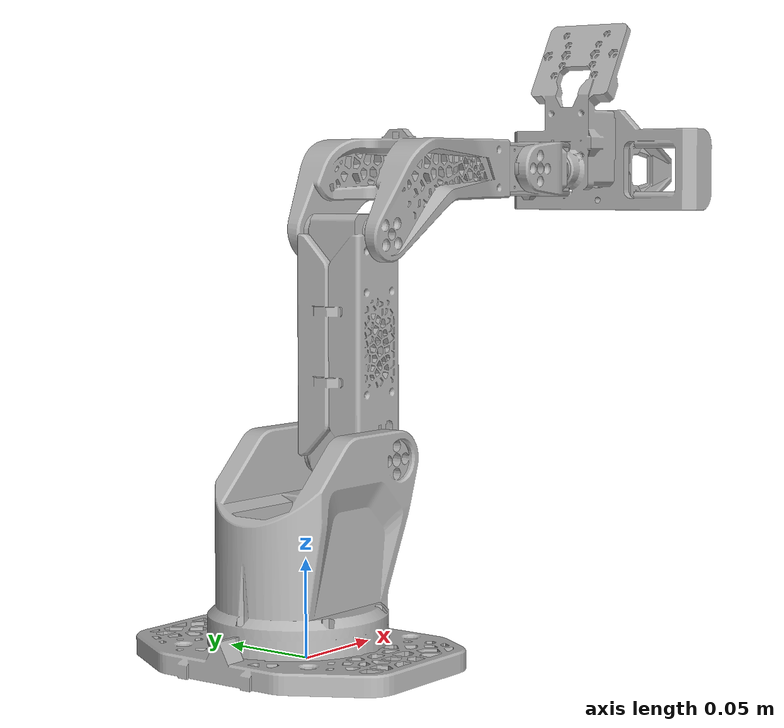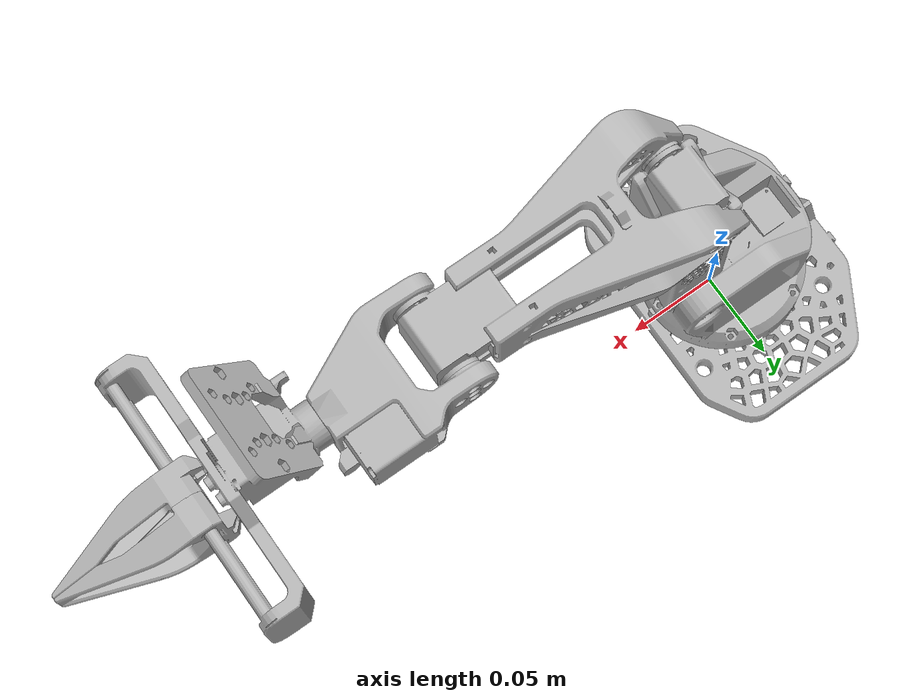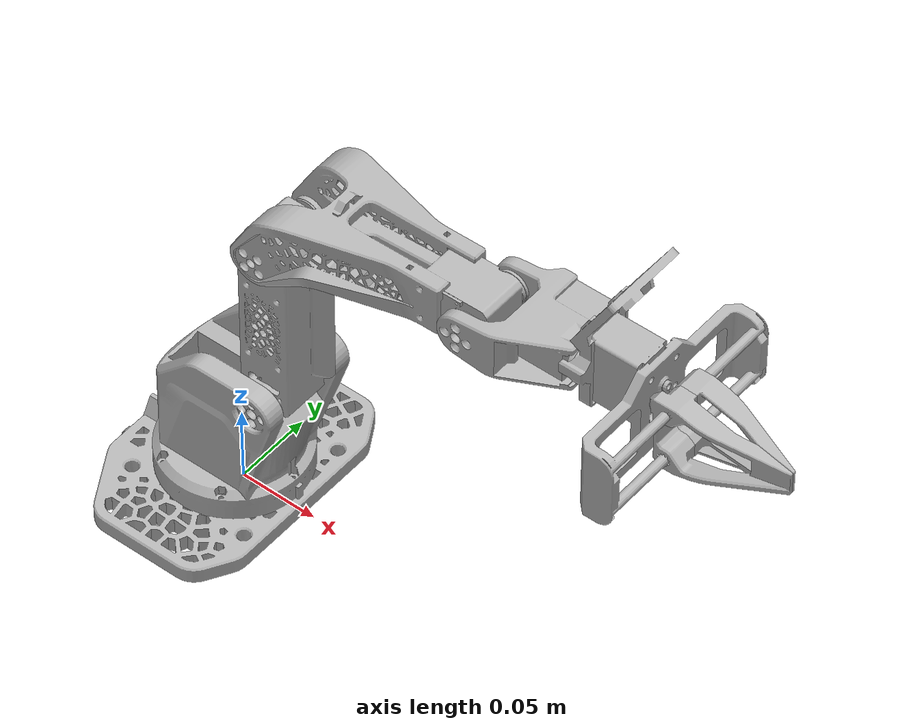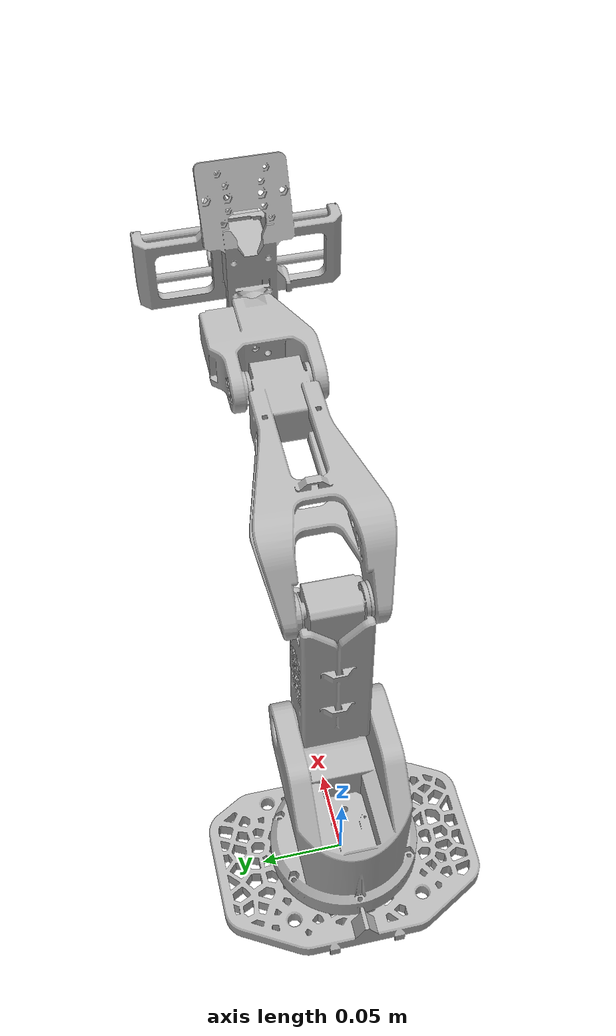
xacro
<?xml version='1.0' encoding='utf-8'?>
<robot xmlns:xacro="http://www.ros.org/wiki/xacro" name="so_arm_102_pre_for_urdf_v5">
  <xacro:include filename="materials.xacro" />
  <link name="base_link">
    <inertial>
      <origin xyz="-0.00753657459228 2.70964811146e-05 0.013641047398" rpy="0 0 0" />
      <mass value="0.178499229726" />
      <inertia ixx="0.000199871543864" iyy="0.000148679123423" izz="0.000331455821027" ixy="1.90199840717e-07" iyz="4.23062670743e-08" ixz="-2.10081183092e-06" />
    </inertial>
    <visual>
      <origin xyz="-0 -0 -0" rpy="0 0 0" />
      <geometry>
        <mesh filename="meshes/base_link.stl" scale="0.001 0.001 0.001" />
      </geometry>
      <material name="silver" />
    </visual>
    <collision>
      <origin xyz="-0.0676210912404 0 0.0041289087596" rpy="0 -0 0" />
      <geometry>
        <box size="0.00185781751921 0.0461 0.00835781751921" />
      </geometry>
    </collision>
    <collision>
      <origin xyz="-0.0658630717683 -7.32747196253e-16 0.005" rpy="0 -0 0" />
      <geometry>
        <box size="0.00185822142507 0.0763103613637 0.0101" />
      </geometry>
    </collision>
    <collision>
      <origin xyz="-0.0632269725968 -6.2172489379e-17 0.005" rpy="0 -0 0" />
      <geometry>
        <box size="0.00361648534738 0.0891942396134 0.0101" />
      </geometry>
    </collision>
    <collision>
      <origin xyz="-0.0579530948847 -6.2172489379e-17 0.005" rpy="0 -0 0" />
      <geometry>
        <box size="0.00713127007684 0.113551273643 0.0101" />
      </geometry>
    </collision>
    <collision>
      <origin xyz="-0.0474059649052 1.12709785505e-09 0.005000005" rpy="0 -0 0" />
      <geometry>
        <box size="0.0141629898823 0.155433757754 0.01010001" />
      </geometry>
    </collision>
    <collision>
      <origin xyz="-0.0263128691418 -1.92392880294e-09 0.005" rpy="0 -0 0" />
      <geometry>
        <box size="0.028226059513 0.160101417302 0.0101" />
      </geometry>
    </collision>
    <collision>
      <origin xyz="-0.0587448469642 1.38777878078e-16 0.015" rpy="0 -0 0" />
      <geometry>
        <box size="0.0146103060715 0.0141470053838 0.0101" />
      </geometry>
    </collision>
    <collision>
      <origin xyz="-0.0347812299232 -2.22044604925e-18 0.0125" rpy="0 -0 0" />
      <geometry>
        <box size="0.00653754015368 0.0385999037196 0.0051" />
      </geometry>
    </collision>
    <collision>
      <origin xyz="-0.0283436897695 -4.4408920985e-18 0.0125" rpy="0 -0 0" />
      <geometry>
        <box size="0.00653754015368 0.0514122771566 0.0051" />
      </geometry>
    </collision>
    <collision>
      <origin xyz="-0.018687379539 -0.020028849057 0.0125" rpy="0 -0 0" />
      <geometry>
        <box size="0.0129750803074 0.022809793716 0.0051" />
      </geometry>
    </collision>
    <collision>
      <origin xyz="-0.018687379539 0.020028849057 0.0125" rpy="0 -0 0" />
      <geometry>
        <box size="0.0129750803074 0.022809793716 0.0051" />
      </geometry>
    </collision>
    <collision>
      <origin xyz="0.0112618316533 -0.0750003552874 0.005" rpy="0 -0 0" />
      <geometry>
        <box size="0.0471233420772 0.0101007105748 0.0101" />
      </geometry>
    </collision>
    <collision>
      <origin xyz="0.0127052073263 -0.0675 0.005" rpy="0 -0 0" />
      <geometry>
        <box size="0.0500100934231 0.0051 0.0101" />
      </geometry>
    </collision>
    <collision>
      <origin xyz="0.0167886061091 -0.0625 0.005" rpy="0 -0 0" />
      <geometry>
        <box size="0.0476167985493 0.0051 0.0101" />
      </geometry>
    </collision>
    <collision>
      <origin xyz="0.0158752409221 -0.0499999869915 0.00500000521433" rpy="0 -0 0" />
      <geometry>
        <box size="0.0563501606147 0.0201000260169 0.0101000104287" />
      </geometry>
    </collision>
    <collision>
      <origin xyz="0.0158750803074 -0.0350000104729 0.0065" rpy="0 -0 0" />
      <geometry>
        <box size="0.0563498393853 0.0101000209459 0.0131" />
      </geometry>
    </collision>
    <collision>
      <origin xyz="0.0158750803074 -0.025 0.0075" rpy="0 -0 0" />
      <geometry>
        <box size="0.0563498393853 0.0101 0.0151" />
      </geometry>
    </collision>
    <collision>
      <origin xyz="0.0222015621187 -0.0175 0.0075" rpy="0 -0 0" />
      <geometry>
        <box size="0.0436968757626 0.0051 0.0151" />
      </geometry>
    </collision>
    <collision>
      <origin xyz="0.0263484692283 -0.0125 0.0075" rpy="0 -0 0" />
      <geometry>
        <box size="0.0354030615433 0.0051 0.0151" />
      </geometry>
    </collision>
    <collision>
      <origin xyz="0.0203496389845 -0.005 0.0075" rpy="0 -0 0" />
      <geometry>
        <box size="0.0158669073437 0.0101 0.0151" />
      </geometry>
    </collision>
    <collision>
      <origin xyz="0.0361165463282 -0.005 0.005" rpy="0 -0 0" />
      <geometry>
        <box size="0.0158669073437 0.0101 0.0101" />
      </geometry>
    </collision>
    <collision>
      <origin xyz="0.0203496389845 0.005 0.0075" rpy="0 -0 0" />
      <geometry>
        <box size="0.0158669073437 0.0101 0.0151" />
      </geometry>
    </collision>
    <collision>
      <origin xyz="0.0361165463282 0.005 0.005" rpy="0 -0 0" />
      <geometry>
        <box size="0.0158669073437 0.0101 0.0101" />
      </geometry>
    </collision>
    <collision>
      <origin xyz="0.0263484692283 0.0125 0.0075" rpy="0 -0 0" />
      <geometry>
        <box size="0.0354030615433 0.0051 0.0151" />
      </geometry>
    </collision>
    <collision>
      <origin xyz="0.0113023431781 0.0175 0.0075" rpy="0 -0 0" />
      <geometry>
        <box size="0.0218984378813 0.0051 0.0151" />
      </geometry>
    </collision>
    <collision>
      <origin xyz="0.0331007810594 0.0175 0.0065" rpy="0 -0 0" />
      <geometry>
        <box size="0.0218984378813 0.0051 0.0131" />
      </geometry>
    </collision>
    <collision>
      <origin xyz="0.0158750803074 0.025 0.0075" rpy="0 -0 0" />
      <geometry>
        <box size="0.0563498393853 0.0101 0.0151" />
      </geometry>
    </collision>
    <collision>
      <origin xyz="0.0158750803074 0.0350000224689 0.0065" rpy="0 -0 0" />
      <geometry>
        <box size="0.0563498393853 0.0101000449378 0.0131" />
      </geometry>
    </collision>
    <collision>
      <origin xyz="0.0158752409221 0.0499999861927 0.00500000521433" rpy="0 -0 0" />
      <geometry>
        <box size="0.0563501606147 0.0201000276145 0.0101000104287" />
      </geometry>
    </collision>
    <collision>
      <origin xyz="0.0141485829993 0.0625 0.005" rpy="0 -0 0" />
      <geometry>
        <box size="0.0528968447691 0.0051 0.0101" />
      </geometry>
    </collision>
    <collision>
      <origin xyz="0.0127052073263 0.0675 0.005" rpy="0 -0 0" />
      <geometry>
        <box size="0.0500100934231 0.0051 0.010100102374" />
      </geometry>
    </collision>
    <collision>
      <origin xyz="0.0112618316533 0.0750003552874 0.005" rpy="0 -0 0" />
      <geometry>
        <box size="0.0471233420772 0.0101007105748 0.0101" />
      </geometry>
    </collision>
    <collision>
      <origin xyz="-0.006 -0.02925 0.013625" rpy="0 -0 0" />
      <geometry>
        <box size="0.0676499814952 0.0196 0.00135" />
      </geometry>
    </collision>
    <collision>
      <origin xyz="-0.006 -0.00975 0.013625" rpy="0 -0 0" />
      <geometry>
        <box size="0.0781 0.0196 0.00135" />
      </geometry>
    </collision>
    <collision>
      <origin xyz="-0.006 0.00975 0.013625" rpy="0 -0 0" />
      <geometry>
        <box size="0.0781 0.0196 0.00135" />
      </geometry>
    </collision>
    <collision>
      <origin xyz="-0.006 0.02925 0.013625" rpy="0 -0 0" />
      <geometry>
        <box size="0.0676499814952 0.0196 0.00135" />
      </geometry>
    </collision>
    <collision>
      <origin xyz="-0.006 -0.02925 0.014875" rpy="0 -0 0" />
      <geometry>
        <box size="0.0676499814952 0.0196 0.00135" />
      </geometry>
    </collision>
    <collision>
      <origin xyz="-0.006 -0.00975 0.014875" rpy="0 -0 0" />
      <geometry>
        <box size="0.0781 0.0196 0.00135" />
      </geometry>
    </collision>
    <collision>
      <origin xyz="-0.006 0.00975 0.014875" rpy="0 -0 0" />
      <geometry>
        <box size="0.0781 0.0196 0.00135" />
      </geometry>
    </collision>
    <collision>
      <origin xyz="-0.006 0.02925 0.014875" rpy="0 -0 0" />
      <geometry>
        <box size="0.0676499814952 0.0196 0.00135" />
      </geometry>
    </collision>
    <collision>
      <origin xyz="-0.03525 -1.11022302463e-16 0.016125" rpy="0 -0 0" />
      <geometry>
        <box size="0.0196 0.0676499814952 0.00135" />
      </geometry>
    </collision>
    <collision>
      <origin xyz="-0.01575 -1.11022302463e-16 0.016125" rpy="0 -0 0" />
      <geometry>
        <box size="0.0196 0.0781 0.00135" />
      </geometry>
    </collision>
    <collision>
      <origin xyz="0.00375 -1.11022302463e-16 0.016125" rpy="0 -0 0" />
      <geometry>
        <box size="0.0196 0.0781 0.00135" />
      </geometry>
    </collision>
    <collision>
      <origin xyz="0.02325 -1.11022302463e-16 0.016125" rpy="0 -0 0" />
      <geometry>
        <box size="0.0196 0.0676499814952 0.00135" />
      </geometry>
    </collision>
    <collision>
      <origin xyz="-0.006 -0.02925 0.017375" rpy="0 -0 0" />
      <geometry>
        <box size="0.0676499814952 0.0196 0.00135" />
      </geometry>
    </collision>
    <collision>
      <origin xyz="-0.006 -0.00975 0.017375" rpy="0 -0 0" />
      <geometry>
        <box size="0.0781 0.0196 0.00135" />
      </geometry>
    </collision>
    <collision>
      <origin xyz="-0.006 0.00975 0.017375" rpy="0 -0 0" />
      <geometry>
        <box size="0.0781 0.0196 0.00135" />
      </geometry>
    </collision>
    <collision>
      <origin xyz="-0.006 0.02925 0.017375" rpy="0 -0 0" />
      <geometry>
        <box size="0.0676499814952 0.0196 0.00135" />
      </geometry>
    </collision>
    <collision>
      <origin xyz="-0.006 -0.02925 0.018625" rpy="0 -0 0" />
      <geometry>
        <box size="0.0676499814952 0.0196 0.00135" />
      </geometry>
    </collision>
    <collision>
      <origin xyz="-0.006 -0.00975 0.018625" rpy="0 -0 0" />
      <geometry>
        <box size="0.0781 0.0196 0.00135" />
      </geometry>
    </collision>
    <collision>
      <origin xyz="-0.006 0.00975 0.018625" rpy="0 -0 0" />
      <geometry>
        <box size="0.0781 0.0196 0.00135" />
      </geometry>
    </collision>
    <collision>
      <origin xyz="-0.006 0.02925 0.018625" rpy="0 -0 0" />
      <geometry>
        <box size="0.0676499814952 0.0196 0.00135" />
      </geometry>
    </collision>
    <collision>
      <origin xyz="-0.006 -0.02925 0.019875" rpy="0 -0 0" />
      <geometry>
        <box size="0.0676499814952 0.0196 0.00135" />
      </geometry>
    </collision>
    <collision>
      <origin xyz="-0.006 -0.00975 0.019875" rpy="0 -0 0" />
      <geometry>
        <box size="0.0781 0.0196 0.00135" />
      </geometry>
    </collision>
    <collision>
      <origin xyz="-0.006 0.00975 0.019875" rpy="0 -0 0" />
      <geometry>
        <box size="0.0781 0.0196 0.00135" />
      </geometry>
    </collision>
    <collision>
      <origin xyz="-0.006 0.02925 0.019875" rpy="0 -0 0" />
      <geometry>
        <box size="0.0676499814952 0.0196 0.00135" />
      </geometry>
    </collision>
    <collision>
      <origin xyz="-0.006 -0.02925 0.021125" rpy="0 -0 0" />
      <geometry>
        <box size="0.0676499814952 0.0196 0.00135" />
      </geometry>
    </collision>
    <collision>
      <origin xyz="-0.006 -0.00975 0.021125" rpy="0 -0 0" />
      <geometry>
        <box size="0.0781 0.0196 0.00135" />
      </geometry>
    </collision>
    <collision>
      <origin xyz="-0.006 0.00975 0.021125" rpy="0 -0 0" />
      <geometry>
        <box size="0.0781 0.0196 0.00135" />
      </geometry>
    </collision>
    <collision>
      <origin xyz="-0.006 0.02925 0.021125" rpy="0 -0 0" />
      <geometry>
        <box size="0.0676499814952 0.0196 0.00135" />
      </geometry>
    </collision>
    <collision>
      <origin xyz="-0.006 -0.02925 0.022375" rpy="0 -0 0" />
      <geometry>
        <box size="0.0676499814952 0.0196 0.00135" />
      </geometry>
    </collision>
    <collision>
      <origin xyz="-0.006 -0.00975 0.022375" rpy="0 -0 0" />
      <geometry>
        <box size="0.0781 0.0196 0.00135" />
      </geometry>
    </collision>
    <collision>
      <origin xyz="-0.006 0.00975 0.022375" rpy="0 -0 0" />
      <geometry>
        <box size="0.0781 0.0196 0.00135" />
      </geometry>
    </collision>
    <collision>
      <origin xyz="-0.006 0.02925 0.022375" rpy="0 -0 0" />
      <geometry>
        <box size="0.0676499814952 0.0196 0.00135" />
      </geometry>
    </collision>
    <collision>
      <origin xyz="-0.006 -0.009375 0.0262" rpy="0 -0 0" />
      <geometry>
        <box size="0.00978245836552 0.00135 0.0025" />
      </geometry>
    </collision>
    <collision>
      <origin xyz="-0.006 -0.008125 0.0262" rpy="0 -0 0" />
      <geometry>
        <box size="0.0133287565553 0.00135 0.0025" />
      </geometry>
    </collision>
    <collision>
      <origin xyz="-0.006 -0.00625 0.0262" rpy="0 -0 0" />
      <geometry>
        <box size="0.0174205080757 0.0026 0.0025" />
      </geometry>
    </collision>
    <collision>
      <origin xyz="-0.006 -0.0025 0.0262" rpy="0 -0 0" />
      <geometry>
        <box size="0.0201 0.0051 0.0025" />
      </geometry>
    </collision>
    <collision>
      <origin xyz="-0.006 0.0025 0.0262" rpy="0 -0 0" />
      <geometry>
        <box size="0.0201 0.0051 0.0025" />
      </geometry>
    </collision>
    <collision>
      <origin xyz="-0.006 0.00625 0.0262" rpy="0 -0 0" />
      <geometry>
        <box size="0.0174205080757 0.0026 0.0025" />
      </geometry>
    </collision>
    <collision>
      <origin xyz="-0.006 0.008125 0.0262" rpy="0 -0 0" />
      <geometry>
        <box size="0.0133287565553 0.00135 0.0025" />
      </geometry>
    </collision>
    <collision>
      <origin xyz="-0.006 0.009375 0.0262" rpy="0 -0 0" />
      <geometry>
        <box size="0.00978245836552 0.00135 0.0025" />
      </geometry>
    </collision>
    <collision>
      <origin xyz="-0.006 -0.0225 0.0158125" rpy="0 -0 0" />
      <geometry>
        <box size="0.0520615242271 0.0151 0.001325" />
      </geometry>
    </collision>
    <collision>
      <origin xyz="-0.006 -0.0075 0.0158125" rpy="0 -0 0" />
      <geometry>
        <box size="0.0601 0.0151 0.001325" />
      </geometry>
    </collision>
    <collision>
      <origin xyz="-0.006 0.0075 0.0158125" rpy="0 -0 0" />
      <geometry>
        <box size="0.0601 0.0151 0.001325" />
      </geometry>
    </collision>
    <collision>
      <origin xyz="-0.006 0.0225 0.0158125" rpy="0 -0 0" />
      <geometry>
        <box size="0.0520615242271 0.0151 0.001325" />
      </geometry>
    </collision>
    <collision>
      <origin xyz="-0.006 -0.0225 0.0170375" rpy="0 -0 0" />
      <geometry>
        <box size="0.0520615242271 0.0151 0.001325" />
      </geometry>
    </collision>
    <collision>
      <origin xyz="-0.006 -0.0075 0.0170375" rpy="0 -0 0" />
      <geometry>
        <box size="0.0601 0.0151 0.001325" />
      </geometry>
    </collision>
    <collision>
      <origin xyz="-0.006 0.0075 0.0170375" rpy="0 -0 0" />
      <geometry>
        <box size="0.0601 0.0151 0.001325" />
      </geometry>
    </collision>
    <collision>
      <origin xyz="-0.006 0.0225 0.0170375" rpy="0 -0 0" />
      <geometry>
        <box size="0.0520615242271 0.0151 0.001325" />
      </geometry>
    </collision>
    <collision>
      <origin xyz="-0.006 -0.0225 0.0182625" rpy="0 -0 0" />
      <geometry>
        <box size="0.0520615242271 0.0151 0.001325" />
      </geometry>
    </collision>
    <collision>
      <origin xyz="-0.006 -0.0075 0.0182625" rpy="0 -0 0" />
      <geometry>
        <box size="0.0601 0.0151 0.001325" />
      </geometry>
    </collision>
    <collision>
      <origin xyz="-0.006 0.0075 0.0182625" rpy="0 -0 0" />
      <geometry>
        <box size="0.0601 0.0151 0.001325" />
      </geometry>
    </collision>
    <collision>
      <origin xyz="-0.006 0.0225 0.0182625" rpy="0 -0 0" />
      <geometry>
        <box size="0.0520615242271 0.0151 0.001325" />
      </geometry>
    </collision>
    <collision>
      <origin xyz="-0.006 -0.0225 0.0194875" rpy="0 -0 0" />
      <geometry>
        <box size="0.0520615242271 0.0151 0.001325" />
      </geometry>
    </collision>
    <collision>
      <origin xyz="-0.006 -0.0075 0.0194875" rpy="0 -0 0" />
      <geometry>
        <box size="0.0601 0.0151 0.001325" />
      </geometry>
    </collision>
    <collision>
      <origin xyz="-0.006 0.0075 0.0194875" rpy="0 -0 0" />
      <geometry>
        <box size="0.0601 0.0151 0.001325" />
      </geometry>
    </collision>
    <collision>
      <origin xyz="-0.006 0.0225 0.0194875" rpy="0 -0 0" />
      <geometry>
        <box size="0.0520615242271 0.0151 0.001325" />
      </geometry>
    </collision>
    <collision>
      <origin xyz="-0.0285 -1.06581410364e-16 0.0207125" rpy="0 -0 0" />
      <geometry>
        <box size="0.0151 0.0520615242271 0.001325" />
      </geometry>
    </collision>
    <collision>
      <origin xyz="-0.0135 -1.11022302463e-16 0.0207125" rpy="0 -0 0" />
      <geometry>
        <box size="0.0151 0.0601 0.001325" />
      </geometry>
    </collision>
    <collision>
      <origin xyz="0.0015 -1.11022302463e-16 0.0207125" rpy="0 -0 0" />
      <geometry>
        <box size="0.0151 0.0601 0.001325" />
      </geometry>
    </collision>
    <collision>
      <origin xyz="0.0165 -1.06581410364e-16 0.0207125" rpy="0 -0 0" />
      <geometry>
        <box size="0.0151 0.0520615242271 0.001325" />
      </geometry>
    </collision>
    <collision>
      <origin xyz="-0.0285 -1.11022302463e-16 0.0219375" rpy="0 -0 0" />
      <geometry>
        <box size="0.0151 0.0520615242271 0.001325" />
      </geometry>
    </collision>
    <collision>
      <origin xyz="-0.0135 -1.11022302463e-16 0.0219375" rpy="0 -0 0" />
      <geometry>
        <box size="0.0151 0.0601 0.001325" />
      </geometry>
    </collision>
    <collision>
      <origin xyz="0.0015 -1.11022302463e-16 0.0219375" rpy="0 -0 0" />
      <geometry>
        <box size="0.0151 0.0601 0.001325" />
      </geometry>
    </collision>
    <collision>
      <origin xyz="0.0165 -1.11022302463e-16 0.0219375" rpy="0 -0 0" />
      <geometry>
        <box size="0.0151 0.0520615242271 0.001325" />
      </geometry>
    </collision>
    <collision>
      <origin xyz="-0.03 -1.11022302463e-16 0.0231625" rpy="0 -0 0" />
      <geometry>
        <box size="0.0161 0.0555256258422 0.001325" />
      </geometry>
    </collision>
    <collision>
      <origin xyz="-0.014 -1.11022302463e-16 0.0231625" rpy="0 -0 0" />
      <geometry>
        <box size="0.0161 0.0641 0.001325" />
      </geometry>
    </collision>
    <collision>
      <origin xyz="0.002 -1.11022302463e-16 0.0231625" rpy="0 -0 0" />
      <geometry>
        <box size="0.0161 0.0641 0.001325" />
      </geometry>
    </collision>
    <collision>
      <origin xyz="0.018 -1.11022302463e-16 0.0231625" rpy="0 -0 0" />
      <geometry>
        <box size="0.0161 0.0555256258422 0.001325" />
      </geometry>
    </collision>
    <collision>
      <origin xyz="-0.006 -0.024 0.0243875" rpy="0 -0 0" />
      <geometry>
        <box size="0.0555256258422 0.0161 0.001325" />
      </geometry>
    </collision>
    <collision>
      <origin xyz="-0.006 -0.008 0.0243875" rpy="0 -0 0" />
      <geometry>
        <box size="0.0641 0.0161 0.001325" />
      </geometry>
    </collision>
    <collision>
      <origin xyz="-0.006 0.008 0.0243875" rpy="0 -0 0" />
      <geometry>
        <box size="0.0641 0.0161 0.001325" />
      </geometry>
    </collision>
    <collision>
      <origin xyz="-0.006 0.024 0.0243875" rpy="0 -0 0" />
      <geometry>
        <box size="0.0555256258422 0.0161 0.001325" />
      </geometry>
    </collision>
  </link>
  <link name="link1_1">
    <inertial>
      <origin xyz="0.000323477926688 -9.49285422888e-06 0.0277445919724" rpy="0 0 0" />
      <mass value="0.201603775922" />
      <inertia ixx="0.000198444068688" iyy="0.000237480937143" izz="0.000210354023061" ixy="7.13434120346e-08" iyz="8.6838415384e-08" ixz="-3.34183738347e-05" />
    </inertial>
    <visual>
      <origin xyz="0.006 1.10978314851e-16 -0.025" rpy="0 0 0" />
      <geometry>
        <mesh filename="meshes/link1_1.stl" scale="0.001 0.001 0.001" />
      </geometry>
      <material name="silver" />
    </visual>
    <collision>
      <origin xyz="-3.46944695195e-18 1.66874823626e-17 0.00121417738974" rpy="5.70868293526e-15 -0 0" />
      <geometry>
        <box size="0.0193 0.0193 0.00252835477948" />
      </geometry>
    </collision>
    <collision>
      <origin xyz="-0.0072 5.09158743046e-18 0.00246753178248" rpy="5.70868293526e-15 -0 0" />
      <geometry>
        <box size="0.0049 0.0167276877527 0.000178354006002" />
      </geometry>
    </collision>
    <collision>
      <origin xyz="-0.0042 -0.00667457863839 0.00246753178248" rpy="5.70868293526e-15 -0 0" />
      <geometry>
        <box size="0.0013 0.00454971909226 0.000178354006002" />
      </geometry>
    </collision>
    <collision>
      <origin xyz="-0.0042 -0.00222485954613 0.00303544347435" rpy="5.70868293526e-15 -0 0" />
      <geometry>
        <box size="0.0013 0.00454971909226 0.00131417738974" />
      </geometry>
    </collision>
    <collision>
      <origin xyz="-0.0042 0.00222485954613 0.00303544347435" rpy="5.70868293526e-15 -0 0" />
      <geometry>
        <box size="0.0013 0.00454971909226 0.00131417738974" />
      </geometry>
    </collision>
    <collision>
      <origin xyz="-0.0042 0.00667457863839 0.00246753178248" rpy="5.70868293526e-15 -0 0" />
      <geometry>
        <box size="0.0013 0.00454971909226 0.000178354006002" />
      </geometry>
    </collision>
    <collision>
      <origin xyz="-0.003 -0.00464758001545 0.00303544347435" rpy="5.70868293526e-15 -0 0" />
      <geometry>
        <box size="0.0013 0.0093951600309 0.00131417738974" />
      </geometry>
    </collision>
    <collision>
      <origin xyz="-0.003 0.00464758001545 0.00303544347435" rpy="5.70868293526e-15 -0 0" />
      <geometry>
        <box size="0.0013 0.0093951600309 0.00131417738974" />
      </geometry>
    </collision>
    <collision>
      <origin xyz="-0.0018 -0.00714352853987 0.00246753178248" rpy="5.70868293526e-15 -0 0" />
      <geometry>
        <box size="0.0013 0.00486235235992 0.000178354006002" />
      </geometry>
    </collision>
    <collision>
      <origin xyz="-0.0018 -0.00238117617996 0.00303544347435" rpy="5.70868293526e-15 -0 0" />
      <geometry>
        <box size="0.0013 0.00486235235992 0.00131417738974" />
      </geometry>
    </collision>
    <collision>
      <origin xyz="-0.0018 0.00238117617996 0.00303544347435" rpy="5.70868293526e-15 -0 0" />
      <geometry>
        <box size="0.0013 0.00486235235992 0.00131417738974" />
      </geometry>
    </collision>
    <collision>
      <origin xyz="-0.0018 0.00714352853987 0.00246753178248" rpy="5.70868293526e-15 -0 0" />
      <geometry>
        <box size="0.0013 0.00486235235992 0.000178354006002" />
      </geometry>
    </collision>
    <collision>
      <origin xyz="-0.0006 -0.0056 0.00303544347435" rpy="5.70868293526e-15 -0 0" />
      <geometry>
        <box size="0.0013 0.0081 0.00131417738974" />
      </geometry>
    </collision>
    <collision>
      <origin xyz="-0.0006 0.0056 0.00303544347435" rpy="5.70868293526e-15 -0 0" />
      <geometry>
        <box size="0.0013 0.0081 0.00131417738974" />
      </geometry>
    </collision>
    <collision>
      <origin xyz="0.0006 -0.0056 0.00303544347435" rpy="5.70868293526e-15 -0 0" />
      <geometry>
        <box size="0.0013 0.0081 0.00131417738974" />
      </geometry>
    </collision>
    <collision>
      <origin xyz="0.0006 0.0056 0.00303544347435" rpy="5.70868293526e-15 -0 0" />
      <geometry>
        <box size="0.0013 0.0081 0.00131417738974" />
      </geometry>
    </collision>
    <collision>
      <origin xyz="0.0018 -0.00476235235992 0.00303544347435" rpy="5.70868293526e-15 -0 0" />
      <geometry>
        <box size="0.0013 0.00962470471983 0.00131417738974" />
      </geometry>
    </collision>
    <collision>
      <origin xyz="0.0018 0.00238117617996 0.00303544347435" rpy="5.70868293526e-15 -0 0" />
      <geometry>
        <box size="0.0013 0.00486235235992 0.00131417738974" />
      </geometry>
    </collision>
    <collision>
      <origin xyz="0.0018 0.00714352853987 0.00246753178248" rpy="5.70868293526e-15 -0 0" />
      <geometry>
        <box size="0.0013 0.00486235235992 0.000178354006002" />
      </geometry>
    </collision>
    <collision>
      <origin xyz="0.003 -0.00464758001545 0.00303544347435" rpy="5.70868293526e-15 -0 0" />
      <geometry>
        <box size="0.0013 0.0093951600309 0.00131417738974" />
      </geometry>
    </collision>
    <collision>
      <origin xyz="0.003 0.00464758001545 0.00303544347435" rpy="5.70868293526e-15 -0 0" />
      <geometry>
        <box size="0.0013 0.0093951600309 0.00131417738974" />
      </geometry>
    </collision>
    <collision>
      <origin xyz="0.0042 -0.00667457863839 0.00246753178248" rpy="5.70868293526e-15 -0 0" />
      <geometry>
        <box size="0.0013 0.00454971909226 0.000178354006002" />
      </geometry>
    </collision>
    <collision>
      <origin xyz="0.0042 -0.00222485954613 0.00303544347435" rpy="5.70868293526e-15 -0 0" />
      <geometry>
        <box size="0.0013 0.00454971909226 0.00131417738974" />
      </geometry>
    </collision>
    <collision>
      <origin xyz="0.0042 0.00222485954613 0.00303544347435" rpy="5.70868293526e-15 -0 0" />
      <geometry>
        <box size="0.0013 0.00454971909226 0.00131417738974" />
      </geometry>
    </collision>
    <collision>
      <origin xyz="0.0042 0.00667457863839 0.00246753178248" rpy="5.70868293526e-15 -0 0" />
      <geometry>
        <box size="0.0013 0.00454971909226 0.000178354006002" />
      </geometry>
    </collision>
    <collision>
      <origin xyz="0.0072 3.98136440583e-18 0.00246753178248" rpy="5.70868293526e-15 -0 0" />
      <geometry>
        <box size="0.0049 0.0167276877527 0.000178354006002" />
      </geometry>
    </collision>
    <collision>
      <origin xyz="-0.003345 4.69321024287e-19 0.00424962086409" rpy="5.70868293526e-15 -0 0" />
      <geometry>
        <box size="0.00233 0.00782494660176 0.00131417738974" />
      </geometry>
    </collision>
    <collision>
      <origin xyz="-0.0016725 4.69321024287e-19 0.00424962086409" rpy="5.70868293526e-15 -0 0" />
      <geometry>
        <box size="0.001215 0.00873675286204 0.00131417738974" />
      </geometry>
    </collision>
    <collision>
      <origin xyz="-0.0005575 4.69321024287e-19 0.00424962086409" rpy="5.70868293526e-15 -0 0" />
      <geometry>
        <box size="0.001215 0.00902 0.00131417738974" />
      </geometry>
    </collision>
    <collision>
      <origin xyz="0.0005575 4.69321024287e-19 0.00424962086409" rpy="5.70868293526e-15 -0 0" />
      <geometry>
        <box size="0.001215 0.00902 0.00131417738974" />
      </geometry>
    </collision>
    <collision>
      <origin xyz="0.0016725 4.69321024287e-19 0.00424962086409" rpy="5.70868293526e-15 -0 0" />
      <geometry>
        <box size="0.001215 0.00873675286204 0.00131417738974" />
      </geometry>
    </collision>
    <collision>
      <origin xyz="0.003345 1.0244325366e-18 0.00424962086409" rpy="5.70868293526e-15 -0 0" />
      <geometry>
        <box size="0.00233 0.00782494660176 0.00131417738974" />
      </geometry>
    </collision>
    <collision>
      <origin xyz="-0.0125027236749 -1.99135759842e-06 0.0203067088317" rpy="-5.46546817338e-08 2.5244947926e-11 0.000461899060241" />
      <geometry>
        <box size="0.0450553799658 0.0251002149497 0.0339999996145" />
      </geometry>
    </collision>
    <collision>
      <origin xyz="-4.7843023189e-09 -0.0421875094831 -0.00339329204796" rpy="5.70868293526e-15 -0 0" />
      <geometry>
        <box size="0.0436710650577 0.00572500126447 0.0046" />
      </geometry>
    </collision>
    <collision>
      <origin xyz="-1.09354414846e-09 -0.0365625082187 -0.00339329204796" rpy="5.70868293526e-15 -0 0" />
      <geometry>
        <box size="0.0596294178804 0.00572500126441 0.0046" />
      </geometry>
    </collision>
    <collision>
      <origin xyz="-0.0282462321142 -0.0292905022922 -0.00339329204782" rpy="2.50576788616e-11 2.01661891493e-11 -0.677655336093" />
      <geometry>
        <box size="0.0253252406119 0.0089523934499 0.0046" />
      </geometry>
    </collision>
    <collision>
      <origin xyz="0.0282462295672 -0.0292905004888 -0.00339329204803" rpy="-1.50925171499e-11 1.21463187623e-11 0.67765533499" />
      <geometry>
        <box size="0.0253252389147 0.00895238745894 0.00460000000002" />
      </geometry>
    </collision>
    <collision>
      <origin xyz="-0.0384268717835 -0.0116253593942 -0.00339329204799" rpy="8.07486642643e-11 -2.71884577573e-11 0.324781742519" />
      <geometry>
        <box size="0.00984481244392 0.0263301835717 0.00459999999808" />
      </geometry>
    </collision>
    <collision>
      <origin xyz="0.0384268706901 -0.0116253593942 -0.00339329204766" rpy="2.56197484932e-11 8.62629067786e-12 -0.324781742576" />
      <geometry>
        <box size="0.00984481037093 0.0263301828742 0.0046" />
      </geometry>
    </collision>
    <collision>
      <origin xyz="-0.0384268717845 0.0116253593954 -0.00339329204818" rpy="-5.57615943303e-10 -1.87751929613e-10 -0.324781742719" />
      <geometry>
        <box size="0.00984481244233 0.0263301835722 0.00459999998676" />
      </geometry>
    </collision>
    <collision>
      <origin xyz="0.0384268706893 0.0116253593938 -0.00339329204803" rpy="6.07764116138e-12 -2.0463705679e-12 0.32478174246" />
      <geometry>
        <box size="0.00984481037227 0.0263301828735 0.0046" />
      </geometry>
    </collision>
    <collision>
      <origin xyz="-0.0282462343542 0.0292905004894 -0.003393292048" rpy="-3.31319164132e-11 2.66642611661e-11 0.677655336178" />
      <geometry>
        <box size="0.0253252463619 0.00895239344976 0.00459999999954" />
      </geometry>
    </collision>
    <collision>
      <origin xyz="0.028246225879 0.0292905004891 -0.00339329204788" rpy="-1.32667758592e-11 -1.06769790169e-11 -0.677655336163" />
      <geometry>
        <box size="0.0253252331573 0.00895238282365 0.0046" />
      </geometry>
    </collision>
    <collision>
      <origin xyz="-4.78427443495e-09 0.0365625082187 -0.00339329204796" rpy="5.70868293526e-15 -0 0" />
      <geometry>
        <box size="0.0596294104989 0.00572500126441 0.0046" />
      </geometry>
    </collision>
    <collision>
      <origin xyz="-4.78420647976e-09 0.0421875094831 -0.00339329204796" rpy="5.70868293526e-15 -0 0" />
      <geometry>
        <box size="0.0436710798205 0.00572500126441 0.0046" />
      </geometry>
    </collision>
    <collision>
      <origin xyz="-8.88324367451e-09 -0.0393750088509 -0.000580792047959" rpy="5.70868293526e-15 -0 0" />
      <geometry>
        <box size="0.0596294170637 0.0113500025288 0.001225" />
      </geometry>
    </collision>
    <collision>
      <origin xyz="-9.29532145959e-09 -0.028125006322 -0.000580792047959" rpy="5.70868293526e-15 -0 0" />
      <geometry>
        <box size="0.0780423038613 0.0113500025288 0.001225" />
      </geometry>
    </collision>
    <collision>
      <origin xyz="-0.038426875475 -0.0116253593942 -0.000580792047958" rpy="-8.44587072104e-14 2.84376467747e-14 0.324781742342" />
      <geometry>
        <box size="0.0098448194372 0.0263301859259 0.001225" />
      </geometry>
    </collision>
    <collision>
      <origin xyz="0.0384268670023 -0.0116253593958 -0.000580792029175" rpy="1.63703493053e-09 5.51197416544e-10 -0.324781743036" />
      <geometry>
        <box size="0.00984480337053 0.0263301805205 0.001225" />
      </geometry>
    </collision>
    <collision>
      <origin xyz="-0.0384268758839 0.011625359394 -0.000580792047837" rpy="-1.06223719226e-11 -3.57660294344e-12 -0.324781742504" />
      <geometry>
        <box size="0.00984482021726 0.0263301861888 0.001225" />
      </geometry>
    </collision>
    <collision>
      <origin xyz="0.0384268669991 0.0116253593941 -0.000580792047963" rpy="-1.00093897742e-11 3.3702089509e-12 0.324781742547" />
      <geometry>
        <box size="0.00984480337586 0.0263301805187 0.00122499999976" />
      </geometry>
    </collision>
    <collision>
      <origin xyz="-9.29513835259e-09 0.0281250063221 -0.000580792047958" rpy="5.70868293526e-15 -0 0" />
      <geometry>
        <box size="0.0780423038617 0.0113500025288 0.001225" />
      </geometry>
    </collision>
    <collision>
      <origin xyz="-8.88681288107e-09 0.0393750088509 -0.000580792047958" rpy="5.70868293526e-15 -0 0" />
      <geometry>
        <box size="0.059629418704 0.0113500025288 0.001225" />
      </geometry>
    </collision>
    <collision>
      <origin xyz="1.11022302463e-16 -0.0388131327719 0.000544207952041" rpy="5.70868293526e-15 -0 0" />
      <geometry>
        <box size="0.0587799410959 0.0111894665063 0.001225" />
      </geometry>
    </collision>
    <collision>
      <origin xyz="1.120891574e-14 -0.0277236662657 0.000544207952041" rpy="5.70868293526e-15 -0 0" />
      <geometry>
        <box size="0.0769300776707 0.0111894665063 0.001225" />
      </geometry>
    </collision>
    <collision>
      <origin xyz="9.85409670529e-15 -0.0166341997594 0.000544207952041" rpy="5.70868293526e-15 -0 0" />
      <geometry>
        <box size="0.0859986381942 0.0111894665063 0.001225" />
      </geometry>
    </collision>
    <collision>
      <origin xyz="1.552577511e-16 -0.00554473325313 0.000544207952041" rpy="5.70868293526e-15 -0 0" />
      <geometry>
        <box size="0.0887397013007 0.0111894665063 0.001225" />
      </geometry>
    </collision>
    <collision>
      <origin xyz="1.552577511e-16 0.00554473325313 0.000544207952041" rpy="5.70868293526e-15 -0 0" />
      <geometry>
        <box size="0.0887397013007 0.0111894665063 0.001225" />
      </geometry>
    </collision>
    <collision>
      <origin xyz="7.74900976719e-15 0.0166341997594 0.000544207952041" rpy="5.70868293526e-15 -0 0" />
      <geometry>
        <box size="0.0859986381942 0.0111894665063 0.001225" />
      </geometry>
    </collision>
    <collision>
      <origin xyz="6.49220260884e-15 0.0277236662657 0.000544207952042" rpy="5.70868293526e-15 -0 0" />
      <geometry>
        <box size="0.0769300776707 0.0111894665063 0.001225" />
      </geometry>
    </collision>
    <collision>
      <origin xyz="1.11022302463e-16 0.0388131327719 0.000544207952042" rpy="5.70868293526e-15 -0 0" />
      <geometry>
        <box size="0.0587799410959 0.0111894665063 0.001225" />
      </geometry>
    </collision>
    <collision>
      <origin xyz="1.02348685083e-16 2.03937994368e-16 0.00166920795204" rpy="5.70868293526e-15 -0 0" />
      <geometry>
        <box size="0.0863564585354 0.0865040497403 0.001225" />
      </geometry>
    </collision>
    <collision>
      <origin xyz="-0.0314420252929 2.55247323346e-16 0.00279420795204" rpy="5.70868293526e-15 -0 0" />
      <geometry>
        <box size="0.0210613501953 0.0694921916361 0.001225" />
      </geometry>
    </collision>
    <collision>
      <origin xyz="-0.0104806750976 1.97515726065e-16 0.00279420795204" rpy="5.70868293526e-15 -0 0" />
      <geometry>
        <box size="0.0210613501953 0.0841923674305 0.001225" />
      </geometry>
    </collision>
    <collision>
      <origin xyz="0.0209613501953 1.97515726065e-16 0.00279420795204" rpy="5.70868293526e-15 -0 0" />
      <geometry>
        <box size="0.0420227003906 0.0841923674305 0.001225" />
      </geometry>
    </collision>
    <collision>
      <origin xyz="1.34488804272e-05 -1.2565672457e-15 0.00468484328064" rpy="5.70868293526e-15 -0 0" />
      <geometry>
        <box size="0.0816449842537 0.0602846880261 0.00275664067705" />
      </geometry>
    </collision>
    <collision>
      <origin xyz="8.99543593689e-05 -7.43124836414e-15 0.0073411088304" rpy="5.70868293526e-15 -0 0" />
      <geometry>
        <box size="0.0818380927621 0.0607854814961 0.0027566057271" />
      </geometry>
    </collision>
    <collision>
      <origin xyz="0.000303555537538 1.29749747465e-16 0.00999737974449" rpy="5.70868293526e-15 -0 0" />
      <geometry>
        <box size="0.0823021868399 0.0612862749661 0.00275641920737" />
      </geometry>
    </collision>
    <collision>
      <origin xyz="0.000490855855291 1.1393597053e-16 0.0119895879238" rpy="5.70868293526e-15 -0 0" />
      <geometry>
        <box size="0.0826940212634 0.061536671701 0.00142817125435" />
      </geometry>
    </collision>
    <collision>
      <origin xyz="0.000615302890685 1.0191312877e-16 0.0133177313411" rpy="5.70868293526e-15 -0 0" />
      <geometry>
        <box size="0.0829593358045 0.061787068436 0.00142818870434" />
      </geometry>
    </collision>
    <collision>
      <origin xyz="0.000739953501354 9.43312591353e-17 0.0146458607399" rpy="5.70868293526e-15 -0 0" />
      <geometry>
        <box size="0.0832242402284 0.062037465171 0.00142821053303" />
      </geometry>
    </collision>
    <collision>
      <origin xyz="0.000864808767406 8.67493486446e-17 0.0159739972955" rpy="5.70868293526e-15 -0 0" />
      <geometry>
        <box size="0.0834887327468 0.062287861906 0.00142822295489" />
      </geometry>
    </collision>
    <collision>
      <origin xyz="0.00111513758813 7.5376485902e-17 0.0179662016045" rpy="5.70868293526e-15 -0 0" />
      <geometry>
        <box size="0.0840164749225 0.062788655376 0.00275638702098" />
      </geometry>
    </collision>
    <collision>
      <origin xyz="0.00136629800105 6.02126959663e-17 0.0206224692774" rpy="5.70868293526e-15 -0 0" />
      <geometry>
        <box size="0.084542548057 0.063289448846 0.00275640118928" />
      </geometry>
    </collision>
    <collision>
      <origin xyz="0.00161829916858 4.06080441037e-17 0.0232787316651" rpy="5.70868293526e-15 -0 0" />
      <geometry>
        <box size="0.0850669368733 0.0637902423159 0.00275639284759" />
      </geometry>
    </collision>
    <collision>
      <origin xyz="0.00187115135672 2.54442369135e-17 0.0259350023604" rpy="5.70868293526e-15 -0 0" />
      <geometry>
        <box size="0.0855896239204 0.0642910357859 0.0027563754711" />
      </geometry>
    </collision>
    <collision>
      <origin xyz="0.0019978995511 9.63043630304e-18 0.027927214687" rpy="5.70868293526e-15 -0 0" />
      <geometry>
        <box size="0.0858503243164 0.0645414325209 0.00142822360847" />
      </geometry>
    </collision>
    <collision>
      <origin xyz="0.00211990907977 -2.39233550479e-18 0.0292553458506" rpy="5.70868293526e-15 -0 0" />
      <geometry>
        <box size="0.0861205032802 0.0647918292559 0.00142824042891" />
      </geometry>
    </collision>
    <collision>
      <origin xyz="0.0022484589953 -9.97423182402e-18 0.0305834799237" rpy="5.70868293526e-15 -0 0" />
      <geometry>
        <box size="0.0863776031113 0.0650422259951 0.00142823367964" />
      </geometry>
    </collision>
    <collision>
      <origin xyz="0.00237700941298 -2.64379119281e-17 0.0319116139247" rpy="5.70868293526e-15 -0 0" />
      <geometry>
        <box size="0.0866347039466 0.0652926227258 0.00142822106705" />
      </geometry>
    </collision>
    <collision>
      <origin xyz="0.00250556035798 -3.40198223295e-17 0.0332397504647" rpy="5.70868293526e-15 -0 0" />
      <geometry>
        <box size="0.0868918058366 0.0655430193032 0.00142819770841" />
      </geometry>
    </collision>
    <collision>
      <origin xyz="0.00263411216952 -4.60426383884e-17 0.0345678893798" rpy="5.70868293526e-15 -0 0" />
      <geometry>
        <box size="0.0871489094597 0.0657934161958 0.00142821548593" />
      </geometry>
    </collision>
    <collision>
      <origin xyz="0.00276266470905 -5.36245516549e-17 0.0358960264216" rpy="5.70868293526e-15 -0 0" />
      <geometry>
        <box size="0.0874060145388 0.0660438129308 0.00142823039478" />
      </geometry>
    </collision>
    <collision>
      <origin xyz="0.0028912181546 -7.00882173538e-17 0.0372241578992" rpy="5.70868293526e-15 -0 0" />
      <geometry>
        <box size="0.0876631214299 0.0662942096658 0.00142823433844" />
      </geometry>
    </collision>
    <collision>
      <origin xyz="0.00314832817365 -9.47838506005e-17 0.039216378711" rpy="5.70868293526e-15 -0 0" />
      <geometry>
        <box size="0.088177341468 0.0667950031358 0.00275662436402" />
      </geometry>
    </collision>
    <collision>
      <origin xyz="0.00330537095678 -3.71621484043e-10 0.041872844205" rpy="-2.79851460568e-07 -3.97492739944e-06 1.11238923838e-12" />
      <geometry>
        <box size="0.0884914375937 0.0672957966057 0.00275704294031" />
      </geometry>
    </collision>
    <collision>
      <origin xyz="0.00304352026946 4.00159140492e-13 0.0445286105842" rpy="5.70868293526e-15 -0 0" />
      <geometry>
        <box size="0.0879677256596 0.0677857524983 0.00275685578514" />
      </geometry>
    </collision>
    <collision>
      <origin xyz="0.00340445094301 -8.15057299391e-13 0.0471854303943" rpy="5.70868293526e-15 -0 0" />
      <geometry>
        <box size="0.0886907187983 0.0680659577466 0.00275678383499" />
      </geometry>
    </collision>
    <collision>
      <origin xyz="0.00435971572997 -1.01565670274e-08 0.0498413822266" rpy="5.70868293526e-15 -0 0" />
      <geometry>
        <box size="0.0885063116864 0.0681007665228 0.00275663650241" />
      </geometry>
    </collision>
    <collision>
      <origin xyz="0.00611936102315 -1.48397641058e-16 0.0524975946779" rpy="5.70868293526e-15 -0 0" />
      <geometry>
        <box size="0.086713143562 0.0681 0.00275653867696" />
      </geometry>
    </collision>
    <collision>
      <origin xyz="0.00766324072823 -1.59770205139e-16 0.0544897466699" rpy="5.70868293526e-15 -0 0" />
      <geometry>
        <box size="0.0844884442634 0.0681 0.00142851550615" />
      </geometry>
    </collision>
    <collision>
      <origin xyz="0.0085430627932 -1.67352159442e-16 0.0558178909002" rpy="5.70868293526e-15 -0 0" />
      <geometry>
        <box size="0.0835918624839 0.0681 0.00142843305027" />
      </geometry>
    </collision>
    <collision>
      <origin xyz="0.0109332434552 -0.0260000053182 0.0617940872913" rpy="5.70868293526e-15 -0 0" />
      <geometry>
        <box size="0.0857159910077 0.0161000106365 0.0107255718463" />
      </geometry>
    </collision>
    <collision>
      <origin xyz="0.0109332434375 0.0266000050004 0.0617944014479" rpy="5.70868293526e-15 -0 0" />
      <geometry>
        <box size="0.0857159910432 0.0149000100007 0.0107249435331" />
      </geometry>
    </collision>
    <collision>
      <origin xyz="-0.00218737605321 -0.0275 0.0777318683172" rpy="5.70868293526e-15 -0 0" />
      <geometry>
        <box size="0.0382249173688 0.0131 0.0213499902055" />
      </geometry>
    </collision>
    <collision>
      <origin xyz="0.0359380060816 -0.026 0.0777322553498" rpy="5.70868293526e-15 -0 0" />
      <geometry>
        <box size="0.0382258469009 0.0161 0.0213507642707" />
      </geometry>
    </collision>
    <collision>
      <origin xyz="0.0168755469522 0.0266 0.0777322553498" rpy="5.70868293526e-15 -0 0" />
      <geometry>
        <box size="0.0763507651598 0.0149 0.0213507642707" />
      </geometry>
    </collision>
    <collision>
      <origin xyz="-0.0354437892756 -0.0228806130634 -0.0106434239281" rpy="-8.8967454679e-07 -1.378124498e-06 0.573237978827" />
      <geometry>
        <box size="0.00572500000016 0.0436710626455 0.0101000000018" />
      </geometry>
    </collision>
    <collision>
      <origin xyz="-0.0324901395769 -0.0209738953081 -0.0106434190837" rpy="-8.8967454679e-07 -1.378124498e-06 0.573237978827" />
      <geometry>
        <box size="0.00150625 0.0484062738556 0.0101000000003" />
      </geometry>
    </collision>
    <collision>
      <origin xyz="-0.0313086796974 -0.020211208206 -0.0106434171445" rpy="-8.8967454679e-07 -1.378124498e-06 0.573237978827" />
      <geometry>
        <box size="0.00150625 0.0525665071743 0.0100999999994" />
      </geometry>
    </collision>
    <collision>
      <origin xyz="-0.019605401496 -0.0344511829337 -0.0106433979481" rpy="-8.8967454679e-07 -1.378124498e-06 0.573237978827" />
      <geometry>
        <box size="0.0029125 0.0230073271135 0.0100999999999" />
      </geometry>
    </collision>
    <collision>
      <origin xyz="-0.0394675782605 -0.00368317217173 -0.0106434305283" rpy="-8.8967454679e-07 -1.378124498e-06 0.573237978827" />
      <geometry>
        <box size="0.0029125 0.0230073271132 0.0100999999995" />
      </geometry>
    </collision>
    <collision>
      <origin xyz="-0.0122234778194 -0.0381077669533 -0.0106433858398" rpy="-8.8967454679e-07 -1.378124498e-06 0.573237978827" />
      <geometry>
        <box size="0.005725 0.0195827470147 0.0101000000003" />
      </geometry>
    </collision>
    <collision>
      <origin xyz="-0.00409553920358 -0.0403271267965 -0.010643372507" rpy="-8.8967454679e-07 -1.378124498e-06 0.573237978827" />
      <geometry>
        <box size="0.005725 0.0147231581409 0.0100999999996" />
      </geometry>
    </collision>
    <collision>
      <origin xyz="-0.0402778670221 0.00275774150563 -0.0106434318574" rpy="-8.8967454679e-07 -1.378124498e-06 0.573237978827" />
      <geometry>
        <box size="0.0029125 0.0171329302571 0.0101000000005" />
      </geometry>
    </collision>
    <collision>
      <origin xyz="-0.0399383220014 0.00741747587897 -0.0106434313005" rpy="-8.8967454679e-07 -1.378124498e-06 0.573237978827" />
      <geometry>
        <box size="0.0029125 0.0145711271806 0.0100999999996" />
      </geometry>
    </collision>
    <collision>
      <origin xyz="-0.0384370022405 0.0128703911205 -0.0106434288379" rpy="-8.8967454679e-07 -1.378124498e-06 0.573237978827" />
      <geometry>
        <box size="0.005725 0.0147231581406 0.0100999999997" />
      </geometry>
    </collision>
    <collision>
      <origin xyz="0.00280545243145 -0.0406458531714 -0.0106433611875" rpy="-8.8967454679e-07 -1.378124498e-06 0.573237978827" />
      <geometry>
        <box size="0.005725 0.0121919709328 0.0101000000003" />
      </geometry>
    </collision>
    <collision>
      <origin xyz="0.00899106590842 -0.0398564047915 -0.0106433510409" rpy="-8.8967454679e-07 -1.378124498e-06 0.573237978827" />
      <geometry>
        <box size="0.005725 0.0105187720003 0.0100999999997" />
      </geometry>
    </collision>
    <collision>
      <origin xyz="0.0172005526486 -0.0370911225736 -0.0106433374875" rpy="-6.40317158255e-07 -1.49368944106e-06 0.419623061897" />
      <geometry>
        <box size="0.0126775433926 0.00833805168691 0.0101" />
      </geometry>
    </collision>
    <collision>
      <origin xyz="-0.0358863148399 0.0192906143124 -0.010643424654" rpy="-8.8967454679e-07 -1.378124498e-06 0.573237978827" />
      <geometry>
        <box size="0.005725 0.0121919709326 0.0101000000003" />
      </geometry>
    </collision>
    <collision>
      <origin xyz="-0.0326202492812 0.0246026627494 -0.0106434192966" rpy="-8.8967454679e-07 -1.378124498e-06 0.573237978827" />
      <geometry>
        <box size="0.005725 0.010518772 0.0100999999997" />
      </geometry>
    </collision>
    <collision>
      <origin xyz="-0.0267203376356 0.0309456510819 -0.0106434096181" rpy="-1.09027218454e-06 -1.22573408033e-06 0.726852899494" />
      <geometry>
        <box size="0.0126775434561 0.00833805188943 0.0101" />
      </geometry>
    </collision>
    <collision>
      <origin xyz="0.0267203518522 -0.0309456510814 -0.0106433219595" rpy="-1.09012984152e-06 -1.2257561197e-06 0.726852899799" />
      <geometry>
        <box size="0.0126775434584 0.00833805188858 0.0101000000006" />
      </geometry>
    </collision>
    <collision>
      <origin xyz="0.0326202634973 -0.0246026627489 -0.0106433122817" rpy="-8.8967454679e-07 -1.378124498e-06 0.573237978827" />
      <geometry>
        <box size="0.00572499999998 0.010518772 0.0101000000003" />
      </geometry>
    </collision>
    <collision>
      <origin xyz="0.0358863290559 -0.0192906143119 -0.0106433069243" rpy="-8.8967454679e-07 -1.378124498e-06 0.573237978827" />
      <geometry>
        <box size="0.00572499999998 0.0121919709326 0.0100999999997" />
      </geometry>
    </collision>
    <collision>
      <origin xyz="-0.0172005384522 0.0370911226106 -0.0106433940036" rpy="-6.6832923978e-07 -1.49802668816e-06 0.419623057848" />
      <geometry>
        <box size="0.0126775434584 0.00833805188739 0.0101000000003" />
      </geometry>
    </collision>
    <collision>
      <origin xyz="-0.00899105169197 0.0398564047915 -0.0106433805374" rpy="-8.8967454679e-07 -1.378124498e-06 0.573237978827" />
      <geometry>
        <box size="0.00572499999998 0.0105187719997 0.0101000000003" />
      </geometry>
    </collision>
    <collision>
      <origin xyz="-0.00280543821501 0.0406458531714 -0.0106433703908" rpy="-8.8967454679e-07 -1.378124498e-06 0.573237978827" />
      <geometry>
        <box size="0.00572499999998 0.0121919709324 0.0100999999997" />
      </geometry>
    </collision>
    <collision>
      <origin xyz="0.0384370164565 -0.01287039112 -0.0106433027404" rpy="-8.8967454679e-07 -1.378124498e-06 0.573237978827" />
      <geometry>
        <box size="0.00572499999998 0.0147231581408 0.0101000000003" />
      </geometry>
    </collision>
    <collision>
      <origin xyz="0.0399383362174 -0.00741747587838 -0.0106433002778" rpy="-8.8967454679e-07 -1.378124498e-06 0.573237978827" />
      <geometry>
        <box size="0.00291249999999 0.0145711271808 0.0101000000004" />
      </geometry>
    </collision>
    <collision>
      <origin xyz="0.040277881238 -0.00275774150499 -0.0106432997209" rpy="-8.8967454679e-07 -1.378124498e-06 0.573237978827" />
      <geometry>
        <box size="0.00291249999999 0.0171329302574 0.0100999999995" />
      </geometry>
    </collision>
    <collision>
      <origin xyz="0.00409555342002 0.0403271267964 -0.0106433590713" rpy="-8.8967454679e-07 -1.378124498e-06 0.573237978827" />
      <geometry>
        <box size="0.00572499999998 0.0147231581405 0.0101000000004" />
      </geometry>
    </collision>
    <collision>
      <origin xyz="0.0122234920359 0.0381077669532 -0.0106433457385" rpy="-8.8967454679e-07 -1.378124498e-06 0.573237978827" />
      <geometry>
        <box size="0.00572499999998 0.0195827470145 0.0100999999997" />
      </geometry>
    </collision>
    <collision>
      <origin xyz="0.0394675924763 0.00368317217262 -0.0106433010499" rpy="-8.8967454679e-07 -1.378124498e-06 0.573237978827" />
      <geometry>
        <box size="0.00291249999999 0.023007327114 0.0101000000002" />
      </geometry>
    </collision>
    <collision>
      <origin xyz="0.0196054157125 0.0344511829335 -0.0106433336302" rpy="-8.8967454679e-07 -1.378124498e-06 0.573237978827" />
      <geometry>
        <box size="0.00291249999999 0.0230073271137 0.0101000000002" />
      </geometry>
    </collision>
    <collision>
      <origin xyz="0.0321095963217 0.0202669787424 -0.0106433131204" rpy="-8.8967454679e-07 -1.378124498e-06 0.573237978827" />
      <geometry>
        <box size="0.00291249999999 0.053341543313 0.0101" />
      </geometry>
    </collision>
    <collision>
      <origin xyz="0.0353141564101 0.0204885885596 -0.0106433078638" rpy="-8.8967454679e-07 -1.378124498e-06 0.573237978827" />
      <geometry>
        <box size="0.00291249999999 0.0475497482627 0.0100999999999" />
      </geometry>
    </collision>
    <collision>
      <origin xyz="0.0366252633711 0.0236433001658 -0.0106433057122" rpy="-8.8967454679e-07 -1.378124498e-06 0.573237978827" />
      <geometry>
        <box size="0.00291249999999 0.0314186745409 0.0100999999987" />
      </geometry>
    </collision>
  </link>
  <link name="link2_1">
    <inertial>
      <origin xyz="-9.08588393138e-05 0.0179996080154 0.0565027997369" rpy="0 0 0" />
      <mass value="0.180993297738" />
      <inertia ixx="0.000343822377525" iyy="0.000338733474867" izz="3.40211492897e-05" ixy="3.26214111802e-10" iyz="1.62595657322e-06" ixz="-8.83251140382e-08" />
    </inertial>
    <visual>
      <origin xyz="-0.034 0.018 -0.098356707952" rpy="0 0 0" />
      <geometry>
        <mesh filename="meshes/link2_1.stl" scale="0.001 0.001 0.001" />
      </geometry>
      <material name="silver" />
    </visual>
    <collision>
      <origin xyz="0.00849996553692 0.0188250392342 0.0565017116361" rpy="2.25149391728e-14 -1.57079632679 0" />
      <geometry>
        <box size="0.0854619619715 0.00135090398396 0.0171" />
      </geometry>
    </collision>
    <collision>
      <origin xyz="-0.00850003446307 0.0188250467442 0.0565017116361" rpy="2.25149391728e-14 -1.57079632679 0" />
      <geometry>
        <box size="0.0854619619715 0.00135088896396 0.0171" />
      </geometry>
    </collision>
    <collision>
      <origin xyz="-3.44630759277e-08 0.020075374606 0.0345014318656" rpy="2.25149391728e-14 -1.57079632679 0" />
      <geometry>
        <box size="0.044100559541 0.00135036987014 0.0341" />
      </geometry>
    </collision>
    <collision>
      <origin xyz="-3.44630759277e-08 0.020075374606 0.0785019914066" rpy="2.25149391728e-14 -1.57079632679 0" />
      <geometry>
        <box size="0.044100559541 0.00135036987014 0.0341" />
      </geometry>
    </collision>
    <collision>
      <origin xyz="-3.44630759624e-08 0.0213257381618 0.0338762532449" rpy="2.25149391728e-14 -1.57079632679 0" />
      <geometry>
        <box size="0.0453509167825 0.00135035724148 0.0341" />
      </geometry>
    </collision>
    <collision>
      <origin xyz="-3.44630759624e-08 0.0213257381618 0.0791271700274" rpy="2.25149391728e-14 -1.57079632679 0" />
      <geometry>
        <box size="0.0453509167825 0.00135035724148 0.0341" />
      </geometry>
    </collision>
    <collision>
      <origin xyz="-3.44630760041e-08 0.0225760954032 0.0332510746241" rpy="2.25149391728e-14 -1.57079632679 0" />
      <geometry>
        <box size="0.046601274024 0.00135035724148 0.0341" />
      </geometry>
    </collision>
    <collision>
      <origin xyz="-3.44630759833e-08 0.0225760954033 0.0797523486481" rpy="2.25149391728e-14 -1.57079632679 0" />
      <geometry>
        <box size="0.046601274024 0.00135035724148 0.0341" />
      </geometry>
    </collision>
    <collision>
      <origin xyz="-3.4463076018e-08 0.0238264526447 0.0326258960034" rpy="2.25149391728e-14 -1.57079632679 0" />
      <geometry>
        <box size="0.0478516312655 0.00135035724148 0.0341" />
      </geometry>
    </collision>
    <collision>
      <origin xyz="-3.4463076018e-08 0.0238264657876 0.0803775272688" rpy="2.25149391728e-14 -1.57079632679 0" />
      <geometry>
        <box size="0.0478516312655 0.0013503835272 0.0341" />
      </geometry>
    </collision>
    <collision>
      <origin xyz="-3.44630760526e-08 0.0250768098862 0.0320007173826" rpy="2.25149391728e-14 -1.57079632679 0" />
      <geometry>
        <box size="0.0491019885069 0.00135035724148 0.0341" />
      </geometry>
    </collision>
    <collision>
      <origin xyz="-3.44630760526e-08 0.0250767890119 0.0810027058896" rpy="2.25149391728e-14 -1.57079632679 0" />
      <geometry>
        <box size="0.0491019885069 0.00135039899003 0.0341" />
      </geometry>
    </collision>
    <collision>
      <origin xyz="0.00849996553692 0.0263271671277 0.0565017116361" rpy="2.25149391728e-14 -1.57079632679 0" />
      <geometry>
        <box size="0.100604691497 0.00135035724148 0.0171" />
      </geometry>
    </collision>
    <collision>
      <origin xyz="-0.00850003446307 0.0263271671277 0.0565017116361" rpy="2.25149391728e-14 -1.57079632679 0" />
      <geometry>
        <box size="0.100604691497 0.00135035724148 0.0171" />
      </geometry>
    </collision>
    <collision>
      <origin xyz="-3.44630761082e-08 0.0275775243692 0.0307503601412" rpy="2.25149391728e-14 -1.57079632679 0" />
      <geometry>
        <box size="0.0516027029899 0.00135035724148 0.0341" />
      </geometry>
    </collision>
    <collision>
      <origin xyz="-3.44630761082e-08 0.0275775243692 0.0822530631311" rpy="2.25149391728e-14 -1.57079632679 0" />
      <geometry>
        <box size="0.0516027029899 0.00135035724148 0.0341" />
      </geometry>
    </collision>
    <collision>
      <origin xyz="-3.44630761429e-08 0.028827534053 0.030125529078" rpy="2.25149391728e-14 -1.57079632679 0" />
      <geometry>
        <box size="0.0528523651162 0.00134966212626 0.0341" />
      </geometry>
    </collision>
    <collision>
      <origin xyz="-3.4463076122e-08 0.028827534053 0.0828778941942" rpy="2.25149391728e-14 -1.57079632679 0" />
      <geometry>
        <box size="0.0528523651162 0.00134966212626 0.0341" />
      </geometry>
    </collision>
    <collision>
      <origin xyz="-3.44630761637e-08 0.0300771961793 0.0295006980149" rpy="2.25149391728e-14 -1.57079632679 0" />
      <geometry>
        <box size="0.0541020272424 0.00134966212626 0.0341" />
      </geometry>
    </collision>
    <collision>
      <origin xyz="-3.44630761637e-08 0.0300771961793 0.0700022184467" rpy="2.25149391728e-14 -1.57079632679 0" />
      <geometry>
        <box size="0.0271010136212 0.00134966212626 0.0341" />
      </geometry>
    </collision>
    <collision>
      <origin xyz="-3.44630761637e-08 0.0300771961793 0.0970032320679" rpy="2.25149391728e-14 -1.57079632679 0" />
      <geometry>
        <box size="0.0271010136212 0.00134966212626 0.0341" />
      </geometry>
    </collision>
    <collision>
      <origin xyz="0.0127499655369 0.0313268720889 0.0565017030227" rpy="2.25149391728e-14 -1.57079632679 0" />
      <geometry>
        <box size="0.110493791891 0.00134968969292 0.00859999999999" />
      </geometry>
    </collision>
    <collision>
      <origin xyz="0.00424996553692 0.0313268583055 0.0565017116361" rpy="2.25149391728e-14 -1.57079632679 0" />
      <geometry>
        <box size="0.0421041546819 0.00134966212626 0.00859999999999" />
      </geometry>
    </collision>
    <collision>
      <origin xyz="-0.00850003446407 0.0313268737639 0.0565017116136" rpy="1.57138809697 -1.57079623051 -1.57138809697" />
      <geometry>
        <box size="0.110493775764 0.00134969660521 0.0171000000041" />
      </geometry>
    </collision>
    <collision>
      <origin xyz="-3.65971712865e-08 0.0325765001956 0.0285208201227" rpy="2.25149391728e-14 -1.57079632679 0" />
      <geometry>
        <box size="0.0560617873506 0.00134980745946 0.034100061241" />
      </geometry>
    </collision>
    <collision>
      <origin xyz="-3.44630762122e-08 0.0325765204318 0.0704921428296" rpy="2.25149391728e-14 -1.57079632679 0" />
      <geometry>
        <box size="0.0280808580631 0.00134966212626 0.0341" />
      </geometry>
    </collision>
    <collision>
      <origin xyz="-4.05907876339e-08 0.03257651121 0.0984730239604" rpy="2.25149391728e-14 -1.57079632679 0" />
      <geometry>
        <box size="0.0280809041985 0.00134975462336 0.0341000659484" />
      </geometry>
    </collision>
    <collision>
      <origin xyz="0.00849996553692 0.0338261684801 0.0565017073093" rpy="2.25149391728e-14 -1.57079632679 0" />
      <geometry>
        <box size="0.112843539546 0.00134981400715 0.0171" />
      </geometry>
    </collision>
    <collision>
      <origin xyz="-0.00850003446307 0.0338261753549 0.0565017116441" rpy="2.25149391728e-14 -1.57079632679 0" />
      <geometry>
        <box size="0.112843527235 0.0013497885905 0.0171" />
      </geometry>
    </collision>
    <collision>
      <origin xyz="-3.05395915154e-08 0.0350775016357 0.0282516397946" rpy="2.25149391728e-14 -1.57079632679 0" />
      <geometry>
        <box size="0.0566001329723 0.00135308227695 0.034100054235" />
      </geometry>
    </collision>
    <collision>
      <origin xyz="-3.66437723012e-08 0.0350768654207 0.0847517851885" rpy="2.25149391728e-14 -1.57079632679 0" />
      <geometry>
        <box size="0.0566001578155 0.00135180059972 0.0341000509163" />
      </geometry>
    </collision>
    <collision>
      <origin xyz="-3.44630763233e-08 0.0369513488292 0.0565010389943" rpy="2.25149391728e-14 -1.57079632679 0" />
      <geometry>
        <box size="0.11311274827 0.00260890977669 0.0341" />
      </geometry>
    </collision>
    <collision>
      <origin xyz="-1.32327150453e-06 0.0359493794576 -0.00900052245854" rpy="2.25149391728e-14 -1.57079632679 0" />
      <geometry>
        <box size="0.00130000004643 0.0026 0.00939516016751" />
      </geometry>
    </collision>
    <collision>
      <origin xyz="-1.32313493962e-06 0.0359493793987 -0.00780052245854" rpy="2.25149391728e-14 -1.57079632679 0" />
      <geometry>
        <box size="0.00129999995357 0.0026 0.0127996060512" />
      </geometry>
    </collision>
    <collision>
      <origin xyz="-1.32311928269e-06 0.0359493795784 -0.00660052248176" rpy="2.25149391728e-14 -1.57079632679 0" />
      <geometry>
        <box size="0.0013 0.0026 0.0150879950475" />
      </geometry>
    </collision>
    <collision>
      <origin xyz="-1.32306327313e-06 0.0330868794852 -0.00505052241629" rpy="2.25149391728e-14 -1.57079632679 0" />
      <geometry>
        <box size="0.000599999869066 0.00127500009183 0.00459444045151" />
      </geometry>
    </collision>
    <collision>
      <origin xyz="0.00623405971414 0.0347743795703 -0.00540052248176" rpy="2.25149391728e-14 -1.57079632679 0" />
      <geometry>
        <box size="0.0013 0.000249999651429 0.00425692196863" />
      </geometry>
    </collision>
    <collision>
      <origin xyz="0.00207713778452 0.0342618794635 -0.00540052248176" rpy="2.25149391728e-14 -1.57079632679 0" />
      <geometry>
        <box size="0.0013 0.00127499986494 0.00425692189061" />
      </geometry>
    </collision>
    <collision>
      <origin xyz="-0.00207978410609 0.0342618794635 -0.00540052248176" rpy="2.25149391728e-14 -1.57079632679 0" />
      <geometry>
        <box size="0.0013 0.00127499986494 0.00425692189061" />
      </geometry>
    </collision>
    <collision>
      <origin xyz="-0.0062367059967 0.0347743793654 -0.00540052248176" rpy="2.25149391728e-14 -1.57079632679 0" />
      <geometry>
        <box size="0.0013 0.000250000061153 0.00425692189061" />
      </geometry>
    </collision>
    <collision>
      <origin xyz="-1.32312747842e-06 0.0360243797062 -0.00540052248176" rpy="2.25149391728e-14 -1.57079632679 0" />
      <geometry>
        <box size="0.0013 0.00245000062029 0.0167276876519" />
      </geometry>
    </collision>
    <collision>
      <origin xyz="-1.32319957492e-06 0.034849379776 -0.00360052248176" rpy="2.25149391728e-14 -1.57079632679 0" />
      <geometry>
        <box size="0.0025 0.0048000007661 0.0186903201744" />
      </geometry>
    </collision>
    <collision>
      <origin xyz="-1.323181737e-06 0.0348493793389 -0.00180052248176" rpy="2.25149391728e-14 -1.57079632679 0" />
      <geometry>
        <box size="0.0013 0.00479999985052 0.0191494092914" />
      </geometry>
    </collision>
    <collision>
      <origin xyz="0.00759890955942 0.0359493801719 -0.000600522481759" rpy="2.25149391728e-14 -1.57079632679 0" />
      <geometry>
        <box size="0.0013 0.00259999991137 0.00409953436938" />
      </geometry>
    </collision>
    <collision>
      <origin xyz="0.00359937519004 0.0348493799257 -0.000600522481759" rpy="2.25149391728e-14 -1.57079632679 0" />
      <geometry>
        <box size="0.0013 0.00480000015206 0.00409953436938" />
      </geometry>
    </collision>
    <collision>
      <origin xyz="-0.00360003678384 0.0348493795228 -0.000600522481759" rpy="2.25149391728e-14 -1.57079632679 0" />
      <geometry>
        <box size="0.0013 0.00479999978338 0.00410085755696" />
      </geometry>
    </collision>
    <collision>
      <origin xyz="-0.0076008943408 0.0359493792197 -0.000600522481759" rpy="2.25149391728e-14 -1.57079632679 0" />
      <geometry>
        <box size="0.0013 0.00259999991107 0.00410085755696" />
      </geometry>
    </collision>
    <collision>
      <origin xyz="0.0075991054901 0.0359493802609 0.000599477518241" rpy="2.25149391728e-14 -1.57079632679 0" />
      <geometry>
        <box size="0.0013 0.00260000008893 0.00409914250803" />
      </geometry>
    </collision>
    <collision>
      <origin xyz="0.00359996298207 0.0348493799817 0.000599477518241" rpy="2.25149391728e-14 -1.57079632679 0" />
      <geometry>
        <box size="0.0013 0.00480000021849 0.00409914250803" />
      </geometry>
    </collision>
    <collision>
      <origin xyz="-0.00360062457586 0.0348493795882 0.000599477518241" rpy="2.25149391728e-14 -1.57079632679 0" />
      <geometry>
        <box size="0.0013 0.00479999978137 0.00410046569561" />
      </geometry>
    </collision>
    <collision>
      <origin xyz="-0.00584970937768 0.0359493794666 0.000869167949431" rpy="2.25149391728e-14 -1.57079632679 0" />
      <geometry>
        <box size="0.000760619137619 0.00259999997546 0.000597703908016" />
      </geometry>
    </collision>
    <collision>
      <origin xyz="-0.00875270384176 0.0359493792157 0.000599477518241" rpy="2.25149391728e-14 -1.57079632679 0" />
      <geometry>
        <box size="0.0013 0.0026 0.00179723855505" />
      </geometry>
    </collision>
    <collision>
      <origin xyz="-1.32319343633e-06 0.0348493799697 0.00179947751824" rpy="2.25149391728e-14 -1.57079632679 0" />
      <geometry>
        <box size="0.0013 0.0047999998054 0.0191494093148" />
      </geometry>
    </collision>
    <collision>
      <origin xyz="-1.32319957492e-06 0.0348493802125 0.00359947751824" rpy="2.25149391728e-14 -1.57079632679 0" />
      <geometry>
        <box size="0.0025 0.00480000024967 0.0186903199492" />
      </geometry>
    </collision>
    <collision>
      <origin xyz="0.00623405966173 0.0359493801903 0.00539947751824" rpy="2.25149391728e-14 -1.57079632679 0" />
      <geometry>
        <box size="0.0013 0.0026 0.00425692191742" />
      </geometry>
    </collision>
    <collision>
      <origin xyz="0.00112228725371 0.0330868798861 0.00504947758371" rpy="2.25149391728e-14 -1.57079632679 0" />
      <geometry>
        <box size="0.000600000130934 0.0012749998978 0.00234722093622" />
      </geometry>
    </collision>
    <collision>
      <origin xyz="0.00207713774432 0.0342618797318 0.00539947751824" rpy="2.25149391728e-14 -1.57079632679 0" />
      <geometry>
        <box size="0.0013 0.00127499979357 0.00425692191742" />
      </geometry>
    </collision>
    <collision>
      <origin xyz="0.00207713774432 0.0360243798872 0.00539947751824" rpy="2.25149391728e-14 -1.57079632679 0" />
      <geometry>
        <box size="0.0013 0.00245000051717 0.00425692191742" />
      </geometry>
    </collision>
    <collision>
      <origin xyz="-0.00104055369375 0.034849379805 0.00539947751824" rpy="2.25149391728e-14 -1.57079632679 0" />
      <geometry>
        <box size="0.0013 0.00479999999997 0.00217846095871" />
      </geometry>
    </collision>
    <collision>
      <origin xyz="-0.00311901465246 0.034849379805 0.00539947751824" rpy="2.25149391728e-14 -1.57079632679 0" />
      <geometry>
        <box size="0.0013 0.00479999999997 0.00217846095871" />
      </geometry>
    </collision>
    <collision>
      <origin xyz="-0.00623670613202 0.0359493797137 0.00539947751824" rpy="2.25149391728e-14 -1.57079632679 0" />
      <geometry>
        <box size="0.0013 0.00259999995543 0.00425692200041" />
      </geometry>
    </collision>
    <collision>
      <origin xyz="-1.32322476073e-06 0.0359493797279 0.00659947751824" rpy="2.25149391728e-14 -1.57079632679 0" />
      <geometry>
        <box size="0.0013 0.00259999965148 0.0150879951339" />
      </geometry>
    </collision>
    <collision>
      <origin xyz="-1.32325589071e-06 0.0359493801941 0.00779947751824" rpy="2.25149391728e-14 -1.57079632679 0" />
      <geometry>
        <box size="0.0013 0.00260000022442 0.0127996062931" />
      </geometry>
    </collision>
    <collision>
      <origin xyz="-1.32311928272e-06 0.0359493799107 0.00899947756467" rpy="2.25149391728e-14 -1.57079632679 0" />
      <geometry>
        <box size="0.00130000009286 0.00259999977535 0.00939516036657" />
      </geometry>
    </collision>
    <collision>
      <origin xyz="0 0.0005 -0.009" rpy="2.25149391728e-14 -1.57079632679 0" />
      <geometry>
        <box size="0.0013 0.0011 0.0093951600309" />
      </geometry>
    </collision>
    <collision>
      <origin xyz="0 0.0005 -0.0078" rpy="2.25149391728e-14 -1.57079632679 0" />
      <geometry>
        <box size="0.0013 0.0011 0.0127996062931" />
      </geometry>
    </collision>
    <collision>
      <origin xyz="0 0.0005 -0.006" rpy="2.25149391728e-14 -1.57079632679 0" />
      <geometry>
        <box size="0.0025 0.0011 0.0167276877527" />
      </geometry>
    </collision>
    <collision>
      <origin xyz="-1.38777878078e-17 0.000874845106857 -0.0036" rpy="2.25149391728e-14 -1.57079632679 0" />
      <geometry>
        <box size="0.0025 0.00184969021371 0.0186903200618" />
      </geometry>
    </collision>
    <collision>
      <origin xyz="-1.38777878078e-17 0.000874845106857 -0.0018" rpy="2.25149391728e-14 -1.57079632679 0" />
      <geometry>
        <box size="0.0013 0.00184969021371 0.0191494094397" />
      </geometry>
    </collision>
    <collision>
      <origin xyz="0.00873832225325 0.0005 -0.0006" rpy="2.25149391728e-14 -1.57079632679 0" />
      <geometry>
        <box size="0.0013 0.0011 0.00182335549349" />
      </geometry>
    </collision>
    <collision>
      <origin xyz="0.00585958320268 0.0005 -0.000864137602047" rpy="2.25149391728e-14 -1.57079632679 0" />
      <geometry>
        <box size="0.000771724795905 0.0011 0.00061916640536" />
      </geometry>
    </collision>
    <collision>
      <origin xyz="0.0036 0.000874845106857 -0.0006" rpy="2.25149391728e-14 -1.57079632679 0" />
      <geometry>
        <box size="0.0013 0.00184969021371 0.0041" />
      </geometry>
    </collision>
    <collision>
      <origin xyz="-0.0036 0.000874845106857 -0.0006" rpy="2.25149391728e-14 -1.57079632679 0" />
      <geometry>
        <box size="0.0013 0.00184969021371 0.0041" />
      </geometry>
    </collision>
    <collision>
      <origin xyz="-0.00583810574068 0.0005 -0.000876488976087" rpy="2.25149391728e-14 -1.57079632679 0" />
      <geometry>
        <box size="0.000747022047826 0.0011 0.00057621148136" />
      </geometry>
    </collision>
    <collision>
      <origin xyz="-0.008763943856 0.0005 -0.0006" rpy="2.25149391728e-14 -1.57079632679 0" />
      <geometry>
        <box size="0.0013 0.0011 0.00177211228799" />
      </geometry>
    </collision>
    <collision>
      <origin xyz="0.00875920469902 0.0005 0.0006" rpy="2.25149391728e-14 -1.57079632679 0" />
      <geometry>
        <box size="0.0013 0.0011 0.00178159060196" />
      </geometry>
    </collision>
    <collision>
      <origin xyz="0.00583870075691 0.0005 0.000879792849639" rpy="2.25149391728e-14 -1.57079632679 0" />
      <geometry>
        <box size="0.000740414300722 0.0011 0.000577401513822" />
      </geometry>
    </collision>
    <collision>
      <origin xyz="0.0036 0.000874845106857 0.0006" rpy="2.25149391728e-14 -1.57079632679 0" />
      <geometry>
        <box size="0.0013 0.00184969021371 0.0041" />
      </geometry>
    </collision>
    <collision>
      <origin xyz="-0.0036 0.000874845106857 0.0006" rpy="2.25149391728e-14 -1.57079632679 0" />
      <geometry>
        <box size="0.0013 0.00184969021371 0.0041" />
      </geometry>
    </collision>
    <collision>
      <origin xyz="-0.00586455083457 0.0005 0.000856668532008" rpy="2.25149391728e-14 -1.57079632679 0" />
      <geometry>
        <box size="0.000786662935984 0.0011 0.000629101669138" />
      </geometry>
    </collision>
    <collision>
      <origin xyz="-0.00873749876212 0.0005 0.0006" rpy="2.25149391728e-14 -1.57079632679 0" />
      <geometry>
        <box size="0.0013 0.0011 0.00182500247577" />
      </geometry>
    </collision>
    <collision>
      <origin xyz="0 0.000874845106857 0.0018" rpy="2.25149391728e-14 -1.57079632679 0" />
      <geometry>
        <box size="0.0013 0.00184969021371 0.0191494094397" />
      </geometry>
    </collision>
    <collision>
      <origin xyz="0 0.000874845106857 0.0036" rpy="2.25149391728e-14 -1.57079632679 0" />
      <geometry>
        <box size="0.0025 0.00184969021371 0.0186903200618" />
      </geometry>
    </collision>
    <collision>
      <origin xyz="0 0.0005 0.006" rpy="2.25149391728e-14 -1.57079632679 0" />
      <geometry>
        <box size="0.0025 0.0011 0.0167276877527" />
      </geometry>
    </collision>
    <collision>
      <origin xyz="0 0.0005 0.0078" rpy="2.25149391728e-14 -1.57079632679 0" />
      <geometry>
        <box size="0.0013 0.0011 0.0127996062931" />
      </geometry>
    </collision>
    <collision>
      <origin xyz="0 0.0005 0.009" rpy="2.25149391728e-14 -1.57079632679 0" />
      <geometry>
        <box size="0.0013 0.0011 0.0093951600309" />
      </geometry>
    </collision>
    <collision>
      <origin xyz="-9.02056207508e-17 0.00262453532057 -0.003345" rpy="2.25149391728e-14 -1.57079632679 0" />
      <geometry>
        <box size="0.00233 0.00184969021371 0.00782494660176" />
      </geometry>
    </collision>
    <collision>
      <origin xyz="-9.02056207508e-17 0.00262453532057 -0.0016725" rpy="2.25149391728e-14 -1.57079632679 0" />
      <geometry>
        <box size="0.001215 0.00184969021371 0.00873675286204" />
      </geometry>
    </collision>
    <collision>
      <origin xyz="0.00306017693897 0.00262453532057 -0.0005575" rpy="2.25149391728e-14 -1.57079632679 0" />
      <geometry>
        <box size="0.001215 0.00184969021371 0.00289964612206" />
      </geometry>
    </collision>
    <collision>
      <origin xyz="-0.00306017693897 0.00262453532057 -0.0005575" rpy="2.25149391728e-14 -1.57079632679 0" />
      <geometry>
        <box size="0.001215 0.00184969021371 0.00289964612206" />
      </geometry>
    </collision>
    <collision>
      <origin xyz="0.00306017693897 0.00262453532057 0.0005575" rpy="2.25149391728e-14 -1.57079632679 0" />
      <geometry>
        <box size="0.001215 0.00184969021371 0.00289964612206" />
      </geometry>
    </collision>
    <collision>
      <origin xyz="-0.00306017693897 0.00262453532057 0.0005575" rpy="2.25149391728e-14 -1.57079632679 0" />
      <geometry>
        <box size="0.001215 0.00184969021371 0.00289964612206" />
      </geometry>
    </collision>
    <collision>
      <origin xyz="-9.02056207508e-17 0.00262453532057 0.0016725" rpy="2.25149391728e-14 -1.57079632679 0" />
      <geometry>
        <box size="0.001215 0.00184969021371 0.00873675286204" />
      </geometry>
    </collision>
    <collision>
      <origin xyz="-9.02056207508e-17 0.00262453532057 0.003345" rpy="2.25149391728e-14 -1.57079632679 0" />
      <geometry>
        <box size="0.00233 0.00184969021371 0.00782494660176" />
      </geometry>
    </collision>
    <collision>
      <origin xyz="-3.31481545054e-06 0.025999381038 0.0125022008495" rpy="-3.14159265353 -1.5703344277 -3.14159259904" />
      <geometry>
        <box size="0.0450553799664 0.0160999999971 0.0250999999982" />
      </geometry>
    </collision>
    <collision>
      <origin xyz="-3.31409972799e-06 0.00904938071844 0.0125022013765" rpy="-3.14159265353 -1.57033444126 -3.14159261097" />
      <geometry>
        <box size="0.0450553797048 0.0180000003905 0.0251002149499" />
      </geometry>
    </collision>
    <collision>
      <origin xyz="-3.44630754698e-08 -0.000951348829249 0.0565193255905" rpy="2.25149391728e-14 -1.57079632679 0" />
      <geometry>
        <box size="0.11311274827 0.00260890977669 0.0341" />
      </geometry>
    </collision>
    <collision>
      <origin xyz="-3.66437715379e-08 0.000923134579298 0.0282685793962" rpy="2.25149391728e-14 -1.57079632679 0" />
      <geometry>
        <box size="0.0566001578155 0.00135180059972 0.0341000509163" />
      </geometry>
    </collision>
    <collision>
      <origin xyz="-3.05395907521e-08 0.000922498364271 0.0847687247901" rpy="2.25149391728e-14 -1.57079632679 0" />
      <geometry>
        <box size="0.0566001329723 0.00135308227695 0.034100054235" />
      </geometry>
    </collision>
    <collision>
      <origin xyz="0.00849996553692 0.00217383151993 0.0565186572755" rpy="2.25149391728e-14 -1.57079632679 0" />
      <geometry>
        <box size="0.112843539546 0.00134981400715 0.0171" />
      </geometry>
    </collision>
    <collision>
      <origin xyz="-0.00850003446307 0.00217382464507 0.0565186529406" rpy="2.25149391728e-14 -1.57079632679 0" />
      <geometry>
        <box size="0.112843527235 0.0013497885905 0.0171" />
      </geometry>
    </collision>
    <collision>
      <origin xyz="-4.05907869816e-08 0.00342348879 0.0145473406244" rpy="2.25149391728e-14 -1.57079632679 0" />
      <geometry>
        <box size="0.0280809041985 0.00134975462336 0.0341000659484" />
      </geometry>
    </collision>
    <collision>
      <origin xyz="-3.446307556e-08 0.00342347956819 0.0425282217552" rpy="2.25149391728e-14 -1.57079632679 0" />
      <geometry>
        <box size="0.0280808580631 0.00134966212626 0.0341" />
      </geometry>
    </collision>
    <collision>
      <origin xyz="-3.65971706273e-08 0.00342349980438 0.084499544462" rpy="2.25149391728e-14 -1.57079632679 0" />
      <geometry>
        <box size="0.0560617873506 0.00134980745946 0.034100061241" />
      </geometry>
    </collision>
    <collision>
      <origin xyz="0.0127499655369 0.00467312791113 0.056518661562" rpy="2.25149391728e-14 -1.57079632679 0" />
      <geometry>
        <box size="0.110493791891 0.00134968969292 0.00859999999999" />
      </geometry>
    </collision>
    <collision>
      <origin xyz="0.00424996553692 0.00467314169445 0.0565186529486" rpy="2.25149391728e-14 -1.57079632679 0" />
      <geometry>
        <box size="0.0421041546819 0.00134966212626 0.00859999999999" />
      </geometry>
    </collision>
    <collision>
      <origin xyz="-0.00850003447899 0.00467312628172 0.0565186529628" rpy="1.56045242663 -1.57079623305 -1.56045242663" />
      <geometry>
        <box size="0.110493775764 0.00134969641967 0.0171000000726" />
      </geometry>
    </collision>
    <collision>
      <origin xyz="-3.44630756294e-08 0.00592280382071 0.0160171325168" rpy="2.25149391728e-14 -1.57079632679 0" />
      <geometry>
        <box size="0.0271010136212 0.00134966212626 0.0341" />
      </geometry>
    </collision>
    <collision>
      <origin xyz="-3.44630756086e-08 0.00592280382071 0.043018146138" rpy="2.25149391728e-14 -1.57079632679 0" />
      <geometry>
        <box size="0.0271010136212 0.00134966212626 0.0341" />
      </geometry>
    </collision>
    <collision>
      <origin xyz="-3.44630756086e-08 0.00592280382072 0.0835196665699" rpy="2.25149391728e-14 -1.57079632679 0" />
      <geometry>
        <box size="0.0541020272424 0.00134966212626 0.0341" />
      </geometry>
    </collision>
    <collision>
      <origin xyz="-3.44630756433e-08 0.00717246594698 0.0301424703906" rpy="2.25149391728e-14 -1.57079632679 0" />
      <geometry>
        <box size="0.0528523651162 0.00134966212626 0.0341" />
      </geometry>
    </collision>
    <collision>
      <origin xyz="-3.44630756433e-08 0.00717246594698 0.0828948355067" rpy="2.25149391728e-14 -1.57079632679 0" />
      <geometry>
        <box size="0.0528523651162 0.00134966212626 0.0341" />
      </geometry>
    </collision>
    <collision>
      <origin xyz="-3.44630756779e-08 0.00842247563085 0.0307673014537" rpy="2.25149391728e-14 -1.57079632679 0" />
      <geometry>
        <box size="0.0516027029899 0.00135035724148 0.0341" />
      </geometry>
    </collision>
    <collision>
      <origin xyz="-3.44630756641e-08 0.00842247563085 0.0822700044436" rpy="2.25149391728e-14 -1.57079632679 0" />
      <geometry>
        <box size="0.0516027029899 0.00135035724148 0.0341" />
      </geometry>
    </collision>
    <collision>
      <origin xyz="0.00849996553692 0.00967283287232 0.0565186529486" rpy="2.25149391728e-14 -1.57079632679 0" />
      <geometry>
        <box size="0.100604691497 0.00135035724148 0.0171" />
      </geometry>
    </collision>
    <collision>
      <origin xyz="-0.00850003446307 0.00967283287232 0.0565186529486" rpy="2.25149391728e-14 -1.57079632679 0" />
      <geometry>
        <box size="0.100604691497 0.00135035724148 0.0171" />
      </geometry>
    </collision>
    <collision>
      <origin xyz="-3.44630757335e-08 0.0109232109881 0.0320176586952" rpy="2.25149391728e-14 -1.57079632679 0" />
      <geometry>
        <box size="0.0491019885069 0.00135039899003 0.0341" />
      </geometry>
    </collision>
    <collision>
      <origin xyz="-3.44630757335e-08 0.0109231901138 0.0810196472021" rpy="2.25149391728e-14 -1.57079632679 0" />
      <geometry>
        <box size="0.0491019885069 0.00135035724148 0.0341" />
      </geometry>
    </collision>
    <collision>
      <origin xyz="0.00849996553692 0.0121735342124 0.0565186529486" rpy="2.25149391728e-14 -1.57079632679 0" />
      <geometry>
        <box size="0.0956032625309 0.0013503835272 0.0171" />
      </geometry>
    </collision>
    <collision>
      <origin xyz="-0.00850003446307 0.0121735473552 0.0565186529486" rpy="2.25149391728e-14 -1.57079632679 0" />
      <geometry>
        <box size="0.0956032625309 0.00135035724159 0.0171" />
      </geometry>
    </collision>
    <collision>
      <origin xyz="-3.4463075789e-08 0.0134239045967 0.0332680159366" rpy="2.25149391728e-14 -1.57079632679 0" />
      <geometry>
        <box size="0.046601274024 0.00135035724148 0.0341" />
      </geometry>
    </collision>
    <collision>
      <origin xyz="-3.4463075789e-08 0.0134239045968 0.0797692899606" rpy="2.25149391728e-14 -1.57079632679 0" />
      <geometry>
        <box size="0.046601274024 0.00135035724148 0.0341" />
      </geometry>
    </collision>
    <collision>
      <origin xyz="-3.44630758237e-08 0.0146742618382 0.0338931945574" rpy="2.25149391728e-14 -1.57079632679 0" />
      <geometry>
        <box size="0.0453509167825 0.00135035724148 0.0341" />
      </geometry>
    </collision>
    <collision>
      <origin xyz="-3.44630758028e-08 0.0146742618382 0.0791441113399" rpy="2.25149391728e-14 -1.57079632679 0" />
      <geometry>
        <box size="0.0453509167825 0.00135035724148 0.0341" />
      </geometry>
    </collision>
    <collision>
      <origin xyz="-3.44630758445e-08 0.015924625394 0.0345183731781" rpy="2.25149391728e-14 -1.57079632679 0" />
      <geometry>
        <box size="0.044100559541 0.00135036987014 0.0341" />
      </geometry>
    </collision>
    <collision>
      <origin xyz="-3.44630758445e-08 0.015924625394 0.0785189327192" rpy="2.25149391728e-14 -1.57079632679 0" />
      <geometry>
        <box size="0.044100559541 0.00135036987014 0.0341" />
      </geometry>
    </collision>
    <collision>
      <origin xyz="0.00849996553692 0.0171749607658 0.0565186529486" rpy="2.25149391728e-14 -1.57079632679 0" />
      <geometry>
        <box size="0.0854619619715 0.00135090398396 0.0171" />
      </geometry>
    </collision>
    <collision>
      <origin xyz="-0.00850003446307 0.0171749532558 0.0565186529486" rpy="2.25149391728e-14 -1.57079632679 0" />
      <geometry>
        <box size="0.0854619619715 0.00135088896396 0.0171" />
      </geometry>
    </collision>
    <collision>
      <origin xyz="-0.011906284463 0.0103483495706 0.0727233282903" rpy="2.25149391728e-14 -1.57079632679 0" />
      <geometry>
        <box size="0.00116066017178 0.00116066017178 0.0014125" />
      </geometry>
    </collision>
    <collision>
      <origin xyz="-0.013218784463 0.0103483495706 0.0727233282903" rpy="2.25149391728e-14 -1.57079632679 0" />
      <geometry>
        <box size="0.00116066017178 0.00116066017178 0.0014125" />
      </geometry>
    </collision>
    <collision>
      <origin xyz="-0.011906284463 0.0114090097423 0.0727233282903" rpy="2.25149391728e-14 -1.57079632679 0" />
      <geometry>
        <box size="0.00116066017178 0.00116066017178 0.0014125" />
      </geometry>
    </collision>
    <collision>
      <origin xyz="-0.013218784463 0.0114090097423 0.0727233282903" rpy="2.25149391728e-14 -1.57079632679 0" />
      <geometry>
        <box size="0.00116066017178 0.00116066017178 0.0014125" />
      </geometry>
    </collision>
    <collision>
      <origin xyz="-0.014531284463 0.0108786796564 0.0727233282903" rpy="2.25149391728e-14 -1.57079632679 0" />
      <geometry>
        <box size="0.00116066017178 0.00222132034356 0.0014125" />
      </geometry>
    </collision>
    <collision>
      <origin xyz="-0.015843784463 0.0108786796564 0.0727233282903" rpy="2.25149391728e-14 -1.57079632679 0" />
      <geometry>
        <box size="0.00116066017178 0.00222132034356 0.0014125" />
      </geometry>
    </collision>
    <collision>
      <origin xyz="-0.013750034463 0.0108786796564 0.0737839884621" rpy="2.25149391728e-14 -1.57079632679 0" />
      <geometry>
        <box size="0.00116066017178 0.00434264068712 0.0056" />
      </geometry>
    </collision>
    <collision>
      <origin xyz="-0.013750034463 0.0108786796564 0.0748446486339" rpy="2.25149391728e-14 -1.57079632679 0" />
      <geometry>
        <box size="0.00116066017178 0.00434264068712 0.0056" />
      </geometry>
    </collision>
    <collision>
      <origin xyz="-0.011906284463 0.0103483495706 0.0759053088056" rpy="2.25149391728e-14 -1.57079632679 0" />
      <geometry>
        <box size="0.00116066017178 0.00116066017178 0.0014125" />
      </geometry>
    </collision>
    <collision>
      <origin xyz="-0.013218784463 0.0103483495706 0.0759053088056" rpy="2.25149391728e-14 -1.57079632679 0" />
      <geometry>
        <box size="0.00116066017178 0.00116066017178 0.0014125" />
      </geometry>
    </collision>
    <collision>
      <origin xyz="-0.015187534463 0.0103483495706 0.0759053088056" rpy="2.25149391728e-14 -1.57079632679 0" />
      <geometry>
        <box size="0.00116066017178 0.00116066017178 0.002725" />
      </geometry>
    </collision>
    <collision>
      <origin xyz="-0.011906284463 0.0114090097423 0.0759053088056" rpy="2.25149391728e-14 -1.57079632679 0" />
      <geometry>
        <box size="0.00116066017178 0.00116066017178 0.0014125" />
      </geometry>
    </collision>
    <collision>
      <origin xyz="-0.013218784463 0.0114090097423 0.0759053088056" rpy="2.25149391728e-14 -1.57079632679 0" />
      <geometry>
        <box size="0.00116066017178 0.00116066017178 0.0014125" />
      </geometry>
    </collision>
    <collision>
      <origin xyz="-0.014531284463 0.0114090097423 0.0759053088056" rpy="2.25149391728e-14 -1.57079632679 0" />
      <geometry>
        <box size="0.00116066017178 0.00116066017178 0.0014125" />
      </geometry>
    </collision>
    <collision>
      <origin xyz="-0.015843784463 0.0114090097423 0.0759053088056" rpy="2.25149391728e-14 -1.57079632679 0" />
      <geometry>
        <box size="0.00116066017178 0.00116066017178 0.0014125" />
      </geometry>
    </collision>
    <collision>
      <origin xyz="-0.011906284463 0.0245909902577 0.0727233282903" rpy="2.25149391728e-14 -1.57079632679 0" />
      <geometry>
        <box size="0.00116066017178 0.00116066017178 0.0014125" />
      </geometry>
    </collision>
    <collision>
      <origin xyz="-0.013218784463 0.0245909902577 0.0727233282903" rpy="2.25149391728e-14 -1.57079632679 0" />
      <geometry>
        <box size="0.00116066017178 0.00116066017178 0.0014125" />
      </geometry>
    </collision>
    <collision>
      <origin xyz="-0.011906284463 0.0256516504295 0.0727233282903" rpy="2.25149391728e-14 -1.57079632679 0" />
      <geometry>
        <box size="0.00116066017178 0.00116066017178 0.0014125" />
      </geometry>
    </collision>
    <collision>
      <origin xyz="-0.013218784463 0.0256516504295 0.0727233282903" rpy="2.25149391728e-14 -1.57079632679 0" />
      <geometry>
        <box size="0.00116066017178 0.00116066017178 0.0014125" />
      </geometry>
    </collision>
    <collision>
      <origin xyz="-0.014531284463 0.0251213203436 0.0727233282903" rpy="2.25149391728e-14 -1.57079632679 0" />
      <geometry>
        <box size="0.00116066017178 0.00222132034356 0.0014125" />
      </geometry>
    </collision>
    <collision>
      <origin xyz="-0.015843784463 0.0251213203436 0.0727233282903" rpy="2.25149391728e-14 -1.57079632679 0" />
      <geometry>
        <box size="0.00116066017178 0.00222132034356 0.0014125" />
      </geometry>
    </collision>
    <collision>
      <origin xyz="-0.013750034463 0.0251213203436 0.0737839884621" rpy="2.25149391728e-14 -1.57079632679 0" />
      <geometry>
        <box size="0.00116066017178 0.00434264068712 0.0056" />
      </geometry>
    </collision>
    <collision>
      <origin xyz="-0.013750034463 0.0251213203436 0.0748446486339" rpy="2.25149391728e-14 -1.57079632679 0" />
      <geometry>
        <box size="0.00116066017178 0.00434264068712 0.0056" />
      </geometry>
    </collision>
    <collision>
      <origin xyz="-0.011906284463 0.0245909902577 0.0759053088056" rpy="2.25149391728e-14 -1.57079632679 0" />
      <geometry>
        <box size="0.00116066017178 0.00116066017178 0.0014125" />
      </geometry>
    </collision>
    <collision>
      <origin xyz="-0.013218784463 0.0245909902577 0.0759053088056" rpy="2.25149391728e-14 -1.57079632679 0" />
      <geometry>
        <box size="0.00116066017178 0.00116066017178 0.0014125" />
      </geometry>
    </collision>
    <collision>
      <origin xyz="-0.015187534463 0.0245909902577 0.0759053088056" rpy="2.25149391728e-14 -1.57079632679 0" />
      <geometry>
        <box size="0.00116066017178 0.00116066017178 0.002725" />
      </geometry>
    </collision>
    <collision>
      <origin xyz="-0.011906284463 0.0256516504295 0.0759053088056" rpy="2.25149391728e-14 -1.57079632679 0" />
      <geometry>
        <box size="0.00116066017178 0.00116066017178 0.0014125" />
      </geometry>
    </collision>
    <collision>
      <origin xyz="-0.013218784463 0.0256516504295 0.0759053088056" rpy="2.25149391728e-14 -1.57079632679 0" />
      <geometry>
        <box size="0.00116066017178 0.00116066017178 0.0014125" />
      </geometry>
    </collision>
    <collision>
      <origin xyz="-0.015187534463 0.0256516504295 0.0759053088056" rpy="2.25149391728e-14 -1.57079632679 0" />
      <geometry>
        <box size="0.00116066017178 0.00116066017178 0.002725" />
      </geometry>
    </collision>
    <collision>
      <origin xyz="-0.017875034463 0.012 0.074314318548" rpy="2.25149391728e-14 -1.57079632679 0" />
      <geometry>
        <box size="0.0051 0.0081 0.00285" />
      </geometry>
    </collision>
    <collision>
      <origin xyz="-0.017875034463 0.024 0.074314318548" rpy="2.25149391728e-14 -1.57079632679 0" />
      <geometry>
        <box size="0.0051 0.0081 0.00285" />
      </geometry>
    </collision>
    <collision>
      <origin xyz="-0.020625034463 0.018 0.074314318548" rpy="2.25149391728e-14 -1.57079632679 0" />
      <geometry>
        <box size="0.0051 0.0136 0.00285" />
      </geometry>
    </collision>
    <collision>
      <origin xyz="-0.0119062844631 0.0103483495706 0.0371319970917" rpy="2.25149391728e-14 -1.57079632679 0" />
      <geometry>
        <box size="0.00116066017178 0.00116066017178 0.0014125" />
      </geometry>
    </collision>
    <collision>
      <origin xyz="-0.0132187844631 0.0103483495706 0.0371319970917" rpy="2.25149391728e-14 -1.57079632679 0" />
      <geometry>
        <box size="0.00116066017178 0.00116066017178 0.0014125" />
      </geometry>
    </collision>
    <collision>
      <origin xyz="-0.0145312844631 0.0103483495705 0.0371319970917" rpy="2.25149391728e-14 -1.57079632679 0" />
      <geometry>
        <box size="0.00116066017178 0.00116066017178 0.0014125" />
      </geometry>
    </collision>
    <collision>
      <origin xyz="-0.0158437844631 0.0103483495705 0.0371319970917" rpy="2.25149391728e-14 -1.57079632679 0" />
      <geometry>
        <box size="0.00116066017178 0.00116066017178 0.0014125" />
      </geometry>
    </collision>
    <collision>
      <origin xyz="-0.0119062844631 0.0114090097423 0.0371319970917" rpy="2.25149391728e-14 -1.57079632679 0" />
      <geometry>
        <box size="0.00116066017178 0.00116066017178 0.0014125" />
      </geometry>
    </collision>
    <collision>
      <origin xyz="-0.0132187844631 0.0114090097423 0.0371319970917" rpy="2.25149391728e-14 -1.57079632679 0" />
      <geometry>
        <box size="0.00116066017178 0.00116066017178 0.0014125" />
      </geometry>
    </collision>
    <collision>
      <origin xyz="-0.0151875344631 0.0114090097423 0.0371319970917" rpy="2.25149391728e-14 -1.57079632679 0" />
      <geometry>
        <box size="0.00116066017178 0.00116066017178 0.002725" />
      </geometry>
    </collision>
    <collision>
      <origin xyz="-0.0137500344631 0.0108786796564 0.0381926572634" rpy="2.25149391728e-14 -1.57079632679 0" />
      <geometry>
        <box size="0.00116066017178 0.00434264068712 0.0056" />
      </geometry>
    </collision>
    <collision>
      <origin xyz="-0.0137500344631 0.0108786796564 0.0392533174352" rpy="2.25149391728e-14 -1.57079632679 0" />
      <geometry>
        <box size="0.00116066017178 0.00434264068712 0.0056" />
      </geometry>
    </collision>
    <collision>
      <origin xyz="-0.0119062844631 0.0103483495706 0.040313977607" rpy="2.25149391728e-14 -1.57079632679 0" />
      <geometry>
        <box size="0.00116066017178 0.00116066017178 0.0014125" />
      </geometry>
    </collision>
    <collision>
      <origin xyz="-0.0132187844631 0.0103483495706 0.040313977607" rpy="2.25149391728e-14 -1.57079632679 0" />
      <geometry>
        <box size="0.00116066017178 0.00116066017178 0.0014125" />
      </geometry>
    </collision>
    <collision>
      <origin xyz="-0.0119062844631 0.0114090097423 0.040313977607" rpy="2.25149391728e-14 -1.57079632679 0" />
      <geometry>
        <box size="0.00116066017178 0.00116066017178 0.0014125" />
      </geometry>
    </collision>
    <collision>
      <origin xyz="-0.0132187844631 0.0114090097423 0.040313977607" rpy="2.25149391728e-14 -1.57079632679 0" />
      <geometry>
        <box size="0.00116066017178 0.00116066017178 0.0014125" />
      </geometry>
    </collision>
    <collision>
      <origin xyz="-0.0145312844631 0.0108786796564 0.040313977607" rpy="2.25149391728e-14 -1.57079632679 0" />
      <geometry>
        <box size="0.00116066017178 0.00222132034356 0.0014125" />
      </geometry>
    </collision>
    <collision>
      <origin xyz="-0.0158437844631 0.0108786796564 0.040313977607" rpy="2.25149391728e-14 -1.57079632679 0" />
      <geometry>
        <box size="0.00116066017178 0.00222132034356 0.0014125" />
      </geometry>
    </collision>
    <collision>
      <origin xyz="-0.0119062844631 0.0245909902577 0.0371319970917" rpy="2.25149391728e-14 -1.57079632679 0" />
      <geometry>
        <box size="0.00116066017178 0.00116066017178 0.0014125" />
      </geometry>
    </collision>
    <collision>
      <origin xyz="-0.0132187844631 0.0245909902577 0.0371319970917" rpy="2.25149391728e-14 -1.57079632679 0" />
      <geometry>
        <box size="0.00116066017178 0.00116066017178 0.0014125" />
      </geometry>
    </collision>
    <collision>
      <origin xyz="-0.0151875344631 0.0245909902577 0.0371319970917" rpy="2.25149391728e-14 -1.57079632679 0" />
      <geometry>
        <box size="0.00116066017178 0.00116066017178 0.002725" />
      </geometry>
    </collision>
    <collision>
      <origin xyz="-0.0119062844631 0.0256516504294 0.0371319970917" rpy="2.25149391728e-14 -1.57079632679 0" />
      <geometry>
        <box size="0.00116066017178 0.00116066017178 0.0014125" />
      </geometry>
    </collision>
    <collision>
      <origin xyz="-0.0132187844631 0.0256516504294 0.0371319970917" rpy="2.25149391728e-14 -1.57079632679 0" />
      <geometry>
        <box size="0.00116066017178 0.00116066017178 0.0014125" />
      </geometry>
    </collision>
    <collision>
      <origin xyz="-0.0151875344631 0.0256516504294 0.0371319970917" rpy="2.25149391728e-14 -1.57079632679 0" />
      <geometry>
        <box size="0.00116066017178 0.00116066017178 0.002725" />
      </geometry>
    </collision>
    <collision>
      <origin xyz="-0.0137500344631 0.0251213203436 0.0381926572634" rpy="2.25149391728e-14 -1.57079632679 0" />
      <geometry>
        <box size="0.00116066017178 0.00434264068712 0.0056" />
      </geometry>
    </collision>
    <collision>
      <origin xyz="-0.0137500344631 0.0251213203436 0.0392533174352" rpy="2.25149391728e-14 -1.57079632679 0" />
      <geometry>
        <box size="0.00116066017178 0.00434264068712 0.0056" />
      </geometry>
    </collision>
    <collision>
      <origin xyz="-0.0119062844631 0.0245909902577 0.040313977607" rpy="2.25149391728e-14 -1.57079632679 0" />
      <geometry>
        <box size="0.00116066017178 0.00116066017178 0.0014125" />
      </geometry>
    </collision>
    <collision>
      <origin xyz="-0.0132187844631 0.0245909902577 0.040313977607" rpy="2.25149391728e-14 -1.57079632679 0" />
      <geometry>
        <box size="0.00116066017178 0.00116066017178 0.0014125" />
      </geometry>
    </collision>
    <collision>
      <origin xyz="-0.0119062844631 0.0256516504294 0.040313977607" rpy="2.25149391728e-14 -1.57079632679 0" />
      <geometry>
        <box size="0.00116066017178 0.00116066017178 0.0014125" />
      </geometry>
    </collision>
    <collision>
      <origin xyz="-0.0132187844631 0.0256516504294 0.040313977607" rpy="2.25149391728e-14 -1.57079632679 0" />
      <geometry>
        <box size="0.00116066017178 0.00116066017178 0.0014125" />
      </geometry>
    </collision>
    <collision>
      <origin xyz="-0.0145312844631 0.0251213203436 0.040313977607" rpy="2.25149391728e-14 -1.57079632679 0" />
      <geometry>
        <box size="0.00116066017178 0.00222132034356 0.0014125" />
      </geometry>
    </collision>
    <collision>
      <origin xyz="-0.0158437844631 0.0251213203436 0.040313977607" rpy="2.25149391728e-14 -1.57079632679 0" />
      <geometry>
        <box size="0.00116066017178 0.00222132034356 0.0014125" />
      </geometry>
    </collision>
    <collision>
      <origin xyz="-0.0178750344631 0.012 0.0387229873493" rpy="2.25149391728e-14 -1.57079632679 0" />
      <geometry>
        <box size="0.0051 0.0081 0.00285" />
      </geometry>
    </collision>
    <collision>
      <origin xyz="-0.0178750344631 0.024 0.0387229873493" rpy="2.25149391728e-14 -1.57079632679 0" />
      <geometry>
        <box size="0.0051 0.0081 0.00285" />
      </geometry>
    </collision>
    <collision>
      <origin xyz="-0.0206250344631 0.018 0.0387229873493" rpy="2.25149391728e-14 -1.57079632679 0" />
      <geometry>
        <box size="0.0051 0.0136 0.00285" />
      </geometry>
    </collision>
    <collision>
      <origin xyz="2.41180223085e-05 0.0269493840263 0.10049949184" rpy="-2.46326452351e-11 -1.56966554212 5.44261619745e-08" />
      <geometry>
        <box size="0.0450553799577 0.0179999989647 0.0251002149497" />
      </geometry>
    </collision>
    <collision>
      <origin xyz="3.39608420391e-05 4.93836721801e-05 0.104600835051" rpy="2.25149391728e-14 -1.57079632679 0" />
      <geometry>
        <box size="0.0025 0.00260000069395 0.0127996062931" />
      </geometry>
    </collision>
    <collision>
      <origin xyz="3.39608731695e-05 4.9383749467e-05 0.106400835051" rpy="2.25149391728e-14 -1.57079632679 0" />
      <geometry>
        <box size="0.0013 0.00260000043352 0.0150879952584" />
      </geometry>
    </collision>
    <collision>
      <origin xyz="0.00626934377306 4.93841262523e-05 0.107600835051" rpy="2.25149391728e-14 -1.57079632679 0" />
      <geometry>
        <box size="0.0013 0.0026 0.00425692189061" />
      </geometry>
    </collision>
    <collision>
      <origin xyz="0.00315165235511 0.00114938398193 0.107600835051" rpy="2.25149391728e-14 -1.57079632679 0" />
      <geometry>
        <box size="0.0013 0.0048000003032 0.0021784609453" />
      </geometry>
    </collision>
    <collision>
      <origin xyz="0.0010731914098 0.00114938398053 0.107600835051" rpy="2.25149391728e-14 -1.57079632679 0" />
      <geometry>
        <box size="0.0013 0.0048000003004 0.0021784609453" />
      </geometry>
    </collision>
    <collision>
      <origin xyz="-0.00165009897713 0.00114938385907 0.107600835051" rpy="2.25149391728e-14 -1.57079632679 0" />
      <geometry>
        <box size="0.0013 0.00480000028463 0.00346811982857" />
      </geometry>
    </collision>
    <collision>
      <origin xyz="-0.00709334529975 4.93833921283e-05 0.107600835051" rpy="2.25149391728e-14 -1.57079632679 0" />
      <geometry>
        <box size="0.0013 0.0026 0.00247307508863" />
      </geometry>
    </collision>
    <collision>
      <origin xyz="0.00763129900913 4.93842210455e-05 0.108800835051" rpy="2.25149391728e-14 -1.57079632679 0" />
      <geometry>
        <box size="0.0013 0.0026000001423 0.00270420003484" />
      </geometry>
    </collision>
    <collision>
      <origin xyz="0.00211474011709 0.00114938391293 0.108800835051" rpy="2.25149391728e-14 -1.57079632679 0" />
      <geometry>
        <box size="0.0013 0.0048000003032 0.00426155837594" />
      </geometry>
    </collision>
    <collision>
      <origin xyz="-0.00219089859523 0.00114938381099 0.108800835051" rpy="2.25149391728e-14 -1.57079632679 0" />
      <geometry>
        <box size="0.0013 0.00480000050707 0.00454971904871" />
      </geometry>
    </collision>
    <collision>
      <origin xyz="-0.00664061764395 4.93835601055e-05 0.108800835051" rpy="2.25149391728e-14 -1.57079632679 0" />
      <geometry>
        <box size="0.0013 0.00259999999471 0.00454971904871" />
      </geometry>
    </collision>
    <collision>
      <origin xyz="3.39608420391e-05 0.00114938407209 0.110000835051" rpy="2.25149391728e-14 -1.57079632679 0" />
      <geometry>
        <box size="0.0013 0.00479999955978 0.0186903200618" />
      </geometry>
    </collision>
    <collision>
      <origin xyz="3.39609044939e-05 0.00114938420912 0.111200835051" rpy="2.25149391728e-14 -1.57079632679 0" />
      <geometry>
        <box size="0.0013 0.00480000045329 0.0191494095646" />
      </geometry>
    </collision>
    <collision>
      <origin xyz="0.00563396087552 0.00114938442564 0.112400835051" rpy="2.25149391728e-14 -1.57079632679 0" />
      <geometry>
        <box size="0.0013 0.00480000002025 0.00809999993304" />
      </geometry>
    </collision>
    <collision>
      <origin xyz="-0.00556603924871 0.00114938393693 0.112400835051" rpy="2.25149391728e-14 -1.57079632679 0" />
      <geometry>
        <box size="0.0013 0.00480000025863 0.0080999998185" />
      </geometry>
    </collision>
    <collision>
      <origin xyz="0.00563396075129 0.00114938420094 0.113600835051" rpy="2.25149391728e-14 -1.57079632679 0" />
      <geometry>
        <box size="0.0013 0.00480000025863 0.0081000001815" />
      </geometry>
    </collision>
    <collision>
      <origin xyz="-0.00556603912448 0.00114938371223 0.113600835051" rpy="2.25149391728e-14 -1.57079632679 0" />
      <geometry>
        <box size="0.0013 0.004800000497 0.00810000006696" />
      </geometry>
    </collision>
    <collision>
      <origin xyz="3.39609044939e-05 0.00114938392875 0.114800835051" rpy="2.25149391728e-14 -1.57079632679 0" />
      <geometry>
        <box size="0.0013 0.00480000006397 0.0191494093148" />
      </geometry>
    </collision>
    <collision>
      <origin xyz="3.39608420391e-05 0.00114938406578 0.116000835051" rpy="2.25149391728e-14 -1.57079632679 0" />
      <geometry>
        <box size="0.0013 0.00480000095747 0.0186903200618" />
      </geometry>
    </collision>
    <collision>
      <origin xyz="3.39608967867e-05 -2.56157298084e-05 0.117200835051" rpy="2.25149391728e-14 -1.57079632679 0" />
      <geometry>
        <box size="0.0013 0.00244999995299 0.0178988762804" />
      </geometry>
    </collision>
    <collision>
      <origin xyz="0.00448367993839 0.00173688419231 0.117200835051" rpy="2.25149391728e-14 -1.57079632679 0" />
      <geometry>
        <box size="0.0013 0.00127499989125 0.00899943817632" />
      </geometry>
    </collision>
    <collision>
      <origin xyz="-0.00441575824315 0.00173688419231 0.117200835051" rpy="2.25149391728e-14 -1.57079632679 0" />
      <geometry>
        <box size="0.0013 0.00127499989125 0.00899943818677" />
      </geometry>
    </collision>
    <collision>
      <origin xyz="3.39607860295e-05 0.00291188419584 0.117200835051" rpy="2.25149391728e-14 -1.57079632679 0" />
      <geometry>
        <box size="0.0013 0.00127500011581 0.00787946006504" />
      </geometry>
    </collision>
    <collision>
      <origin xyz="3.39609144419e-05 -0.000613115796807 0.118400835051" rpy="2.25149391728e-14 -1.57079632679 0" />
      <geometry>
        <box size="0.0013 0.0012750005788 0.0167276878095" />
      </geometry>
    </collision>
    <collision>
      <origin xyz="3.39609144419e-05 0.000561884452785 0.118400835051" rpy="2.25149391728e-14 -1.57079632679 0" />
      <geometry>
        <box size="0.0013 0.00127499992038 0.0167276878095" />
      </geometry>
    </collision>
    <collision>
      <origin xyz="0.00716126718658 0.00122438443189 0.118400835051" rpy="2.25149391728e-14 -1.57079632679 0" />
      <geometry>
        <box size="0.0013 0.000250000037822 0.00247307508641" />
      </geometry>
    </collision>
    <collision>
      <origin xyz="0.00171802071244 0.00173688437317 0.118400835051" rpy="2.25149391728e-14 -1.57079632679 0" />
      <geometry>
        <box size="0.0013 0.00127499992038 0.00346811973582" />
      </geometry>
    </collision>
    <collision>
      <origin xyz="-0.00204450012393 0.00173688437317 0.118400835051" rpy="2.25149391728e-14 -1.57079632679 0" />
      <geometry>
        <box size="0.0013 0.00127499992038 0.00425692193692" />
      </geometry>
    </collision>
    <collision>
      <origin xyz="-0.00620142206085 0.00122438408298 0.118400835051" rpy="2.25149391728e-14 -1.57079632679 0" />
      <geometry>
        <box size="0.0013 0.000249999340009 0.00425692193692" />
      </geometry>
    </collision>
    <collision>
      <origin xyz="3.39607860295e-05 0.00291188441635 0.118050835031" rpy="2.25149391728e-14 -1.57079632679 0" />
      <geometry>
        <box size="0.000599999961927 0.00127500016598 0.0045944408482" />
      </geometry>
    </collision>
    <collision>
      <origin xyz="3.39608731695e-05 4.93841297712e-05 0.119600835051" rpy="2.25149391728e-14 -1.57079632679 0" />
      <geometry>
        <box size="0.0013 0.00259999956648 0.0150879951339" />
      </geometry>
    </collision>
    <collision>
      <origin xyz="3.39608420391e-05 4.9384207058e-05 0.121400835051" rpy="2.25149391728e-14 -1.57079632679 0" />
      <geometry>
        <box size="0.0025 0.00259999930605 0.0127996062931" />
      </geometry>
    </collision>
    <collision>
      <origin xyz="3.90509344329e-05 0.0333745078374 0.109653591904" rpy="2.25149391728e-14 -1.57079632679 0" />
      <geometry>
        <box size="0.00233 0.00185024786576 0.00782494660176" />
      </geometry>
    </collision>
    <collision>
      <origin xyz="3.90509738597e-05 0.0333745080817 0.111326091904" rpy="2.25149391728e-14 -1.57079632679 0" />
      <geometry>
        <box size="0.001215 0.00185024737732 0.0087367529409" />
      </geometry>
    </collision>
    <collision>
      <origin xyz="0.00309592812711 0.0333745080817 0.112441091904" rpy="2.25149391728e-14 -1.57079632679 0" />
      <geometry>
        <box size="0.001215 0.00185024737732 0.00290624580592" />
      </geometry>
    </collision>
    <collision>
      <origin xyz="-0.00302291795988 0.0333745079182 0.112441091904" rpy="2.25149391728e-14 -1.57079632679 0" />
      <geometry>
        <box size="0.001215 0.00185024770421 0.00289606202009" />
      </geometry>
    </collision>
    <collision>
      <origin xyz="0.00309743372174 0.0333745080503 0.113556091904" rpy="2.25149391728e-14 -1.57079632679 0" />
      <geometry>
        <box size="0.001215 0.00185024743992 0.00290323461666" />
      </geometry>
    </collision>
    <collision>
      <origin xyz="-0.00302442355451 0.0333745078871 0.113556091904" rpy="2.25149391728e-14 -1.57079632679 0" />
      <geometry>
        <box size="0.001215 0.00185024776643 0.00289305083083" />
      </geometry>
    </collision>
    <collision>
      <origin xyz="3.90509738597e-05 0.0333745078871 0.114671091904" rpy="2.25149391728e-14 -1.57079632679 0" />
      <geometry>
        <box size="0.001215 0.00185024776643 0.00873675278319" />
      </geometry>
    </collision>
    <collision>
      <origin xyz="3.90509344329e-05 0.0333745081313 0.116343591904" rpy="2.25149391728e-14 -1.57079632679 0" />
      <geometry>
        <box size="0.00233 0.00185024727798 0.00782494660176" />
      </geometry>
    </collision>
    <collision>
      <origin xyz="3.90508387932e-05 0.0354998792237 0.104598591857" rpy="2.25149391728e-14 -1.57079632679 0" />
      <geometry>
        <box size="0.00250000003714 0.00110000069395 0.0127996063773" />
      </geometry>
    </collision>
    <collision>
      <origin xyz="3.90508768376e-05 0.0354998792237 0.106998591876" rpy="2.25149391728e-14 -1.57079632679 0" />
      <geometry>
        <box size="0.0025 0.00109999930605 0.0167276877195" />
      </geometry>
    </collision>
    <collision>
      <origin xyz="0.00729115462055 0.0354998798437 0.108798591876" rpy="2.25149391728e-14 -1.57079632679 0" />
      <geometry>
        <box size="0.0013 0.0011 0.00339466891481" />
      </geometry>
    </collision>
    <collision>
      <origin xyz="0.00325634254735 0.0351247556225 0.108798591876" rpy="2.25149391728e-14 -1.57079632679 0" />
      <geometry>
        <box size="0.0013 0.00185024770432 0.00224486114018" />
      </geometry>
    </collision>
    <collision>
      <origin xyz="0.00111148141793 0.0351247556002 0.108798591876" rpy="2.25149391728e-14 -1.57079632679 0" />
      <geometry>
        <box size="0.0013 0.00185024765975 0.00224486111866" />
      </geometry>
    </collision>
    <collision>
      <origin xyz="-0.00103463054906 0.0351247555052 0.108798591876" rpy="2.25149391728e-14 -1.57079632679 0" />
      <geometry>
        <box size="0.0013 0.00185024746978 0.00224736281532" />
      </geometry>
    </collision>
    <collision>
      <origin xyz="-0.00318199336438 0.0351247554829 0.108798591876" rpy="2.25149391728e-14 -1.57079632679 0" />
      <geometry>
        <box size="0.0013 0.0018502474252 0.00224736281532" />
      </geometry>
    </collision>
    <collision>
      <origin xyz="-0.00721555460144 0.0354998788711 0.108798591876" rpy="2.25149391728e-14 -1.57079632679 0" />
      <geometry>
        <box size="0.0013 0.0011 0.00338966551862" />
      </geometry>
    </collision>
    <collision>
      <origin xyz="3.90508709103e-05 0.0351247553207 0.109998591876" rpy="2.25149391728e-14 -1.57079632679 0" />
      <geometry>
        <box size="0.0013 0.00185024710082 0.0186903200167" />
      </geometry>
    </collision>
    <collision>
      <origin xyz="3.90508637751e-05 0.0351247558687 0.111198591876" rpy="2.25149391728e-14 -1.57079632679 0" />
      <geometry>
        <box size="0.0013 0.00185024819673 0.019149409499" />
      </geometry>
    </collision>
    <collision>
      <origin xyz="0.00563566298017 0.035124755652 0.112398591876" rpy="2.25149391728e-14 -1.57079632679 0" />
      <geometry>
        <box size="0.0013 0.00185024776332 0.00810677571724" />
      </geometry>
    </collision>
    <collision>
      <origin xyz="-0.00556265309986 0.0351247553684 0.112398591876" rpy="2.25149391728e-14 -1.57079632679 0" />
      <geometry>
        <box size="0.0013 0.00185024719626 0.00809659212269" />
      </geometry>
    </collision>
    <collision>
      <origin xyz="0.0056373444476 0.035124755893 0.113598591873" rpy="2.25149391728e-14 -1.57079632679 0" />
      <geometry>
        <box size="0.00129999999536 0.00185024824542 0.00810341278238" />
      </geometry>
    </collision>
    <collision>
      <origin xyz="-0.00556433456729 0.0351247556091 0.113598591873" rpy="2.25149391728e-14 -1.57079632679 0" />
      <geometry>
        <box size="0.00129999999536 0.00185024767761 0.00809322918783" />
      </geometry>
    </collision>
    <collision>
      <origin xyz="3.90508637751e-05 0.0351247553928 0.114798591869" rpy="2.25149391728e-14 -1.57079632679 0" />
      <geometry>
        <box size="0.00129999999536 0.00185024724495 0.0191494093815" />
      </geometry>
    </collision>
    <collision>
      <origin xyz="3.90508709103e-05 0.0351247559407 0.115998591864" rpy="2.25149391728e-14 -1.57079632679 0" />
      <geometry>
        <box size="0.00129999999536 0.00185024834086 0.0186903201116" />
      </geometry>
    </collision>
    <collision>
      <origin xyz="0.00728797751273 0.0354998801112 0.11719859186" rpy="2.25149391728e-14 -1.57079632679 0" />
      <geometry>
        <box size="0.00129999999536 0.0011 0.00340102300238" />
      </geometry>
    </collision>
    <collision>
      <origin xyz="0.00326110815065 0.0351247557786 0.11719859186" rpy="2.25149391728e-14 -1.57079632679 0" />
      <geometry>
        <box size="0.00129999999536 0.00185024801651 0.0022480381947" />
      </geometry>
    </collision>
    <collision>
      <origin xyz="0.00111306995595 0.0351247557563 0.11719859186" rpy="2.25149391728e-14 -1.57079632679 0" />
      <geometry>
        <box size="0.00129999999536 0.00185024797194 0.0022480381947" />
      </geometry>
    </collision>
    <collision>
      <origin xyz="-0.00103621908768 0.0351247556611 0.11719859186" rpy="2.25149391728e-14 -1.57079632679 0" />
      <geometry>
        <box size="0.00129999999536 0.00185024778162 0.00225053989256" />
      </geometry>
    </collision>
    <collision>
      <origin xyz="-0.00318675896902 0.0351247556388 0.11719859186" rpy="2.25149391728e-14 -1.57079632679 0" />
      <geometry>
        <box size="0.00129999999536 0.00185024773705 0.00225053987012" />
      </geometry>
    </collision>
    <collision>
      <origin xyz="-0.00721237749194 0.0354998791386 0.11719859186" rpy="2.25149391728e-14 -1.57079632679 0" />
      <geometry>
        <box size="0.00129999999536 0.0011 0.00339601960954" />
      </geometry>
    </collision>
    <collision>
      <origin xyz="3.90508768376e-05 0.0354998797586 0.118998591853" rpy="2.25149391728e-14 -1.57079632679 0" />
      <geometry>
        <box size="0.00249999999071 0.00110000069395 0.0167276878073" />
      </geometry>
    </collision>
    <collision>
      <origin xyz="3.90508387931e-05 0.0354998797586 0.121398591843" rpy="2.25149391728e-14 -1.57079632679 0" />
      <geometry>
        <box size="0.00249999999071 0.00109999930605 0.0127996062721" />
      </geometry>
    </collision>
    <collision>
      <origin xyz="2.41189581953e-05 0.00999907506773 0.100499492648" rpy="-2.46326346372e-11 -1.56966554163 5.4570109546e-08" />
      <geometry>
        <box size="0.0450553794284 0.0161006189991 0.0250999999961" />
      </geometry>
    </collision>
  </link>
  <link name="link3_1">
    <inertial>
      <origin xyz="0.0899345844067 -0.0180532098499 0.030929698344" rpy="0 0 0" />
      <mass value="0.121036400289" />
      <inertia ixx="4.68441522042e-05" iyy="0.000261776819052" izz="0.000274572705914" ixy="-3.51127629536e-07" iyz="-1.941119197e-08" ixz="-2.45262905805e-05" />
    </inertial>
    <visual>
      <origin xyz="-0.0340339589459 -0.017999879491 -0.211357541714" rpy="0 0 0" />
      <geometry>
        <mesh filename="meshes/link3_1.stl" scale="0.001 0.001 0.001" />
      </geometry>
      <material name="silver" />
    </visual>
    <collision>
      <origin xyz="-0.00941909344507 0.00386881547855 -0.00114029147899" rpy="0.0523896513582 -0.261512763529 -0.199738702759" />
      <geometry>
        <box size="0.0110297730858 0.00792951379764 0.0300873525418" />
      </geometry>
    </collision>
    <collision>
      <origin xyz="-0.000304796084933 0.00228342496749 0.00658005619329" rpy="0.0523896513582 -0.261512763529 -0.199738702759" />
      <geometry>
        <box size="0.0110298092211 0.00689049041765 0.0409565591596" />
      </geometry>
    </collision>
    <collision>
      <origin xyz="0.0134550087721 0.000187911678261 0.0180485414641" rpy="0.0523896513582 -0.261512763529 -0.199738702759" />
      <geometry>
        <box size="0.0219590596703 0.00475595291423 0.0519822964339" />
      </geometry>
    </collision>
    <collision>
      <origin xyz="0.041229655784 -0.0179401476914 0.0206384019378" rpy="0.00200663614296 -0.0106237483328 -0.186715315687" />
      <geometry>
        <box size="0.0152180598596 0.0102698482027 0.00806545053516" />
      </geometry>
    </collision>
    <collision>
      <origin xyz="0.0409835027001 -0.0186272637267 0.0444373410719" rpy="0.0506069832398 -0.00145788464455 -0.186256014575" />
      <geometry>
        <box size="0.0149981552519 0.00890279620954 0.00846178682771" />
      </geometry>
    </collision>
    <collision>
      <origin xyz="0.0403877932338 -0.01088352458 0.0326472764893" rpy="0.0506097110775 -0.0106237984441 -0.18672030973" />
      <geometry>
        <box size="0.0189468383431 0.00508460235929 0.0323802793079" />
      </geometry>
    </collision>
    <collision>
      <origin xyz="0.0380419998822 -0.0066091729913 0.0321880256376" rpy="0.0508871492388 -0.104962212257 -0.191518174681" />
      <geometry>
        <box size="0.0328734288368 0.00259235683159 0.0338850445349" />
      </geometry>
    </collision>
    <collision>
      <origin xyz="0.0432242946919 -0.00507124893105 0.0326779426154" rpy="0.0506097107676 -0.0106237979649 -0.186720309785" />
      <geometry>
        <box size="0.052587924748 0.00259221878174 0.0322590560719" />
      </geometry>
    </collision>
    <collision>
      <origin xyz="-0.0023699177243 0.00852012029337 0.0095093635977" rpy="0.0523896513582 -0.261512763529 -0.199738702759" />
      <geometry>
        <box size="0.0283749281285 0.00508443876193 0.0476958627762" />
      </geometry>
    </collision>
    <collision>
      <origin xyz="0.022920792125 0.00310018628705 0.0222383645067" rpy="0.0523896513582 -0.261512763529 -0.199738702759" />
      <geometry>
        <box size="0.0283748908999 0.00508440153079 0.049520471687" />
      </geometry>
    </collision>
    <collision>
      <origin xyz="0.0488201853332 -0.00231950228763 0.0327384464126" rpy="0.0523896513582 -0.261512763529 -0.199738702759" />
      <geometry>
        <box size="0.0283748908984 0.00508440153079 0.0406828603339" />
      </geometry>
    </collision>
    <collision>
      <origin xyz="0.070335035442 -0.00638350088646 0.0329592747266" rpy="0.0523896513582 -0.261512763529 -0.199738702759" />
      <geometry>
        <box size="0.0142374454492 0.00508440153079 0.0370302454175" />
      </geometry>
    </collision>
    <collision>
      <origin xyz="0.0847640939464 -0.00664687541617 0.0336024908124" rpy="0.000103665539795 -0.266572030375 -2.61757551231e-05" />
      <geometry>
        <box size="0.0145045054329 0.00280933395169 0.0358577242968" />
      </geometry>
    </collision>
    <collision>
      <origin xyz="0.0043554320711 0.0108199120699 0.0142107117007" rpy="0.0523896513582 -0.261512763529 -0.199738702759" />
      <geometry>
        <box size="0.0299809441976 0.00259225343453 0.0514993967576" />
      </geometry>
    </collision>
    <collision>
      <origin xyz="0.0314011142359 0.00509224353878 0.0264966673539" rpy="0.0523896513582 -0.261512763529 -0.199738702759" />
      <geometry>
        <box size="0.0299809441976 0.00259220076539 0.0457723065252" />
      </geometry>
    </collision>
    <collision>
      <origin xyz="0.0600642118115 -0.000634816112983 0.0328600181527" rpy="0.0523896513582 -0.261512763529 -0.199738702759" />
      <geometry>
        <box size="0.0299809441976 0.00259220076539 0.040969886495" />
      </geometry>
    </collision>
    <collision>
      <origin xyz="0.090239433687 -0.00636132031578 0.0336863058091" rpy="0.0523896513582 -0.261512763529 -0.199738702759" />
      <geometry>
        <box size="0.0299809441976 0.00259220076539 0.0399362589102" />
      </geometry>
    </collision>
    <collision>
      <origin xyz="0.0150936525511 0.0110566717417 0.0196344342436" rpy="0.0618481536686 -0.612147330679 -0.221752138011" />
      <geometry>
        <box size="0.0376589786622 0.00259273061632 0.0418330082095" />
      </geometry>
    </collision>
    <collision>
      <origin xyz="0.0392758047541 0.00594753467488 0.0303914736099" rpy="0.0523896513582 -0.261512763529 -0.199738702759" />
      <geometry>
        <box size="0.0317610313651 0.00259231753995 0.0424066243517" />
      </geometry>
    </collision>
    <collision>
      <origin xyz="0.0707819335892 -0.000120339475517 0.0329758994643" rpy="0.0523896513582 -0.261512763529 -0.199738702759" />
      <geometry>
        <box size="0.0317610121249 0.00259220076539 0.0414267235183" />
      </geometry>
    </collision>
    <collision>
      <origin xyz="0.100227283938 -0.00568318374833 0.0332942664331" rpy="0.0506097093898 -0.010623806635 -0.186720310581" />
      <geometry>
        <box size="0.035602063917 0.00259220074847 0.0322590563671" />
      </geometry>
    </collision>
    <collision>
      <origin xyz="0.0257500646899 0.0132128106114 0.0127623343423" rpy="0.064267158015 -0.66380922255 -0.225812425487" />
      <geometry>
        <box size="0.0321734304676 0.00508447606188 0.0161975757605" />
      </geometry>
    </collision>
    <collision>
      <origin xyz="0.0494700325872 0.00828535724381 0.0216763233285" rpy="0.0523896513582 -0.261512763529 -0.199738702759" />
      <geometry>
        <box size="0.0259305230751 0.00508440153079 0.0171741193039" />
      </geometry>
    </collision>
    <collision>
      <origin xyz="0.0268735491768 0.0105006601518 0.0366439848865" rpy="0.0523896513582 -0.261512763529 -0.199738702759" />
      <geometry>
        <box size="0.061828629086 0.00259249445855 0.0238091285804" />
      </geometry>
    </collision>
    <collision>
      <origin xyz="0.0306484238454 0.0121924545356 0.0392901068125" rpy="0.0508517531484 -0.0980944384868 -0.191166666356" />
      <geometry>
        <box size="0.057381288356 0.00259258024856 0.0191178199437" />
      </geometry>
    </collision>
    <collision>
      <origin xyz="0.0449381366653 0.0144189517615 0.0177675480387" rpy="0.0525498801282 -0.272662688541 -0.20034579649" />
      <geometry>
        <box size="0.0389355949744 0.00508453857365 0.0127026562656" />
      </geometry>
    </collision>
    <collision>
      <origin xyz="0.0325180311539 0.0149907464497 0.043257926725" rpy="0.0511538483805 -0.146308230974 -0.193646122264" />
      <geometry>
        <box size="0.0511743435561 0.00419579443052 0.0122055283959" />
      </geometry>
    </collision>
    <collision>
      <origin xyz="0.0677232743823 0.0060810683273 0.0329966551389" rpy="0.0523896513582 -0.261512763529 -0.199738702759" />
      <geometry>
        <box size="0.0155321572715 0.00865184873338 0.0374547794812" />
      </geometry>
    </collision>
    <collision>
      <origin xyz="0.0832640401881 0.00256035753612 0.0331646839452" rpy="0.0523896513582 -0.261512763529 -0.199738702759" />
      <geometry>
        <box size="0.0155321572715 0.0075040623287 0.0373971406934" />
      </geometry>
    </collision>
    <collision>
      <origin xyz="0.0989510065051 -0.00027513751097 0.0333052957312" rpy="0.0523896513582 -0.261512763529 -0.199738702759" />
      <geometry>
        <box size="0.0155321572715 0.00775258238238 0.0374695629213" />
      </geometry>
    </collision>
    <collision>
      <origin xyz="0.114398510658 -0.00205912405858 0.0257858089674" rpy="0.00190791488131 -0.255258768411 -0.187183222355" />
      <geometry>
        <box size="0.010771527987 0.00872057881487 0.0179133062043" />
      </geometry>
    </collision>
    <collision>
      <origin xyz="0.112047363886 -0.00236754309188 0.0430720674437" rpy="0.00222229467372 -0.25989257077 -0.178692163728" />
      <geometry>
        <box size="0.0155517822692 0.0100751757312 0.0171416871099" />
      </geometry>
    </collision>
    <collision>
      <origin xyz="-0.00987589662005 -0.0424891751178 -0.00136588370018" rpy="0.0838640000269 -0.264771478376 0.115482768813" />
      <geometry>
        <box size="0.00893856298486 0.0112416442076 0.0284970736628" />
      </geometry>
    </collision>
    <collision>
      <origin xyz="0.000213981778718 -0.0422666967233 -0.00466177585423" rpy="-0.0304445813422 -0.264772080121 0.115462297497" />
      <geometry>
        <box size="0.00893672505081 0.0112859004509 0.0189934958447" />
      </geometry>
    </collision>
    <collision>
      <origin xyz="-0.00453583218211 -0.0441215731668 0.0135290215111" rpy="0.181203553149 -0.264771478358 0.115482768815" />
      <geometry>
        <box size="0.00893593458923 0.0121202837348 0.0215222357294" />
      </geometry>
    </collision>
    <collision>
      <origin xyz="0.00822300159475 -0.0430686956918 0.000103280051678" rpy="-0.0303463038858 -0.264771476909 0.115482768769" />
      <geometry>
        <box size="0.00893595803406 0.0128994382775 0.0232410328457" />
      </geometry>
    </collision>
    <collision>
      <origin xyz="0.00231309443496 -0.0447675524039 0.0224771848954" rpy="-0.0304530741934 -0.26477147836 0.115482768815" />
      <geometry>
        <box size="0.00893610903263 0.0179086149684 0.0232403244064" />
      </geometry>
    </collision>
    <collision>
      <origin xyz="0.0156202457257 -0.0435656412472 0.0069790015776" rpy="-0.194717850413 -0.264771478505 0.115482768844" />
      <geometry>
        <box size="0.00893593458904 0.0139366567832 0.0254541870895" />
      </geometry>
    </collision>
    <collision>
      <origin xyz="0.00961371408277 -0.0451428265416 0.0296548141094" rpy="-0.00186248909186 -0.264771454684 0.115482768769" />
      <geometry>
        <box size="0.00893649971996 0.0196773440095 0.024717083592" />
      </geometry>
    </collision>
    <collision>
      <origin xyz="0.0231796418099 -0.0430751995418 0.0128410038951" rpy="-0.393468658027 -0.264771478405 0.115482768703" />
      <geometry>
        <box size="0.00893593458895 0.0167915012601 0.0264234808423" />
      </geometry>
    </collision>
    <collision>
      <origin xyz="0.017512139558 -0.0447798764278 0.03432892888" rpy="-0.0176942011654 -0.264771522103 0.115482769617" />
      <geometry>
        <box size="0.00893688946205 0.021186106047 0.0234731407687" />
      </geometry>
    </collision>
    <collision>
      <origin xyz="0.02904291588 -0.0422044258999 0.0163140837427" rpy="-0.563050231438 -0.264771472567 0.115482765027" />
      <geometry>
        <box size="0.0045179958254 0.0179219333875 0.0253417008941" />
      </geometry>
    </collision>
    <collision>
      <origin xyz="0.0329447042722 -0.0423961479963 0.0189844362685" rpy="0.572760526627 -0.264772146048 0.11548883721" />
      <geometry>
        <box size="0.00451861143942 0.0256811773545 0.019596746715" />
      </geometry>
    </collision>
    <collision>
      <origin xyz="0.025661593697 -0.0432965975253 0.0376072816755" rpy="-0.0304530741934 -0.26477147836 0.115482768815" />
      <geometry>
        <box size="0.00893667456917 0.0224963787422 0.0213135016085" />
      </geometry>
    </collision>
    <collision>
      <origin xyz="0.0345907171076 -0.044739354697 0.0308308651564" rpy="-0.0304530741934 -0.26477147836 0.115482768815" />
      <geometry>
        <box size="0.00451842643505 0.0180430587331 0.038237485427" />
      </geometry>
    </collision>
    <collision>
      <origin xyz="0.0387461226661 -0.0442623841762 0.0322874917901" rpy="-0.0304530741934 -0.26477147836 0.115482768815" />
      <geometry>
        <box size="0.00451814222367 0.0180720267754 0.0355539923789" />
      </geometry>
    </collision>
    <collision>
      <origin xyz="0.0348771064848 -0.0311125053332 0.0324322165702" rpy="-0.0304530741934 -0.26477147836 0.115482768815" />
      <geometry>
        <box size="0.00893603715471 0.00908604789726 0.0354110418985" />
      </geometry>
    </collision>
    <collision>
      <origin xyz="0.0343811769559 -0.0221632455528 0.0311044615952" rpy="-0.0304530741934 -0.26477147836 0.115482768815" />
      <geometry>
        <box size="0.00859255136853 0.0090860907339 0.032588027868" />
      </geometry>
    </collision>
    <collision>
      <origin xyz="0.0444330685482 -0.0352075104408 0.0244871892781" rpy="-0.00128872988679 -0.26477123094 0.115482768484" />
      <geometry>
        <box size="0.00451798591967 0.0352632586827 0.0173574766048" />
      </geometry>
    </collision>
    <collision>
      <origin xyz="0.0398486713337 -0.0342429838994 0.0408715993642" rpy="-0.00128711275515 -0.264771480247 0.115482768817" />
      <geometry>
        <box size="0.00451856160665 0.033595771749 0.0173028677972" />
      </geometry>
    </collision>
    <collision>
      <origin xyz="0.0455799206166 -0.0346331727408 0.0327034134589" rpy="-0.00128840567614 -0.264771234741 0.11548276849" />
      <geometry>
        <box size="0.00230898378703 0.0348130607758 0.0337346083993" />
      </geometry>
    </collision>
    <collision>
      <origin xyz="0.0478405600614 -0.0343632321568 0.0327478864318" rpy="-0.0303462950526 -0.264771478362 0.115482768733" />
      <geometry>
        <box size="0.00230898364831 0.0332779433895 0.0346717625985" />
      </geometry>
    </collision>
    <collision>
      <origin xyz="0.0563600013151 -0.0380596527088 0.0242103885521" rpy="-0.0304530741934 -0.26477147836 0.115482768815" />
      <geometry>
        <box size="0.00893609886391 0.02390858586 0.0182244460939" />
      </geometry>
    </collision>
    <collision>
      <origin xyz="0.0519279661713 -0.0406621113783 0.0415535853696" rpy="-0.0304530741934 -0.26477147836 0.115482768815" />
      <geometry>
        <box size="0.00893609886391 0.0156319185524 0.0177713404306" />
      </geometry>
    </collision>
    <collision>
      <origin xyz="0.0493387138874 -0.0252266139483 0.04447989487" rpy="-0.00124232958156 -0.0107400923054 0.115159288761" />
      <geometry>
        <box size="0.0114437327454 0.0159616590841 0.0086296893807" />
      </geometry>
    </collision>
    <collision>
      <origin xyz="0.0608715431309 -0.037762059312 0.032879682508" rpy="-0.0305548083819 -0.264771478294 0.115482768813" />
      <geometry>
        <box size="0.0045180494317 0.020246505014 0.0348314723513" />
      </geometry>
    </collision>
    <collision>
      <origin xyz="0.0653982187351 -0.0371734593132 0.0329284407037" rpy="-0.0304530741934 -0.26477147836 0.115482768815" />
      <geometry>
        <box size="0.00451804943195 0.0190589809929 0.0347946663602" />
      </geometry>
    </collision>
    <collision>
      <origin xyz="0.069924851209 -0.0365849336908 0.0329773885186" rpy="-0.0303463058457 -0.264771478481 0.115482768819" />
      <geometry>
        <box size="0.00451804943256 0.0178714516478 0.0347584191947" />
      </geometry>
    </collision>
    <collision>
      <origin xyz="0.074451302584 -0.0359948297514 0.0330263290495" rpy="-0.0303463120651 -0.264771478328 0.115482769906" />
      <geometry>
        <box size="0.00451804943001 0.0166838772772 0.0347238996111" />
      </geometry>
    </collision>
    <collision>
      <origin xyz="0.0812440385339 -0.0351590581975 0.0331095204052" rpy="-0.0303463041766 -0.264771478354 0.115482768815" />
      <geometry>
        <box size="0.00893609886404 0.0154963033729 0.0358168215953" />
      </geometry>
    </collision>
    <collision>
      <origin xyz="0.0902973962065 -0.0339788501501 0.0332057347728" rpy="-0.03034634991 -0.264771477305 0.115482768782" />
      <geometry>
        <box size="0.00893609888024 0.0131211540152 0.0357512380833" />
      </geometry>
    </collision>
    <collision>
      <origin xyz="0.0993787116914 -0.0329999935229 0.0332850926118" rpy="-0.0303463175213 -0.264771453736 0.11548276804" />
      <geometry>
        <box size="0.00893609897329 0.0111512223586 0.0357329005734" />
      </geometry>
    </collision>
    <collision>
      <origin xyz="0.111266804443 -0.0330001183339 0.0266893485024" rpy="-2.12601789469e-08 -0.010811699522 3.77187545524e-08" />
      <geometry>
        <box size="0.0134202266843 0.0101002504677 0.0186522267222" />
      </geometry>
    </collision>
    <collision>
      <origin xyz="0.109955564651 -0.0330001176872 0.0430600259401" rpy="-3.85041832782e-08 -0.266476152669 6.47828931975e-08" />
      <geometry>
        <box size="0.0178827291458 0.01010025059 0.0177955909055" />
      </geometry>
    </collision>
    <collision>
      <origin xyz="0.0424690895127 -0.0251213163356 0.045420523643" rpy="-0.000942375440155 -0.0107705554901 0.0872715924535" />
      <geometry>
        <box size="0.00309999999998 0.00309999999998 0.00560000000007" />
      </geometry>
    </collision>
    <collision>
      <origin xyz="0.0424690887356 -0.0108786756486 0.0454205231136" rpy="0.000942301804161 -0.0107705619325 -0.0872714816533" />
      <geometry>
        <box size="0.0031 0.0031 0.00559999999996" />
      </geometry>
    </collision>
    <collision>
      <origin xyz="0.0424244920491 -0.0239999958414 0.049545282512" rpy="-3.71247798268e-08 -0.0108117021183 5.5050423586e-08" />
      <geometry>
        <box size="0.00510000000001 0.00809999999998 0.00284999999999" />
      </geometry>
    </collision>
    <collision>
      <origin xyz="0.0424244913935 -0.0119999958414 0.0495452820665" rpy="-3.71247798268e-08 -0.0108117021183 5.5050423586e-08" />
      <geometry>
        <box size="0.00509999999997 0.00809999999993 0.00284999999999" />
      </geometry>
    </collision>
    <collision>
      <origin xyz="0.0423947601197 -0.0179999957411 0.052295121563" rpy="-3.71247798268e-08 -0.0108117021183 5.5050423586e-08" />
      <geometry>
        <box size="0.00510000000003 0.0135999999998 0.00284999999992" />
      </geometry>
    </collision>
    <collision>
      <origin xyz="0.122558455447 -0.0090501079273 0.0335087799653" rpy="7.40914315502e-09 -0.0100335420334 6.56776307441e-08" />
      <geometry>
        <box size="0.0450553799452 0.018000000678 0.0251002149497" />
      </geometry>
    </collision>
    <collision>
      <origin xyz="0.137236534385 -0.0359501065512 0.0249049191886" rpy="-3.82819017602e-08 -0.244346095279 6.39047555657e-08" />
      <geometry>
        <box size="0.0093951600309 0.00260000015142 0.0013" />
      </geometry>
    </collision>
    <collision>
      <origin xyz="0.1369462282 -0.0359501063318 0.0260692740825" rpy="-3.82819017602e-08 -0.244346095279 6.39047555657e-08" />
      <geometry>
        <box size="0.0127996066035 0.00259999984726 0.0013" />
      </geometry>
    </collision>
    <collision>
      <origin xyz="0.136655921934 -0.0359501066912 0.0272336289561" rpy="-3.82819017602e-08 -0.244346095279 6.39047555657e-08" />
      <geometry>
        <box size="0.0150879953983 0.00260000023532 0.0013" />
      </geometry>
    </collision>
    <collision>
      <origin xyz="0.130315450184 -0.0359501070774 0.0268895081529" rpy="-3.82819017602e-08 -0.244346095279 6.39047555657e-08" />
      <geometry>
        <box size="0.00425692193141 0.0026000000657 0.0013" />
      </geometry>
    </collision>
    <collision>
      <origin xyz="0.134348893773 -0.0360251065414 0.0278951585892" rpy="-3.82819017602e-08 -0.244346095279 6.39047555657e-08" />
      <geometry>
        <box size="0.00425692193141 0.00245000031455 0.0013" />
      </geometry>
    </collision>
    <collision>
      <origin xyz="0.134348893676 -0.0342626063971 0.0278951585237" rpy="-3.82819017602e-08 -0.244346095279 6.39047555657e-08" />
      <geometry>
        <box size="0.00425692193141 0.00127499997407 0.0013" />
      </geometry>
    </collision>
    <collision>
      <origin xyz="0.135190708548 -0.033087606229 0.0284657613159" rpy="-3.82819017602e-08 -0.244346095279 6.39047555657e-08" />
      <geometry>
        <box size="0.0023472204235 0.00127500022771 0.000599999943885" />
      </geometry>
    </collision>
    <collision>
      <origin xyz="0.137373976398 -0.0348501061266 0.0286493963711" rpy="-3.82819017602e-08 -0.244346095279 6.39047555657e-08" />
      <geometry>
        <box size="0.00217846096908 0.00480000060364 0.0013" />
      </geometry>
    </collision>
    <collision>
      <origin xyz="0.139390698194 -0.034850105967 0.0291522215887" rpy="-3.82819017602e-08 -0.244346095279 6.39047555657e-08" />
      <geometry>
        <box size="0.00217846096908 0.00480000053381 0.0013" />
      </geometry>
    </collision>
    <collision>
      <origin xyz="0.142415781031 -0.0359501059636 0.0299064594766" rpy="-3.82819017602e-08 -0.244346095279 6.39047555657e-08" />
      <geometry>
        <box size="0.00425692210971 0.0026 0.0013" />
      </geometry>
    </collision>
    <collision>
      <origin xyz="0.135930156151 -0.0348501061009 0.0301445160851" rpy="-3.82819017602e-08 -0.244346095279 6.39047555657e-08" />
      <geometry>
        <box size="0.0186903201897 0.00480000043038 0.0025" />
      </geometry>
    </collision>
    <collision>
      <origin xyz="0.13549469673 -0.0348501062598 0.0318910483902" rpy="-3.82819017602e-08 -0.244346095279 6.39047555657e-08" />
      <geometry>
        <box size="0.0191494095494 0.00480000073135 0.0013" />
      </geometry>
    </collision>
    <collision>
      <origin xyz="0.127830142967 -0.0359501075089 0.0312167968889" rpy="-3.82819017602e-08 -0.244346095279 6.39047555657e-08" />
      <geometry>
        <box size="0.00410000005072 0.0026 0.0013" />
      </geometry>
    </collision>
    <collision>
      <origin xyz="0.131711325807 -0.034850106714 0.0321844844292" rpy="-3.82819017602e-08 -0.244346095279 6.39047555657e-08" />
      <geometry>
        <box size="0.00409999993916 0.00480000074755 0.0013" />
      </geometry>
    </collision>
    <collision>
      <origin xyz="0.138697455158 -0.0348501060011 0.033926322108" rpy="-3.82819017602e-08 -0.244346095279 6.39047555657e-08" />
      <geometry>
        <box size="0.00409999990241 0.00480000045146 0.0013" />
      </geometry>
    </collision>
    <collision>
      <origin xyz="0.140936628422 -0.0359501060944 0.0341979089727" rpy="-3.82819017602e-08 -0.244346095279 6.39047555657e-08" />
      <geometry>
        <box size="0.000576726075826 0.0026 0.000743629016955" />
      </geometry>
    </collision>
    <collision>
      <origin xyz="0.1437057475 -0.0359501057912 0.0351750296612" rpy="-3.82819017602e-08 -0.244346095279 6.39047555657e-08" />
      <geometry>
        <box size="0.0017767713212 0.00259999994073 0.0013" />
      </geometry>
    </collision>
    <collision>
      <origin xyz="0.127539836781 -0.0359501074815 0.0323811517738" rpy="-3.82819017602e-08 -0.244346095279 6.39047555657e-08" />
      <geometry>
        <box size="0.00410000004491 0.0026 0.00129999998289" />
      </geometry>
    </collision>
    <collision>
      <origin xyz="0.13142101967 -0.0348501068181 0.0333488393262" rpy="-3.82819017602e-08 -0.244346095279 6.39047555657e-08" />
      <geometry>
        <box size="0.00410000004491 0.00480000074755 0.00129999998289" />
      </geometry>
    </collision>
    <collision>
      <origin xyz="0.13840714875 -0.0348501060392 0.0350906769375" rpy="-3.82819017602e-08 -0.244346095279 6.39047555657e-08" />
      <geometry>
        <box size="0.00410000000816 0.00480000058331 0.00129999998289" />
      </geometry>
    </collision>
    <collision>
      <origin xyz="0.142288331714 -0.0359501059681 0.0360583645604" rpy="-3.82819017602e-08 -0.244346095279 6.39047555657e-08" />
      <geometry>
        <box size="0.00409999998913 0.00260000006103 0.00129999998289" />
      </geometry>
    </collision>
    <collision>
      <origin xyz="0.134623777948 -0.0348501065593 0.035384112989" rpy="-3.82819017602e-08 -0.244346095279 6.39047555657e-08" />
      <geometry>
        <box size="0.0191494094095 0.00480000046766 0.00129999998289" />
      </geometry>
    </collision>
    <collision>
      <origin xyz="0.134188318515 -0.0348501063743 0.0371306452645" rpy="-3.82819017602e-08 -0.244346095279 6.39047555657e-08" />
      <geometry>
        <box size="0.0186903199516 0.00480000008059 0.00249999996578" />
      </geometry>
    </collision>
    <collision>
      <origin xyz="0.133752859116 -0.0360251064494 0.0388771775764" rpy="-3.82819017602e-08 -0.244346095279 6.39047555657e-08" />
      <geometry>
        <box size="0.0167276878222 0.00245000018364 0.00129999998289" />
      </geometry>
    </collision>
    <collision>
      <origin xyz="0.12770269369 -0.0347751070668 0.0373687018843" rpy="-3.82819017602e-08 -0.244346095279 6.39047555657e-08" />
      <geometry>
        <box size="0.00425692208658 0.000249999354809 0.00129999998289" />
      </geometry>
    </collision>
    <collision>
      <origin xyz="0.131736137314 -0.0342626064802 0.0383743523156" rpy="-3.82819017602e-08 -0.244346095279 6.39047555657e-08" />
      <geometry>
        <box size="0.00425692191503 0.0012750000125 0.00129999998289" />
      </geometry>
    </collision>
    <collision>
      <origin xyz="0.135769580882 -0.0342626062224 0.0393800027451" rpy="-3.82819017602e-08 -0.244346095279 6.39047555657e-08" />
      <geometry>
        <box size="0.00425692191503 0.0012750000125 0.00129999998289" />
      </geometry>
    </collision>
    <collision>
      <origin xyz="0.139803024479 -0.0347751061725 0.0403856531938" rpy="-3.82819017602e-08 -0.244346095279 6.39047555657e-08" />
      <geometry>
        <box size="0.00425692191584 0.000249999596817 0.00129999998289" />
      </geometry>
    </collision>
    <collision>
      <origin xyz="0.13383753156 -0.0330876063468 0.0385375740213" rpy="-3.82819017602e-08 -0.244346095279 6.39047555657e-08" />
      <geometry>
        <box size="0.00459444154291 0.0012750000125 0.000600000124547" />
      </geometry>
    </collision>
    <collision>
      <origin xyz="0.133462552836 -0.0359501068452 0.0400415324272" rpy="-3.82819017602e-08 -0.244346095279 6.39047555657e-08" />
      <geometry>
        <box size="0.0150879953331 0.0026 0.00129999998289" />
      </geometry>
    </collision>
    <collision>
      <origin xyz="0.133172246566 -0.0359501070105 0.0412058872821" rpy="-3.82819017602e-08 -0.244346095279 6.39047555657e-08" />
      <geometry>
        <box size="0.0127996065259 0.0026 0.00129999998289" />
      </geometry>
    </collision>
    <collision>
      <origin xyz="0.13288194046 -0.0359501069432 0.0423702421782" rpy="-3.82819017602e-08 -0.244346095279 6.39047555657e-08" />
      <geometry>
        <box size="0.0093951601239 0.0026 0.00129999998289" />
      </geometry>
    </collision>
    <collision>
      <origin xyz="0.137233464801 -0.00110026141238 0.0249013326208" rpy="-3.82819017602e-08 -0.244346095279 6.39047555657e-08" />
      <geometry>
        <box size="0.00939516002192 0.00229999998715 0.00129999999752" />
      </geometry>
    </collision>
    <collision>
      <origin xyz="0.13694315852 -0.00110026140117 0.0260656874883" rpy="-3.82819017602e-08 -0.244346095279 6.39047555657e-08" />
      <geometry>
        <box size="0.0127996062931 0.00230000001283 0.00129999999752" />
      </geometry>
    </collision>
    <collision>
      <origin xyz="0.136507699115 -0.00110026137453 0.027812219796" rpy="-3.82819017602e-08 -0.244346095279 6.39047555657e-08" />
      <geometry>
        <box size="0.0167276877469 0.0023 0.0025" />
      </geometry>
    </collision>
    <collision>
      <origin xyz="0.135927086594 -0.00167526131942 0.0301409295598" rpy="-3.82819017602e-08 -0.244346095279 6.39047555657e-08" />
      <geometry>
        <box size="0.0186903200536 0.00344999995925 0.0025" />
      </geometry>
    </collision>
    <collision>
      <origin xyz="0.135491627182 -0.00167526126322 0.031887461867" rpy="-3.82819017602e-08 -0.244346095279 6.39047555657e-08" />
      <geometry>
        <box size="0.0191494094322 0.00344999999157 0.0013" />
      </geometry>
    </collision>
    <collision>
      <origin xyz="0.126713445062 -0.00110026176279 0.0309355515921" rpy="-3.82819017602e-08 -0.244346095279 6.39047555657e-08" />
      <geometry>
        <box size="0.0018045590113 0.0023 0.0013" />
      </geometry>
    </collision>
    <collision>
      <origin xyz="0.129591549669 -0.00165026160704 0.0313770376642" rpy="-3.82819017602e-08 -0.244346095279 6.39047555657e-08" />
      <geometry>
        <box size="0.000602505768245 0.00119999997851 0.00076419102805" />
      </geometry>
    </collision>
    <collision>
      <origin xyz="0.129591549609 -0.000550261607793 0.0313770376233" rpy="-3.82819017602e-08 -0.244346095279 6.39047555657e-08" />
      <geometry>
        <box size="0.000602505768135 0.00120000001999 0.00076419102805" />
      </geometry>
    </collision>
    <collision>
      <origin xyz="0.131712549998 -0.0016752626423 0.0321819684554" rpy="-3.82819017602e-08 -0.244346095279 6.39047555657e-08" />
      <geometry>
        <box size="0.00410295010337 0.0034500023836 0.0013" />
      </geometry>
    </collision>
    <collision>
      <origin xyz="0.138695684739 -0.00167526103716 0.0339230594938" rpy="-3.82819017602e-08 -0.244346095279 6.39047555657e-08" />
      <geometry>
        <box size="0.0040991073371 0.00344999999593 0.0013" />
      </geometry>
    </collision>
    <collision>
      <origin xyz="0.140944640666 -0.00165026091023 0.0342092448803" rpy="-3.82819017602e-08 -0.244346095279 6.39047555657e-08" />
      <geometry>
        <box size="0.000603666339014 0.00119999999391 0.000767225553604" />
      </geometry>
    </collision>
    <collision>
      <origin xyz="0.140944640606 -0.000550260909476 0.0342092448394" rpy="-3.82819017602e-08 -0.244346095279 6.39047555657e-08" />
      <geometry>
        <box size="0.000603666339014 0.0012000000076 0.000767225553604" />
      </geometry>
    </collision>
    <collision>
      <origin xyz="0.143691624047 -0.00110026072965 0.0351686870503" rpy="-3.82819017602e-08 -0.244346095279 6.39047555657e-08" />
      <geometry>
        <box size="0.00179955566224 0.00230000000507 0.0013" />
      </geometry>
    </collision>
    <collision>
      <origin xyz="0.126421146113 -0.00110026173841 0.0320994096342" rpy="-3.82819017602e-08 -0.244346095279 6.39047555657e-08" />
      <geometry>
        <box size="0.00180045165728 0.00229999999493 0.0013" />
      </geometry>
    </collision>
    <collision>
      <origin xyz="0.129171599348 -0.00165026157102 0.0330656106932" rpy="-3.82819017602e-08 -0.244346095279 6.39047555657e-08" />
      <geometry>
        <box size="0.000596344645394 0.00119999997887 0.000755788229056" />
      </geometry>
    </collision>
    <collision>
      <origin xyz="0.129171599287 -0.000550261571765 0.0330656106524" rpy="-3.82819017602e-08 -0.244346095279 6.39047555657e-08" />
      <geometry>
        <box size="0.000596344645394 0.00120000001965 0.000755788229056" />
      </geometry>
    </collision>
    <collision>
      <origin xyz="0.131419254565 -0.00167526143075 0.0333455780461" rpy="-3.82819017602e-08 -0.244346095279 6.39047555657e-08" />
      <geometry>
        <box size="0.0041008963209 0.00345000000407 0.0013" />
      </geometry>
    </collision>
    <collision>
      <origin xyz="0.138408367623 -0.00167526219636 0.0350881596464" rpy="-3.82819017602e-08 -0.244346095279 6.39047555657e-08" />
      <geometry>
        <box size="0.00409705355855 0.00345000235863 0.0013" />
      </geometry>
    </collision>
    <collision>
      <origin xyz="0.14052342774 -0.00165026087567 0.0358943933833" rpy="-3.82819017602e-08 -0.244346095279 6.39047555657e-08" />
      <geometry>
        <box size="0.000597505218575 0.0011999999917 0.000758788406274" />
      </geometry>
    </collision>
    <collision>
      <origin xyz="0.14052342768 -0.000550260874931 0.0358943933424" rpy="-3.82819017602e-08 -0.244346095279 6.39047555657e-08" />
      <geometry>
        <box size="0.000597505218575 0.00120000000978 0.000758788406274" />
      </geometry>
    </collision>
    <collision>
      <origin xyz="0.143403310443 -0.00110026070503 0.0363335387506" rpy="-3.82819017602e-08 -0.244346095279 6.39047555657e-08" />
      <geometry>
        <box size="0.00179544831351 0.0023 0.0013" />
      </geometry>
    </collision>
    <collision>
      <origin xyz="0.134620708358 -0.00167526120488 0.0353805264816" rpy="-3.82819017602e-08 -0.244346095279 6.39047555657e-08" />
      <geometry>
        <box size="0.0191494094472 0.0034500000084 0.0013" />
      </geometry>
    </collision>
    <collision>
      <origin xyz="0.134185248946 -0.00167526114866 0.037127058789" rpy="-3.82819017602e-08 -0.244346095279 6.39047555657e-08" />
      <geometry>
        <box size="0.0186903200699 0.00345000004075 0.0025" />
      </geometry>
    </collision>
    <collision>
      <origin xyz="0.133604636368 -0.00110026109355 0.0394557685114" rpy="-3.82819017602e-08 -0.244346095279 6.39047555657e-08" />
      <geometry>
        <box size="0.0167276877584 0.0023 0.0025" />
      </geometry>
    </collision>
    <collision>
      <origin xyz="0.133169176949 -0.0011002610669 0.041202300817" rpy="-3.82819017602e-08 -0.244346095279 6.39047555657e-08" />
      <geometry>
        <box size="0.0127996062931 0.00229999998718 0.0013" />
      </geometry>
    </collision>
    <collision>
      <origin xyz="0.13287887068 -0.00110026105572 0.0423666556926" rpy="-3.82819017602e-08 -0.244346095279 6.39047555657e-08" />
      <geometry>
        <box size="0.00939516004886 0.00230000001281 0.00130000000497" />
      </geometry>
    </collision>
    <collision>
      <origin xyz="0.122558456879 -0.0260001057581 0.0335087785418" rpy="1.67219495341e-07 -0.0100335409617 1.03917384255e-07" />
      <geometry>
        <box size="0.0450553799659 0.0161000007056 0.0251000000009" />
      </geometry>
    </collision>
  </link>
  <link name="link4_1">
    <inertial>
      <origin xyz="0.0367612549493 -0.00682773158541 -9.36509085222e-05" rpy="0 0 0" />
      <mass value="0.0850684506718" />
      <inertia ixx="2.5361050179e-05" iyy="2.1143272577e-05" izz="3.58784706539e-05" ixy="-2.59566550716e-06" iyz="4.37062265793e-08" ixz="1.43173507335e-07" />
    </inertial>
    <visual>
      <origin xyz="-0.1690931926 -0.0179996182572 -0.244995122636" rpy="0 0 0" />
      <geometry>
        <mesh filename="meshes/link4_1.stl" scale="0.001 0.001 0.001" />
      </geometry>
      <material name="silver" />
    </visual>
    <collision>
      <origin xyz="0.0390445811529 -0.00549962415196 -4.43610672968e-05" rpy="-0.00075852888232 1.16320079484e-10 5.21611674799e-08" />
      <geometry>
        <box size="0.0339999999278 0.0450553793843 0.0247003013756" />
      </geometry>
    </collision>
    <collision>
      <origin xyz="0.0065179880358 -0.04452343716 1.26660559818e-09" rpy="-3.41985028606e-08 3.86522082194e-16 5.21612557117e-08" />
      <geometry>
        <box size="0.0391359714268 0.002053125 0.0305138645131" />
      </geometry>
    </collision>
    <collision>
      <origin xyz="0.00846817145648 -0.0425703120583 1.45584222455e-09" rpy="-3.41985028606e-08 3.86522082194e-16 5.21612557117e-08" />
      <geometry>
        <box size="0.0430363384719 0.002053125 0.0306183622089" />
      </geometry>
    </collision>
    <collision>
      <origin xyz="0.0104141148639 -0.0406171869568 1.3890482653e-09" rpy="-3.41985028606e-08 3.86522082194e-16 5.21612557117e-08" />
      <geometry>
        <box size="0.0469282254906 0.002053125 0.0306183622089" />
      </geometry>
    </collision>
    <collision>
      <origin xyz="0.0125664603338 -0.0386640618445 1.32225422278e-09" rpy="-3.41985028606e-08 3.86522082194e-16 5.21612557117e-08" />
      <geometry>
        <box size="0.0504073083844 0.002053125 0.0306183622089" />
      </geometry>
    </collision>
    <collision>
      <origin xyz="0.00136014106602 -0.0367348076918 1.25627594438e-09" rpy="-3.41985028606e-08 3.86522082194e-16 5.21612557117e-08" />
      <geometry>
        <box size="0.0269345735854 0.00200538447441 0.0293495553744" />
      </geometry>
    </collision>
    <collision>
      <origin xyz="0.0281947146501 -0.0367109360293 1.25546029128e-09" rpy="-3.41985028606e-08 3.86522082194e-16 5.21612557117e-08" />
      <geometry>
        <box size="0.0269345735854 0.002053125 0.0306183622089" />
      </geometry>
    </collision>
    <collision>
      <origin xyz="0.0301801533254 -0.0347578109258 1.18866635979e-09" rpy="-3.41985028606e-08 3.86522082194e-16 5.21612557117e-08" />
      <geometry>
        <box size="0.0307474700683 0.002053125 0.0306183622089" />
      </geometry>
    </collision>
    <collision>
      <origin xyz="0.0333005635587 -0.032804685763 1.1218724838e-09" rpy="-3.41985028606e-08 3.86522082194e-16 5.21612557117e-08" />
      <geometry>
        <box size="0.0322904234353 0.002053125 0.0306183622089" />
      </geometry>
    </collision>
    <collision>
      <origin xyz="0.0362230694662 -0.0308515608715 -0.00762958949715" rpy="-3.41985028606e-08 3.86522082194e-16 5.21612557117e-08" />
      <geometry>
        <box size="0.034229185454 0.002053125 0.0153591811045" />
      </geometry>
    </collision>
    <collision>
      <origin xyz="0.0362230694662 -0.0308515603496 0.0076295916073" rpy="-3.41985028606e-08 3.86522082194e-16 5.21612557117e-08" />
      <geometry>
        <box size="0.034229185454 0.002053125 0.0153591811045" />
      </geometry>
    </collision>
    <collision>
      <origin xyz="0.021249936234 -0.0220624988916 7.60582069548e-10" rpy="-3.41985028606e-08 3.86522082194e-16 5.21612557117e-08" />
      <geometry>
        <box size="0.00259987016618 0.015725 0.03045037644" />
      </geometry>
    </collision>
    <collision>
      <origin xyz="0.0237498064002 -0.0220624987612 7.55663198682e-10" rpy="-3.41985028606e-08 3.86522082194e-16 5.21612557117e-08" />
      <geometry>
        <box size="0.00259987016618 0.015725 0.0306027536853" />
      </geometry>
    </collision>
    <collision>
      <origin xyz="0.0274996118532 -0.0259687485656 8.88093681928e-10" rpy="-3.41985028606e-08 3.86522082194e-16 5.21612557117e-08" />
      <geometry>
        <box size="0.00509974033237 0.0079125 0.0306183622089" />
      </geometry>
    </collision>
    <collision>
      <origin xyz="0.0274996114457 -0.0181562485656 6.20917844918e-10" rpy="-3.41985028606e-08 3.86522082194e-16 5.21612557117e-08" />
      <geometry>
        <box size="0.00509974033237 0.0079125 0.0306183622089" />
      </geometry>
    </collision>
    <collision>
      <origin xyz="0.034999222148 -0.0220624986491 -0.0138795897977" rpy="-3.41985028606e-08 3.86522082194e-16 5.21612557117e-08" />
      <geometry>
        <box size="0.0100994806647 0.015725 0.00285918110445" />
      </geometry>
    </collision>
    <collision>
      <origin xyz="0.034999222148 -0.0220624976997 0.0138795913067" rpy="-3.41985028606e-08 3.86522082194e-16 5.21612557117e-08" />
      <geometry>
        <box size="0.0100994806647 0.015725 0.00285918110445" />
      </geometry>
    </collision>
    <collision>
      <origin xyz="0.0499984431451 -0.022062497821 -0.0125432467457" rpy="-3.41985028606e-08 3.86522082194e-16 5.21612557117e-08" />
      <geometry>
        <box size="0.0200989613295 0.015725 0.00553186720852" />
      </geometry>
    </collision>
    <collision>
      <origin xyz="0.049994356267 -0.0220477574594 0.0129673139648" rpy="-0.0458037740117 0.0416867238058 5.05671487376e-08" />
      <geometry>
        <box size="0.0202644458523 0.0159518168454 0.00533437905933" />
      </geometry>
    </collision>
    <collision>
      <origin xyz="-0.00818763009462 0.00499999957292 -1.71133662796e-10" rpy="-3.41985028606e-08 3.86522082194e-16 5.21612557117e-08" />
      <geometry>
        <box size="0.00972474033238 0.0101 0.0252083748715" />
      </geometry>
    </collision>
    <collision>
      <origin xyz="0.00143711023776 0.00500000007496 -1.70991054649e-10" rpy="-3.41985028606e-08 3.86522082194e-16 5.21612557117e-08" />
      <geometry>
        <box size="0.00972474033238 0.0101 0.0275569090408" />
      </geometry>
    </collision>
    <collision>
      <origin xyz="0.0110618505139 0.00607817151672 -3.68459901479e-10" rpy="-3.41985028606e-08 3.86522082194e-16 5.21612557117e-08" />
      <geometry>
        <box size="0.00972474033238 0.0122563418794 0.0295758721918" />
      </geometry>
    </collision>
    <collision>
      <origin xyz="0.0170773131748 0.0066933152878 -2.24695012596e-10" rpy="-3.41985028606e-08 3.86522082194e-16 5.21612557117e-08" />
      <geometry>
        <box size="0.00250618505355 0.0156474408363 0.0299728774414" />
      </geometry>
    </collision>
    <collision>
      <origin xyz="0.0194834985402 0.00125357644762 3.94287769101e-10" rpy="-3.41985028606e-08 3.86522082194e-16 5.21612557117e-08" />
      <geometry>
        <box size="0.00250618511553 0.0311071508627 0.0302748678784" />
      </geometry>
    </collision>
    <collision>
      <origin xyz="0.0230927761834 0.00137500084021 -0.0106537730695" rpy="-3.41985028606e-08 3.86522082194e-16 5.21612557117e-08" />
      <geometry>
        <box size="0.00491237018362 0.03135 0.00930754604502" />
      </geometry>
    </collision>
    <collision>
      <origin xyz="0.0230927761834 0.00137500156889 0.010653772976" rpy="-3.41985028606e-08 3.86522082194e-16 5.21612557117e-08" />
      <geometry>
        <box size="0.00491237018362 0.03135 0.00930754604605" />
      </geometry>
    </collision>
    <collision>
      <origin xyz="0.0351237015902 0.00137500135744 -0.0138795905992" rpy="-3.41985028606e-08 3.86522082194e-16 5.21612557117e-08" />
      <geometry>
        <box size="0.0193494806648 0.03135 0.00285918110445" />
      </geometry>
    </collision>
    <collision>
      <origin xyz="0.0351237015989 0.00137500230676 0.0138795905052" rpy="-3.41985028606e-08 3.86522082194e-16 5.21612557117e-08" />
      <geometry>
        <box size="0.0193494806473 0.03135 0.00285918110445" />
      </geometry>
    </collision>
    <collision>
      <origin xyz="0.0495608124441 -0.00543736800432 -0.0123830473405" rpy="-3.41985028606e-08 3.86522082194e-16 5.21612557117e-08" />
      <geometry>
        <box size="0.00972474033238 0.017725259668 0.00585226715603" />
      </geometry>
    </collision>
    <collision>
      <origin xyz="0.0571855529916 -0.00956249729927 -0.00824999967298" rpy="-3.41985028606e-08 3.86522082194e-16 5.21612557117e-08" />
      <geometry>
        <box size="0.00572474033238 0.009475 0.0141183622089" />
      </geometry>
    </collision>
    <collision>
      <origin xyz="0.0591855525026 -0.000187497237379 -0.00949081888914" rpy="-3.41985028606e-08 3.86522082194e-16 5.21612557117e-08" />
      <geometry>
        <box size="0.00972474033238 0.009475 0.0166" />
      </geometry>
    </collision>
    <collision>
      <origin xyz="0.0588336189909 -0.00617135827554 0.0028841813155" rpy="-3.41985028606e-08 3.86522082194e-16 5.21612557117e-08" />
      <geometry>
        <box size="0.00242860798007 0.00504272288602 0.00835" />
      </geometry>
    </collision>
    <collision>
      <origin xyz="0.0523731827948 -0.00897499688738 0.0111341814114" rpy="-3.41985028606e-08 3.86522082194e-16 5.21612557117e-08" />
      <geometry>
        <box size="0.0153494806648 0.01065 0.00835" />
      </geometry>
    </collision>
    <collision>
      <origin xyz="0.0579445817485 -0.0180002673348 -0.00904036378062" rpy="-3.41985028606e-08 3.86522082194e-16 5.21612557117e-08" />
      <geometry>
        <box size="0.00259999997099 0.00939516003217 0.00130000000035" />
      </geometry>
    </collision>
    <collision>
      <origin xyz="0.0579445817485 -0.0180002672901 -0.00784036378045" rpy="-3.41985028606e-08 3.86522082194e-16 5.21612557117e-08" />
      <geometry>
        <box size="0.00260000002901 0.0127996063013 0.0013" />
      </geometry>
    </collision>
    <collision>
      <origin xyz="0.0579445817465 -0.0180002672449 -0.00664036378045" rpy="-3.41985028606e-08 3.86522082194e-16 5.21612557117e-08" />
      <geometry>
        <box size="0.0026 0.0150879951962 0.0013" />
      </geometry>
    </collision>
    <collision>
      <origin xyz="0.0550820817519 -0.018000267338 -0.00509036378049" rpy="-3.41985028606e-08 3.86522082194e-16 5.21612557117e-08" />
      <geometry>
        <box size="0.00127499999176 0.00459444100927 0.00059999999963" />
      </geometry>
    </collision>
    <collision>
      <origin xyz="0.0567695820629 -0.0242356501734 -0.00544036356721" rpy="-3.41985028606e-08 3.86522082194e-16 5.21612557117e-08" />
      <geometry>
        <box size="0.000250000003676 0.00425692193627 0.0013" />
      </geometry>
    </collision>
    <collision>
      <origin xyz="0.0562570818521 -0.0200787282638 -0.00544036370937" rpy="-3.41985028606e-08 3.86522082194e-16 5.21612557117e-08" />
      <geometry>
        <box size="0.00127499999176 0.00425692193627 0.0013" />
      </geometry>
    </collision>
    <collision>
      <origin xyz="0.0562570816352 -0.0159218063276 -0.00544036385153" rpy="-3.41985028606e-08 3.86522082194e-16 5.21612557117e-08" />
      <geometry>
        <box size="0.00127499999176 0.00425692193627 0.0013" />
      </geometry>
    </collision>
    <collision>
      <origin xyz="0.0567695814255 -0.0117648843608 -0.00544036399369" rpy="-3.41985028606e-08 3.86522082194e-16 5.21612557117e-08" />
      <geometry>
        <box size="0.000249999977557 0.00425692194387 0.0013" />
      </geometry>
    </collision>
    <collision>
      <origin xyz="0.058019581743 -0.0180002672004 -0.00544036378045" rpy="-3.41985028606e-08 3.86522082194e-16 5.21612557117e-08" />
      <geometry>
        <box size="0.00245000000696 0.0167276877527 0.0013" />
      </geometry>
    </collision>
    <collision>
      <origin xyz="0.0568445817422 -0.0180002672036 -0.00364036378045" rpy="-3.41985028606e-08 3.86522082194e-16 5.21612557117e-08" />
      <geometry>
        <box size="0.00479999995624 0.0186903200541 0.0025" />
      </geometry>
    </collision>
    <collision>
      <origin xyz="0.05684458176 -0.018000267146 -0.00184036378045" rpy="-3.41985028606e-08 3.86522082194e-16 5.21612557117e-08" />
      <geometry>
        <box size="0.00479999998888 0.0191494094398 0.0013" />
      </geometry>
    </collision>
    <collision>
      <origin xyz="0.0573195821241 -0.0256002670725 -0.000640363520452" rpy="-3.41985028606e-08 3.86522082194e-16 5.21612557117e-08" />
      <geometry>
        <box size="0.00134999999097 0.00410000000745 0.00129999999982" />
      </geometry>
    </collision>
    <collision>
      <origin xyz="0.058569582124 -0.0256002670073 -0.000640363520452" rpy="-3.41985028606e-08 3.86522082194e-16 5.21612557117e-08" />
      <geometry>
        <box size="0.00135000000886 0.00410000000745 0.00130000000018" />
      </geometry>
    </collision>
    <collision>
      <origin xyz="0.0568445819256 -0.0216002670918 -0.000640363657334" rpy="-3.41985028606e-08 3.86522082194e-16 5.21612557117e-08" />
      <geometry>
        <box size="0.00479999998876 0.00410000000355 0.0013" />
      </geometry>
    </collision>
    <collision>
      <origin xyz="0.0568445815729 -0.0144002671047 -0.000640363903563" rpy="-3.41985028606e-08 3.86522082194e-16 5.21612557117e-08" />
      <geometry>
        <box size="0.00480000001249 0.00409999999987 0.0013" />
      </geometry>
    </collision>
    <collision>
      <origin xyz="0.057944581379 -0.0104002670475 -0.000640364040357" rpy="-3.41985028606e-08 3.86522082194e-16 5.21612557117e-08" />
      <geometry>
        <box size="0.0026 0.00409999999987 0.0013" />
      </geometry>
    </collision>
    <collision>
      <origin xyz="0.0579445821199 -0.0256002670045 0.000559636469969" rpy="-3.41985028606e-08 3.86522082194e-16 5.21612557117e-08" />
      <geometry>
        <box size="0.00259999999321 0.00410000000403 0.00130000001898" />
      </geometry>
    </collision>
    <collision>
      <origin xyz="0.0568445819264 -0.0216002670617 0.000559636342666" rpy="-3.41985028606e-08 3.86522082194e-16 5.21612557117e-08" />
      <geometry>
        <box size="0.00479999998751 0.00409999999623 0.0013" />
      </geometry>
    </collision>
    <collision>
      <origin xyz="0.0568445815737 -0.0144002670527 0.000559636096437" rpy="-3.41985028606e-08 3.86522082194e-16 5.21612557117e-08" />
      <geometry>
        <box size="0.00480000001124 0.00409999999255 0.0013" />
      </geometry>
    </collision>
    <collision>
      <origin xyz="0.057944581379 -0.0104002669989 0.000559635959643" rpy="-3.41985028606e-08 3.86522082194e-16 5.21612557117e-08" />
      <geometry>
        <box size="0.0026 0.00410000000035 0.0013" />
      </geometry>
    </collision>
    <collision>
      <origin xyz="0.0568445817393 -0.0180002670189 0.00175963621955" rpy="-3.41985028606e-08 3.86522082194e-16 5.21612557117e-08" />
      <geometry>
        <box size="0.00480000001112 0.0191494094474 0.0013" />
      </geometry>
    </collision>
    <collision>
      <origin xyz="0.0568445817281 -0.0180002669573 0.00355963621955" rpy="-3.41985028606e-08 3.86522082194e-16 5.21612557117e-08" />
      <geometry>
        <box size="0.00479999998574 0.0186903200695 0.0025" />
      </geometry>
    </collision>
    <collision>
      <origin xyz="0.0579445820628 -0.0242356497456 0.00535963643279" rpy="-3.41985028606e-08 3.86522082194e-16 5.21612557117e-08" />
      <geometry>
        <box size="0.0026 0.00425692194577 0.0013" />
      </geometry>
    </collision>
    <collision>
      <origin xyz="0.0550820818082 -0.0191238772473 0.00500963625794" rpy="-3.41985028606e-08 3.86522082194e-16 5.21612557117e-08" />
      <geometry>
        <box size="0.0012749999983 0.00234722050302 0.00060000000037" />
      </geometry>
    </collision>
    <collision>
      <origin xyz="0.0562570818535 -0.0200787278916 0.0053596362908" rpy="-3.41985028606e-08 3.86522082194e-16 5.21612557117e-08" />
      <geometry>
        <box size="0.0012749999928 0.00425692193817 0.00130000000033" />
      </geometry>
    </collision>
    <collision>
      <origin xyz="0.0580195818478 -0.0200787277997 0.00535963629063" rpy="-3.41985028606e-08 3.86522082194e-16 5.21612557117e-08" />
      <geometry>
        <box size="0.00244999999585 0.00425692193817 0.0013" />
      </geometry>
    </collision>
    <collision>
      <origin xyz="0.0568445817026 -0.0169610364084 0.00535963618401" rpy="-3.41985028606e-08 3.86522082194e-16 5.21612557117e-08" />
      <geometry>
        <box size="0.0048 0.00217846096708 0.0013" />
      </geometry>
    </collision>
    <collision>
      <origin xyz="0.0568445815942 -0.0148825754413 0.00535963611293" rpy="-3.41985028606e-08 3.86522082194e-16 5.21612557117e-08" />
      <geometry>
        <box size="0.0048 0.00217846096708 0.0013" />
      </geometry>
    </collision>
    <collision>
      <origin xyz="0.0579445814381 -0.0117648839333 0.00535963600631" rpy="-3.41985028606e-08 3.86522082194e-16 5.21612557117e-08" />
      <geometry>
        <box size="0.00259999999983 0.00425692193416 0.0013" />
      </geometry>
    </collision>
    <collision>
      <origin xyz="0.0579445817634 -0.0180002667973 0.00655963621955" rpy="-3.41985028606e-08 3.86522082194e-16 5.21612557117e-08" />
      <geometry>
        <box size="0.00260000002105 0.0150879952037 0.0013" />
      </geometry>
    </collision>
    <collision>
      <origin xyz="0.0579445817508 -0.0180002667566 0.00775963621955" rpy="-3.41985028606e-08 3.86522082194e-16 5.21612557117e-08" />
      <geometry>
        <box size="0.00259999997099 0.0127996062849 0.0013" />
      </geometry>
    </collision>
    <collision>
      <origin xyz="0.0579445817508 -0.0180002667114 0.00895963621955" rpy="-3.41985028606e-08 3.86522082194e-16 5.21612557117e-08" />
      <geometry>
        <box size="0.00260000002901 0.0093951600309 0.0013" />
      </geometry>
    </collision>
  </link>
  <link name="link5_1">
    <inertial>
      <origin xyz="0.0344926242899 -3.24353462452e-05 0.0128432467385" rpy="0 0 0" />
      <mass value="0.106616468137" />
      <inertia ixx="9.43485888891e-05" iyy="6.44606301656e-05" izz="7.93067623665e-05" ixy="-3.08426233239e-07" iyz="5.47431071095e-08" ixz="8.10180709222e-06" />
    </inertial>
    <visual>
      <origin xyz="-0.22828777435 6.48704621215e-07 -0.244954758855" rpy="0 0 0" />
      <geometry>
        <mesh filename="meshes/link5_1.stl" scale="0.001 0.001 0.001" />
      </geometry>
      <material name="silver" />
    </visual>
    <collision>
      <origin xyz="0.0639999997785 0.000502081226153 -0.0160020774673" rpy="4.50838078172e-08 6.15505815722e-16 5.21612507542e-08" />
      <geometry>
        <box size="0.0061 0.1251 0.0061" />
      </geometry>
    </collision>
    <collision>
      <origin xyz="0.063999999783 0.000502079729091 0.0159979225327" rpy="4.50838078172e-08 6.15505815722e-16 5.21612507542e-08" />
      <geometry>
        <box size="0.0061 0.1251 0.0061" />
      </geometry>
    </collision>
    <collision>
      <origin xyz="0.0440875000551 2.08047196043e-06 -2.07736647984e-06" rpy="4.50838078172e-08 6.15505815722e-16 5.21612507542e-08" />
      <geometry>
        <box size="0.00127500001827 0.0107 0.0107" />
      </geometry>
    </collision>
    <collision>
      <origin xyz="0.0457750005511 -0.00835416835679 -2.07774471797e-06" rpy="4.50838078172e-08 6.15505815722e-16 5.21612507542e-08" />
      <geometry>
        <box size="0.000249999934583 0.00248749969676 0.0127334609057" />
      </geometry>
    </collision>
    <collision>
      <origin xyz="0.0457750004564 -0.00656354358422 -2.0776639898e-06" rpy="4.50838078172e-08 6.15505815722e-16 5.21612507542e-08" />
      <geometry>
        <box size="0.000249999937093 0.00129374984838 0.0150099308274" />
      </geometry>
    </collision>
    <collision>
      <origin xyz="0.0457750003926 -0.00536979345619 -0.00620498377693" rpy="4.50838078172e-08 6.15505815722e-16 5.21612507542e-08" />
      <geometry>
        <box size="0.000249999940209 0.00129374984838 0.00423527077784" />
      </geometry>
    </collision>
    <collision>
      <origin xyz="0.0452625003536 -0.00536979366936 -0.00206971299909" rpy="4.50838078172e-08 6.15505815722e-16 5.21612507542e-08" />
      <geometry>
        <box size="0.00127500001827 0.00129374984838 0.00423527077784" />
      </geometry>
    </collision>
    <collision>
      <origin xyz="0.0452625003536 -0.00536979385579 0.00206555777875" rpy="4.50838078172e-08 6.15505815722e-16 5.21612507542e-08" />
      <geometry>
        <box size="0.00127500001827 0.00129374984838 0.00423527077784" />
      </geometry>
    </collision>
    <collision>
      <origin xyz="0.0457750003944 -0.00536979401549 0.00620082855659" rpy="4.50838078172e-08 6.15505815722e-16 5.21612507542e-08" />
      <geometry>
        <box size="0.000249999936611 0.00129374984838 0.00423527077784" />
      </geometry>
    </collision>
    <collision>
      <origin xyz="0.0457750003291 -0.00417604358811 -0.006641891921" rpy="4.50838078172e-08 6.15505815722e-16 5.21612507542e-08" />
      <geometry>
        <box size="0.000249999942685 0.00129374984838 0.00452654290976" />
      </geometry>
    </collision>
    <collision>
      <origin xyz="0.0452625002913 -0.00417604381441 -0.00221534901123" rpy="4.50838078172e-08 6.15505815722e-16 5.21612507542e-08" />
      <geometry>
        <box size="0.00127500001827 0.00129374984838 0.00452654290976" />
      </geometry>
    </collision>
    <collision>
      <origin xyz="0.0452625002913 -0.00417604401398 0.00221119389853" rpy="4.50838078172e-08 6.15505815722e-16 5.21612507542e-08" />
      <geometry>
        <box size="0.00127500001827 0.00129374984838 0.00452654290976" />
      </geometry>
    </collision>
    <collision>
      <origin xyz="0.0457750003309 -0.00417604418681 0.00663773680829" rpy="4.50838078172e-08 6.15505815722e-16 5.21612507542e-08" />
      <geometry>
        <box size="0.000249999939006 0.00129374984838 0.00452654290976" />
      </geometry>
    </collision>
    <collision>
      <origin xyz="0.045262500229 -0.00298229385738 -0.00462545078485" rpy="4.50838078172e-08 6.15505815722e-16 5.21612507542e-08" />
      <geometry>
        <box size="0.00127500001827 0.00129374984838 0.00934674656462" />
      </geometry>
    </collision>
    <collision>
      <origin xyz="0.045262500229 -0.00298229427426 0.00462129577978" rpy="4.50838078172e-08 6.15505815722e-16 5.21612507542e-08" />
      <geometry>
        <box size="0.00127500001827 0.00129374984838 0.00934674656462" />
      </geometry>
    </collision>
    <collision>
      <origin xyz="0.0452625001668 -0.00178854400385 -0.00473962528836" rpy="4.50838078172e-08 6.15505815722e-16 5.21612507542e-08" />
      <geometry>
        <box size="0.00127500001827 0.00129374984838 0.0095750956793" />
      </geometry>
    </collision>
    <collision>
      <origin xyz="0.0452625001668 -0.00178854443102 0.00473547039094" rpy="4.50838078172e-08 6.15505815722e-16 5.21612507542e-08" />
      <geometry>
        <box size="0.00127500001827 0.00129374984838 0.0095750956793" />
      </geometry>
    </collision>
    <collision>
      <origin xyz="0.0452625001045 -0.000594794115091 -0.00557941109245" rpy="4.50838078172e-08 6.15505815722e-16 5.21612507542e-08" />
      <geometry>
        <box size="0.00127500001827 0.00129374985342 0.00804533017897" />
      </geometry>
    </collision>
    <collision>
      <origin xyz="0.0452625001045 -0.000594794625131 0.005575256304" rpy="4.50838078172e-08 6.15505815722e-16 5.21612507542e-08" />
      <geometry>
        <box size="0.00127500001827 0.00129374983913 0.00804533017629" />
      </geometry>
    </collision>
    <collision>
      <origin xyz="0.0452625000422 0.00059895573077 -0.00557941102413" rpy="4.50838078172e-08 6.15505815722e-16 5.21612507542e-08" />
      <geometry>
        <box size="0.00127500001827 0.00129374984838 0.00804533020796" />
      </geometry>
    </collision>
    <collision>
      <origin xyz="0.0452625000422 0.000598955227875 0.00557525634332" rpy="4.50838078172e-08 6.15505815722e-16 5.21612507542e-08" />
      <geometry>
        <box size="0.00127500001827 0.00129374984838 0.00804533020528" />
      </geometry>
    </collision>
    <collision>
      <origin xyz="0.04526249998 0.00179270554129 -0.00473962512691" rpy="4.50838078172e-08 6.15505815722e-16 5.21612507542e-08" />
      <geometry>
        <box size="0.00127500001827 0.00129374984838 0.0095750956793" />
      </geometry>
    </collision>
    <collision>
      <origin xyz="0.04526249998 0.00179270511412 0.00473547055239" rpy="4.50838078172e-08 6.15505815722e-16 5.21612507542e-08" />
      <geometry>
        <box size="0.00127500001827 0.00129374984838 0.0095750956793" />
      </geometry>
    </collision>
    <collision>
      <origin xyz="0.0452624999177 0.00298645538452 -0.00462545051575" rpy="4.50838078172e-08 6.15505815722e-16 5.21612507542e-08" />
      <geometry>
        <box size="0.00127500001827 0.00129374984838 0.00934674656462" />
      </geometry>
    </collision>
    <collision>
      <origin xyz="0.0452624999177 0.00298645496764 0.00462129604887" rpy="4.50838078172e-08 6.15505815722e-16 5.21612507542e-08" />
      <geometry>
        <box size="0.00127500001827 0.00129374984838 0.00934674656462" />
      </geometry>
    </collision>
    <collision>
      <origin xyz="0.0452624998554 0.00418020522403 -0.00442862008938" rpy="4.50838078172e-08 6.15505815722e-16 5.21612507542e-08" />
      <geometry>
        <box size="0.00127500001827 0.00129374984838 0.00895308581952" />
      </geometry>
    </collision>
    <collision>
      <origin xyz="0.0452624998554 0.0041802048249 0.00442446573014" rpy="4.50838078172e-08 6.15505815722e-16 5.21612507542e-08" />
      <geometry>
        <box size="0.00127500001827 0.00129374984838 0.00895308581952" />
      </geometry>
    </collision>
    <collision>
      <origin xyz="0.0457749998212 0.00537395517922 -0.00620498329257" rpy="4.50838078172e-08 6.15505815722e-16 5.21612507542e-08" />
      <geometry>
        <box size="0.00024999996213 0.00129374984838 0.00423527077784" />
      </geometry>
    </collision>
    <collision>
      <origin xyz="0.0452624997932 0.00537395496606 -0.00206971251472" rpy="4.50838078172e-08 6.15505815722e-16 5.21612507542e-08" />
      <geometry>
        <box size="0.00127500001827 0.00129374984838 0.00423527077784" />
      </geometry>
    </collision>
    <collision>
      <origin xyz="0.0452624997932 0.00537395477962 0.00206555826312" rpy="4.50838078172e-08 6.15505815722e-16 5.21612507542e-08" />
      <geometry>
        <box size="0.00127500001827 0.00129374984838 0.00423527077784" />
      </geometry>
    </collision>
    <collision>
      <origin xyz="0.045774999823 0.00537395461992 0.00620082904096" rpy="4.50838078172e-08 6.15505815722e-16 5.21612507542e-08" />
      <geometry>
        <box size="0.000249999958533 0.00129374984838 0.00423527077784" />
      </geometry>
    </collision>
    <collision>
      <origin xyz="0.0457749997592 0.00656770474795 -2.07707198316e-06" rpy="4.50838078172e-08 6.15505815722e-16 5.21612507542e-08" />
      <geometry>
        <box size="0.000249999961649 0.00129374984838 0.0150099308274" />
      </geometry>
    </collision>
    <collision>
      <origin xyz="0.0457749996645 0.00835832952052 -2.07699125496e-06" rpy="4.50838078172e-08 6.15505815722e-16 5.21612507542e-08" />
      <geometry>
        <box size="0.000249999964159 0.00248749969676 0.0127334609057" />
      </geometry>
    </collision>
    <collision>
      <origin xyz="0.0470250001082 2.08062768359e-06 -2.07736665198e-06" rpy="4.50838078172e-08 6.15505815722e-16 5.21612507542e-08" />
      <geometry>
        <box size="0.00245000005144 0.0193 0.0193" />
      </geometry>
    </collision>
    <collision>
      <origin xyz="0.0280500000018 7.7789224765e-06 0.0125006437994" rpy="-0.000758449497064 -2.50749445376e-12 4.88543601987e-08" />
      <geometry>
        <box size="0.0340000000023 0.0247003013756 0.0450553792918" />
      </geometry>
    </collision>
    <collision>
      <origin xyz="0.0457500015747 -0.0297479202288 -0.00912707872917" rpy="4.50838078172e-08 6.15505815722e-16 5.21612507542e-08" />
      <geometry>
        <box size="0.00160000005171 0.0596000000476 0.029849999919" />
      </geometry>
    </collision>
    <collision>
      <origin xyz="0.0457499984713 0.0297520798188 -0.00912707604668" rpy="4.50838078172e-08 6.15505815722e-16 5.21612507542e-08" />
      <geometry>
        <box size="0.0016000000512 0.0596000000476 0.029849999919" />
      </geometry>
    </collision>
    <collision>
      <origin xyz="0.0457500016714 -0.0332979214803 0.0206229211028" rpy="4.50838078172e-08 6.15505815722e-16 5.21612507542e-08" />
      <geometry>
        <box size="0.00160000022864 0.0525000002271 0.029850000065" />
      </geometry>
    </collision>
    <collision>
      <origin xyz="0.0457499983797 0.0333020785155 0.0206229241299" rpy="4.50838078172e-08 6.15505815722e-16 5.21612507542e-08" />
      <geometry>
        <box size="0.00159999986407 0.0524999998865 0.0298500001141" />
      </geometry>
    </collision>
    <collision>
      <origin xyz="0.0472499999841 2.08023277643e-06 -0.0165645773699" rpy="4.50838078172e-08 6.15505815722e-16 5.21612507542e-08" />
      <geometry>
        <box size="0.00159999987067 0.122099999841 0.0149750002277" />
      </geometry>
    </collision>
    <collision>
      <origin xyz="0.0472499999841 2.07954640366e-06 -0.00168957727678" rpy="4.50838078172e-08 6.15505815722e-16 5.21612507542e-08" />
      <geometry>
        <box size="0.00159999987067 0.122099999872 0.0149749999586" />
      </geometry>
    </collision>
    <collision>
      <origin xyz="0.0472499999841 2.07882434933e-06 0.0131854226818" rpy="4.50838078172e-08 6.15505815722e-16 5.21612507542e-08" />
      <geometry>
        <box size="0.00159999987067 0.122099999832 0.0149749999586" />
      </geometry>
    </collision>
    <collision>
      <origin xyz="0.0472499999841 2.07815372769e-06 0.0280604226648" rpy="4.50838078172e-08 6.15505815722e-16 5.21612507542e-08" />
      <geometry>
        <box size="0.00159999987067 0.122099999832 0.0149750000074" />
      </geometry>
    </collision>
    <collision>
      <origin xyz="0.0487499998983 2.08030165416e-06 -0.0165645772314" rpy="4.50838078172e-08 6.15505815722e-16 5.21612507542e-08" />
      <geometry>
        <box size="0.00159999995784 0.125099999756 0.0149749999601" />
      </geometry>
    </collision>
    <collision>
      <origin xyz="0.0487499998983 2.07963103252e-06 -0.00168957727289" rpy="4.50838078172e-08 6.15505815722e-16 5.21612507542e-08" />
      <geometry>
        <box size="0.00159999995784 0.125099999756 0.0149749999569" />
      </geometry>
    </collision>
    <collision>
      <origin xyz="0.0487499998983 2.07889322706e-06 0.013185422684" rpy="4.50838078172e-08 6.15505815722e-16 5.21612507542e-08" />
      <geometry>
        <box size="0.00159999995784 0.125099999748 0.0149749999569" />
      </geometry>
    </collision>
    <collision>
      <origin xyz="0.0487499998983 2.07822260542e-06 0.028060422641" rpy="4.50838078172e-08 6.15505815722e-16 5.21612507542e-08" />
      <geometry>
        <box size="0.00159999995784 0.125099999748 0.0149749999569" />
      </geometry>
    </collision>
    <collision>
      <origin xyz="0.0502500000224 2.08057030001e-06 -0.0165645773712" rpy="4.50838078172e-08 6.15505815722e-16 5.21612507542e-08" />
      <geometry>
        <box size="0.00160000029036 0.1281 0.0149750002396" />
      </geometry>
    </collision>
    <collision>
      <origin xyz="0.050250000038 2.07988288242e-06 -0.00168957727297" rpy="4.50838078172e-08 6.15505815722e-16 5.21612507542e-08" />
      <geometry>
        <box size="0.00160000032158 0.128100000034 0.0149749999569" />
      </geometry>
    </collision>
    <collision>
      <origin xyz="0.0502500000245 2.07916187292e-06 0.0131854226839" rpy="4.50838078172e-08 6.15505815722e-16 5.21612507542e-08" />
      <geometry>
        <box size="0.00160000029454 0.1281 0.0149749999569" />
      </geometry>
    </collision>
    <collision>
      <origin xyz="0.0502499998559 2.07849125128e-06 0.0280604226408" rpy="4.50838078172e-08 6.15505815722e-16 5.21612507542e-08" />
      <geometry>
        <box size="0.00159999995743 0.1281 0.0149749999569" />
      </geometry>
    </collision>
    <collision>
      <origin xyz="0.0517500030251 -0.0589979201211 -2.08014509584e-06" rpy="4.50838078172e-08 6.15505815722e-16 5.21612507542e-08" />
      <geometry>
        <box size="0.00159999998752 0.0101000001108 0.048100000013" />
      </geometry>
    </collision>
    <collision>
      <origin xyz="0.0517500000934 -0.00224792009844 -2.0774494803e-06" rpy="4.50838078172e-08 6.15505815722e-16 5.21612507542e-08" />
      <geometry>
        <box size="0.0016000000444 0.00459999995935 0.0451" />
      </geometry>
    </collision>
    <collision>
      <origin xyz="0.0517499998582 0.00225207990156 -2.07724660314e-06" rpy="4.50838078172e-08 6.15505815722e-16 5.21612507542e-08" />
      <geometry>
        <box size="0.00160000004356 0.00460000004065 0.0451" />
      </geometry>
    </collision>
    <collision>
      <origin xyz="0.0517499969792 0.0590020798812 -2.07455332921e-06" rpy="4.50838078172e-08 6.15505815722e-16 5.21612507542e-08" />
      <geometry>
        <box size="0.00159999976916 0.0100999998939 0.0480999999837" />
      </geometry>
    </collision>
    <collision>
      <origin xyz="0.0532499999351 2.08078872016e-06 -0.0180020773842" rpy="4.50838078172e-08 6.15505815722e-16 5.21612507542e-08" />
      <geometry>
        <box size="0.00159999998752 0.1281 0.0121000002153" />
      </geometry>
    </collision>
    <collision>
      <origin xyz="0.0532499999342 2.08024771446e-06 -0.00600207731248" rpy="4.50838078172e-08 6.15505815722e-16 5.21612507542e-08" />
      <geometry>
        <box size="0.00159999998584 0.1281 0.0120999999282" />
      </geometry>
    </collision>
    <collision>
      <origin xyz="0.0532499999359 2.07965485109e-06 0.00599792261582" rpy="4.50838078172e-08 6.15505815722e-16 5.21612507542e-08" />
      <geometry>
        <box size="0.00159999998584 0.128100000005 0.0120999999284" />
      </geometry>
    </collision>
    <collision>
      <origin xyz="0.0532499999351 2.0791138454e-06 0.0179979225498" rpy="4.50838078172e-08 6.15505815722e-16 5.21612507542e-08" />
      <geometry>
        <box size="0.00159999998752 0.128100000005 0.0120999999397" />
      </geometry>
    </collision>
    <collision>
      <origin xyz="0.0547500031011 -0.0609344117138 -2.0802280323e-06" rpy="4.50838078172e-08 6.15505815722e-16 5.21612507542e-08" />
      <geometry>
        <box size="0.00159999998752 0.00622701663114 0.0481" />
      </geometry>
    </collision>
    <collision>
      <origin xyz="0.0542500000439 -0.00149792001735 -2.07741613101e-06" rpy="4.50838078172e-08 6.15505815722e-16 5.21612507542e-08" />
      <geometry>
        <box size="0.000600000073599 0.00310000004393 0.0421" />
      </geometry>
    </collision>
    <collision>
      <origin xyz="0.0542499998878 0.00150207998265 -2.07728087959e-06" rpy="4.50838078172e-08 6.15505815722e-16 5.21612507542e-08" />
      <geometry>
        <box size="0.000600000074386 0.00309999995607 0.0421" />
      </geometry>
    </collision>
    <collision>
      <origin xyz="0.0547499967441 0.0609385716131 -2.07445802403e-06" rpy="4.50838078172e-08 6.15505815722e-16 5.21612507542e-08" />
      <geometry>
        <box size="0.00159999998752 0.00622701671506 0.0481" />
      </geometry>
    </collision>
    <collision>
      <origin xyz="0.056250003092 -0.060997919845 -2.08023654119e-06" rpy="4.50838078172e-08 6.15505815722e-16 5.21612507542e-08" />
      <geometry>
        <box size="0.00159999998752 0.0061 0.0480999999887" />
      </geometry>
    </collision>
    <collision>
      <origin xyz="0.0562499967283 0.0610020800972 -2.07446101727e-06" rpy="4.50838078172e-08 6.15505815722e-16 5.21612507542e-08" />
      <geometry>
        <box size="0.00159999998752 0.00610000010614 0.0481000000113" />
      </geometry>
    </collision>
    <collision>
      <origin xyz="0.0630000030358 -0.0609979195507 -2.08023675191e-06" rpy="4.50838078172e-08 6.15505815722e-16 5.21612507542e-08" />
      <geometry>
        <box size="0.0120999999002 0.00609999989386 0.0480999999887" />
      </geometry>
    </collision>
    <collision>
      <origin xyz="0.0629999968608 0.0610020804386 -2.07446694397e-06" rpy="4.50838078172e-08 6.15505815722e-16 5.21612507542e-08" />
      <geometry>
        <box size="0.0121000002776 0.0061000001275 0.0481" />
      </geometry>
    </collision>
    <collision>
      <origin xyz="0.00334681948348 4.48538976895e-10 -0.0081790327943" rpy="3.52198901083e-08 0.232696706988 6.02830413909e-08" />
      <geometry>
        <box size="0.00849047470442 0.0200924691115 0.00647762809668" />
      </geometry>
    </collision>
    <collision>
      <origin xyz="0.00408216761621 2.05383617123e-10 -0.00179902416401" rpy="3.52198901083e-08 0.232696706988 6.02830413909e-08" />
      <geometry>
        <box size="0.0100019069514 0.0251679654429 0.00647762809668" />
      </geometry>
    </collision>
    <collision>
      <origin xyz="0.0124229586213 1.02159781321e-09 -0.00954359459107" rpy="3.52198901083e-08 0.232696706988 6.02830413909e-08" />
      <geometry>
        <box size="0.0100019069877 0.0300999999998 0.0059674980249" />
      </geometry>
    </collision>
    <collision>
      <origin xyz="0.0129792509842 8.60732957048e-10 -0.00515291614557" rpy="3.52198901083e-08 0.232696706988 6.02830413909e-08" />
      <geometry>
        <box size="0.00905950356731 0.0300999999998 0.00303374901245" />
      </geometry>
    </collision>
    <collision>
      <origin xyz="0.013317515747 7.58175635509e-10 -0.0022180720726" rpy="3.52198901083e-08 0.232696706988 6.02830413909e-08" />
      <geometry>
        <box size="0.00836423523241 0.0301000000394 0.00303374901245" />
      </geometry>
    </collision>
    <collision>
      <origin xyz="0.00388232593782 5.76519688926e-12 0.0048026148334" rpy="3.52198901083e-08 0.232696706988 6.02830413909e-08" />
      <geometry>
        <box size="0.00959115301421 0.0218663488639 0.00647762809668" />
      </geometry>
    </collision>
    <collision>
      <origin xyz="0.0127499999726 5.53521533926e-10 0.00106249764439" rpy="3.52198901083e-08 0.232696706988 6.02830413909e-08" />
      <geometry>
        <box size="0.00959115302223 0.0300999999998 0.00328881404834" />
      </geometry>
    </collision>
    <collision>
      <origin xyz="0.0131176740342 4.41875414331e-10 0.00425250196064" rpy="3.52198901083e-08 0.232696706988 6.02830413909e-08" />
      <geometry>
        <box size="0.0088354368891 0.0300999999572 0.00328881404834" />
      </geometry>
    </collision>
    <collision>
      <origin xyz="0.00581089898471 -0.0146942709399 0.010591982227" rpy="-0.389798428942 0.0348470627757 -3.39728051319e-08" />
      <geometry>
        <box size="0.00802990244594 0.0169234183425 0.00487994019116" />
      </geometry>
    </collision>
    <collision>
      <origin xyz="0.00460692951413 0.000760548095454 0.0101738472753" rpy="3.52198901083e-08 0.232696706988 6.02830413909e-08" />
      <geometry>
        <box size="0.00893922813176 0.0152736989139 0.00450949718365" />
      </geometry>
    </collision>
    <collision>
      <origin xyz="0.013067177256 -0.00140610820355 0.00754160843442" rpy="3.52198901083e-08 0.232696706988 6.02830413909e-08" />
      <geometry>
        <box size="0.00893922813977 0.0329122169316 0.00328881404834" />
      </geometry>
    </collision>
    <collision>
      <origin xyz="0.0134348513839 -0.00349999984913 0.0107316126891" rpy="3.52198901083e-08 0.232696706988 6.02830413909e-08" />
      <geometry>
        <box size="0.00818351191842 0.0371000000428 0.00328881404834" />
      </geometry>
    </collision>
    <collision>
      <origin xyz="0.00987409959006 -0.0173750002615 0.0164911828704" rpy="3.52198901083e-08 0.232696706988 6.02830413909e-08" />
      <geometry>
        <box size="0.0162579878106 0.00934999998461 0.00647762809668" />
      </geometry>
    </collision>
    <collision>
      <origin xyz="0.0135000003866 -0.00812500007657 0.0156318818754" rpy="3.52198901083e-08 0.232696706988 6.02830413909e-08" />
      <geometry>
        <box size="0.00880532148771 0.00934999994799 0.00647762809668" />
      </geometry>
    </collision>
    <collision>
      <origin xyz="0.0134999997206 0.00574999988825 0.0156318823372" rpy="3.52198901083e-08 0.232696706988 6.02830413909e-08" />
      <geometry>
        <box size="0.00880532154706 0.0185999999817 0.00647762809668" />
      </geometry>
    </collision>
    <collision>
      <origin xyz="0.0124280849423 -0.00349331177926 0.0208016238441" rpy="3.52198901083e-08 0.232696706988 6.02830413909e-08" />
      <geometry>
        <box size="0.0102528167406 0.0370866227648 0.00328881404834" />
      </geometry>
    </collision>
    <collision>
      <origin xyz="0.0135000000583 -0.000971651968552 0.0238247303286" rpy="3.52198901083e-08 0.232696706988 6.02830413909e-08" />
      <geometry>
        <box size="0.00804960526636 0.0320433030484 0.00328881404834" />
      </geometry>
    </collision>
    <collision>
      <origin xyz="0.013500000051 -6.42437867305e-10 0.027101869639" rpy="3.52198901083e-08 0.232696706988 6.02830413909e-08" />
      <geometry>
        <box size="0.00804960535458 0.0300999999998 0.00328881404834" />
      </geometry>
    </collision>
    <collision>
      <origin xyz="0.0134999999618 -7.5474755305e-10 0.0303790089477" rpy="3.52198901083e-08 0.232696706988 6.02830413909e-08" />
      <geometry>
        <box size="0.0080496053626 0.0301000000002 0.00328881404834" />
      </geometry>
    </collision>
    <collision>
      <origin xyz="0.013500000052 -9.52730787335e-10 0.0336561482138" rpy="3.52198901083e-08 0.232696706988 6.02830413909e-08" />
      <geometry>
        <box size="0.00804960535458 0.0300999999998 0.00328881404834" />
      </geometry>
    </collision>
    <collision>
      <origin xyz="0.0135000000485 -1.33644303943e-09 0.0369332875021" rpy="3.52198901083e-08 0.232696706988 6.02830413909e-08" />
      <geometry>
        <box size="0.00804960534656 0.0326724045828 0.00328881404834" />
      </geometry>
    </collision>
    <collision>
      <origin xyz="0.014806765131 -0.0162079411408 0.0415393061987" rpy="0.0283770518325 0.230991069824 0.123352159174" />
      <geometry>
        <box size="0.00993680282857 0.0218790768223 0.00647762811926" />
      </geometry>
    </collision>
    <collision>
      <origin xyz="0.0174408667386 -0.0170284840915 0.0474693297609" rpy="0.0221823662282 0.231656068384 0.0963340877195" />
      <geometry>
        <box size="0.0107569008892 0.0201110410974 0.00647762809668" />
      </geometry>
    </collision>
    <collision>
      <origin xyz="0.0148067632644 0.0162079378286 0.0415393072709" rpy="-0.0283768862727 0.230991089806 -0.123351723906" />
      <geometry>
        <box size="0.00993680380731 0.0218790757815 0.00647762778677" />
      </geometry>
    </collision>
    <collision>
      <origin xyz="0.0175088843625 0.0170219083867 0.0474532110287" rpy="-0.0221822947167 0.23165607511 -0.0963339591694" />
      <geometry>
        <box size="0.010897324734 0.0201110408666 0.00647762809631" />
      </geometry>
    </collision>
    <collision>
      <origin xyz="0.0198266679332 -0.0182959301152 0.0534581979616" rpy="0.0221823667896 0.231656068331 0.0963340877432" />
      <geometry>
        <box size="0.00859014393897 0.0173530896015 0.00647762809523" />
      </geometry>
    </collision>
    <collision>
      <origin xyz="0.0198737165174 0.0182913803775 0.0534470487332" rpy="-0.0221822934554 0.231656075228 -0.0963339592315" />
      <geometry>
        <box size="0.00868727826131 0.0173530897447 0.00647762811302" />
      </geometry>
    </collision>
    <collision>
      <origin xyz="0.0229714425848 -1.67837416753e-09 0.059267197594" rpy="5.43487845712e-08 0.523598774312 7.63029372199e-08" />
      <geometry>
        <box size="0.0046000000018 0.0531000000001 0.00810461131937" />
      </geometry>
    </collision>
    <collision>
      <origin xyz="0.0263001089932 -1.7899618979e-09 0.065032616915" rpy="5.43487845712e-08 0.523598774312 7.63029372199e-08" />
      <geometry>
        <box size="0.00460000000472 0.0530999999999 0.00810461185556" />
      </geometry>
    </collision>
    <collision>
      <origin xyz="0.029628774976 -1.8977928082e-09 0.0707980355393" rpy="5.43487845712e-08 0.523598774312 7.63029372199e-08" />
      <geometry>
        <box size="0.00460000000185 0.0531000000001 0.00810461256699" />
      </geometry>
    </collision>
    <collision>
      <origin xyz="0.0329574412721 -2.00938053469e-09 0.0765634546607" rpy="5.43487845712e-08 0.523598774312 7.63029372199e-08" />
      <geometry>
        <box size="0.00460000000424 0.0530999999999 0.00810461210419" />
      </geometry>
    </collision>
    <collision>
      <origin xyz="0.0359492874583 -2.10665189825e-09 0.0817454842737" rpy="5.45041052653e-08 0.523598775653 7.63487197571e-08" />
      <geometry>
        <box size="0.0045999999999 0.0531000000001 0.00675733287749" />
      </geometry>
    </collision>
  </link>
  <link name="clamp1_1">
    <inertial>
      <origin xyz="0.0150861322583 -0.0085189835284 -0.0166385856799" rpy="0 0 0" />
      <mass value="0.00734953722517" />
      <inertia ixx="1.97265726696e-06" iyy="5.39853666319e-06" izz="3.8596220542e-06" ixy="3.98221847911e-07" iyz="2.68780494505e-08" ixz="-1.19938943731e-07" />
    </inertial>
    <visual>
      <origin xyz="-0.292287773689 -0.0165014310175 -0.260952682391" rpy="0 0 0" />
      <geometry>
        <mesh filename="meshes/clamp1_1.stl" scale="0.001 0.001 0.001" />
      </geometry>
      <material name="silver" />
    </visual>
    <collision>
      <origin xyz="-0.00474997269197 -0.0120750001084 -0.0273500272227" rpy="4.50838078172e-08 6.08566921818e-16 5.21612507542e-08" />
      <geometry>
        <box size="0.00360005336626 0.00815000072194 0.022800053376" />
      </geometry>
    </collision>
    <collision>
      <origin xyz="-0.00124991933962 -0.0120749997442 -0.0315000272175" rpy="4.50838078172e-08 6.08566921818e-16 5.21612507542e-08" />
      <geometry>
        <box size="0.00360005333843 0.00815000073275 0.0150999466176" />
      </geometry>
    </collision>
    <collision>
      <origin xyz="0.00400016066803 -0.0120749994497 -0.0320000005263" rpy="4.50838078172e-08 6.08566921818e-16 5.21612507542e-08" />
      <geometry>
        <box size="0.00710010667687 0.00815000073664 0.0141" />
      </geometry>
    </collision>
    <collision>
      <origin xyz="-0.00474997267671 -0.0120750011766 -0.004664187425" rpy="4.50838078172e-08 6.08566921818e-16 5.21612507542e-08" />
      <geometry>
        <box size="0.00360005333574 0.00815000081266 0.0227716262194" />
      </geometry>
    </collision>
    <collision>
      <origin xyz="-0.00124991933962 -0.0120750011779 -0.000499973866466" rpy="4.50838078172e-08 6.08566921818e-16 5.21612507542e-08" />
      <geometry>
        <box size="0.00360005333843 0.00815000080501 0.015099946644" />
      </geometry>
    </collision>
    <collision>
      <origin xyz="0.00400016066803 -0.0120750009285 -5.26278076673e-10" rpy="4.50838078172e-08 6.08566921818e-16 5.21612507542e-08" />
      <geometry>
        <box size="0.00710010667687 0.00815000080891 0.0141" />
      </geometry>
    </collision>
    <collision>
      <origin xyz="-0.0112499864105 -0.00444998750063 -0.0265000001841" rpy="4.50838078172e-08 6.08566921818e-16 5.21612507542e-08" />
      <geometry>
        <box size="0.0026000266712 0.00640002666871 0.0201000533349" />
      </geometry>
    </collision>
    <collision>
      <origin xyz="-0.00874995977167 -0.00385000065498 -0.0275000001586" rpy="4.50838078172e-08 6.08566921818e-16 5.21612507542e-08" />
      <geometry>
        <box size="0.00260002666909 0.00759999997537 0.0230999999894" />
      </geometry>
    </collision>
    <collision>
      <origin xyz="-0.0049999197563 -0.00407500012011 -0.0275000001609" rpy="4.50838078172e-08 6.08566921818e-16 5.21612507542e-08" />
      <geometry>
        <box size="0.00510005333819 0.00804999926726 0.0230999999736" />
      </geometry>
    </collision>
    <collision>
      <origin xyz="0.00250016025099 -0.00407499953732 -0.0317500534918" rpy="4.50838078172e-08 6.08566921818e-16 5.21612507542e-08" />
      <geometry>
        <box size="0.0101001066764 0.0080499992672 0.0145998933468" />
      </geometry>
    </collision>
    <collision>
      <origin xyz="-0.00674999976889 -0.00407500087742 -0.0131250001754" rpy="4.50838078172e-08 6.08566921818e-16 5.21612507542e-08" />
      <geometry>
        <box size="0.00560000001027 0.00804999923137 0.00584999999735" />
      </geometry>
    </collision>
    <collision>
      <origin xyz="-0.00374994642809 -0.00407500097762 -0.00737500017802" rpy="4.50838078172e-08 6.08566921818e-16 5.21612507542e-08" />
      <geometry>
        <box size="0.00560010667133 0.00804999923648 0.00584999999735" />
      </geometry>
    </collision>
    <collision>
      <origin xyz="-0.00374994643029 -0.00402500061833 0.00124999982989" rpy="4.50838078172e-08 6.08566921818e-16 5.21612507542e-08" />
      <geometry>
        <box size="0.00560010667053 0.00815000073275 0.0116000000139" />
      </geometry>
    </collision>
    <collision>
      <origin xyz="0.00325016024577 -0.00402500019684 -1.55222001919e-10" rpy="4.50838078172e-08 6.08566921818e-16 5.21612507542e-08" />
      <geometry>
        <box size="0.0086001066816 0.00815000073275 0.0140999999842" />
      </geometry>
    </collision>
    <collision>
      <origin xyz="0.010000240403 -0.00684989274081 -0.0341230306787" rpy="4.50838078172e-08 6.08566921818e-16 5.21612507542e-08" />
      <geometry>
        <box size="0.00510005333819 0.013599786611 0.00934563405579" />
      </geometry>
    </collision>
    <collision>
      <origin xyz="0.015000293728 -0.00659998306157 -0.0347765335396" rpy="4.85525863707e-08 -0.23102322044 4.10439864098e-08" />
      <geometry>
        <box size="0.00620312735878 0.0131000321763 0.00420933642547" />
      </geometry>
    </collision>
    <collision>
      <origin xyz="0.0225003737196 -0.00665605733647 -0.0328707755045" rpy="5.7241121445e-08 -0.248832208437 3.80643479461e-08" />
      <geometry>
        <box size="0.0114342841564 0.0129878831019 0.00409999991345" />
      </geometry>
    </collision>
    <collision>
      <origin xyz="0.010000240403 -0.00684989447062 0.00212303010611" rpy="4.50838078172e-08 6.08566921818e-16 5.21612507542e-08" />
      <geometry>
        <box size="0.00510005333819 0.013599786626 0.00934563410403" />
      </geometry>
    </collision>
    <collision>
      <origin xyz="0.0150002937319 -0.00659997733581 0.00277653298282" rpy="4.51132830544e-08 0.231023218809 6.24910050922e-08" />
      <geometry>
        <box size="0.00620312734744 0.0131000471882 0.00420933638125" />
      </geometry>
    </collision>
    <collision>
      <origin xyz="0.0225003737384 -0.00665605883076 0.00087077494601" rpy="4.97245108681e-08 0.24883220876 6.440702058e-08" />
      <geometry>
        <box size="0.0114342841672 0.0129878832601 0.00409999999963" />
      </geometry>
    </collision>
    <collision>
      <origin xyz="0.0325003739926 -0.00795454190988 -0.0303297948829" rpy="6.50761111365e-07 -0.248832214666 -1.08103190815e-07" />
      <geometry>
        <box size="0.011434064557 0.0121805514703 0.00410000038166" />
      </geometry>
    </collision>
    <collision>
      <origin xyz="0.0325003738037 -0.00795454195987 -0.00167020872302" rpy="4.96078612078e-08 0.248832208784 6.43782930006e-08" />
      <geometry>
        <box size="0.0114340640289 0.0121805579716 0.00409999999641" />
      </geometry>
    </collision>
    <collision>
      <origin xyz="0.0400002939068 -0.0101290741164 -0.028385328097" rpy="4.79036085862e-08 -0.248832210656 4.03639186396e-08" />
      <geometry>
        <box size="0.00629431317265 0.0104630412604 0.00417510646266" />
      </geometry>
    </collision>
    <collision>
      <origin xyz="0.0400002939053 -0.0101290752852 -0.00361467280543" rpy="4.97824497455e-08 0.248832209529 6.44212893579e-08" />
      <geometry>
        <box size="0.00629431316882 0.0104630412598 0.00417510646018" />
      </geometry>
    </collision>
    <collision>
      <origin xyz="0.0431252606156 -0.0110562502349 -0.0160000004953" rpy="4.50838078172e-08 6.08566921818e-16 5.21612507542e-08" />
      <geometry>
        <box size="0.00134998666476 0.00926657764881 0.0278047824829" />
      </geometry>
    </collision>
    <collision>
      <origin xyz="0.0443752472989 -0.0114113980088 -0.0160000005123" rpy="4.50838078172e-08 6.08566921818e-16 5.21612507542e-08" />
      <geometry>
        <box size="0.00134998666476 0.00921416969586 0.0271695433577" />
      </geometry>
    </collision>
    <collision>
      <origin xyz="0.0462502273094 -0.0116678317328 -0.0160000005249" rpy="4.50838078172e-08 6.08566921818e-16 5.21612507542e-08" />
      <geometry>
        <box size="0.00259997332952 0.00896433350111 0.0265343042326" />
      </geometry>
    </collision>
    <collision>
      <origin xyz="0.0487502006588 -0.0120491834801 -0.0160000005432" rpy="4.50838078172e-08 6.08566921818e-16 5.21612507542e-08" />
      <geometry>
        <box size="0.00259997332952 0.0082016298822 0.0252638259839" />
      </geometry>
    </collision>
    <collision>
      <origin xyz="0.0512501740082 -0.0124305352151 -0.0160000005613" rpy="4.50838078172e-08 6.08566921818e-16 5.21612507542e-08" />
      <geometry>
        <box size="0.00259997332952 0.0074389260482 0.0239933477356" />
      </geometry>
    </collision>
    <collision>
      <origin xyz="0.0550001340224 -0.0128118868705 -0.0160000005794" rpy="4.50838078172e-08 6.08566921818e-16 5.21612507542e-08" />
      <geometry>
        <box size="0.00509994665904 0.00667622236463 0.0227228694873" />
      </geometry>
    </collision>
    <collision>
      <origin xyz="0.0600000807212 -0.0135745903815 -0.0160000006157" rpy="4.50838078172e-08 6.08566921818e-16 5.21612507542e-08" />
      <geometry>
        <box size="0.00509994665904 0.00515081496956 0.0201819129907" />
      </geometry>
    </collision>
    <collision>
      <origin xyz="0.0650004541366 -0.0143372938579 -0.0160000006519" rpy="4.50838078172e-08 6.08566921818e-16 5.21612507542e-08" />
      <geometry>
        <box size="0.00510080009224 0.00362540742053 0.017640956494" />
      </geometry>
    </collision>
  </link>
  <link name="clamp2_1">
    <inertial>
      <origin xyz="0.0150861312617 0.00851898352954 -0.0153534196604" rpy="0 0 0" />
      <mass value="0.00734953759363" />
      <inertia ixx="1.97257592577e-06" iyy="5.3984553248e-06" izz="3.85962221953e-06" ixy="-3.98222180309e-07" iyz="2.74954514022e-08" ixz="1.20960862679e-07" />
    </inertial>
    <visual>
      <origin xyz="-0.292287775113 0.0154985689825 -0.260952680771" rpy="0 0 0" />
      <geometry>
        <mesh filename="meshes/clamp2_1.stl" scale="0.001 0.001 0.001" />
      </geometry>
      <material name="silver" />
    </visual>
    <collision>
      <origin xyz="-0.00374994715193 0.00407500027208 -0.0332500000084" rpy="4.73420869362e-08 5.62050406216e-16 4.9039873492e-08" />
      <geometry>
        <box size="0.00560010667818 0.00805000069468 0.0116000000128" />
      </geometry>
    </collision>
    <collision>
      <origin xyz="-0.00494463743452 0.00407499962708 -0.0216703540109" rpy="5.49023649879e-08 -0.255182392655 3.51813142558e-08" />
      <geometry>
        <box size="0.00605305297597 0.00805000070368 0.0133732116974" />
      </geometry>
    </collision>
    <collision>
      <origin xyz="0.00325015953031 0.00407500055423 -0.0320000000227" rpy="4.73420869362e-08 5.62050406216e-16 4.9039873492e-08" />
      <geometry>
        <box size="0.0086001066863 0.00805000069859 0.0140999999842" />
      </geometry>
    </collision>
    <collision>
      <origin xyz="-0.0112499871732 0.00444998488597 -0.0054999999955" rpy="4.73420869362e-08 5.62050406216e-16 4.9039873492e-08" />
      <geometry>
        <box size="0.00260002667114 0.00640002669846 0.0201000533456" />
      </geometry>
    </collision>
    <collision>
      <origin xyz="-0.00874996047331 0.00384999828849 -0.00450000002126" rpy="4.73420869362e-08 5.62050406216e-16 4.9039873492e-08" />
      <geometry>
        <box size="0.00260002666982 0.00760000002835 0.0230999999914" />
      </geometry>
    </collision>
    <collision>
      <origin xyz="-0.0049999204765 0.00402499958244 -0.00450000002088" rpy="4.73420869362e-08 5.62050406216e-16 4.9039873492e-08" />
      <geometry>
        <box size="0.00510005334096 0.0081499992292 0.0230999999756" />
      </geometry>
    </collision>
    <collision>
      <origin xyz="0.00250015953495 0.00402499974904 -0.00024994668348" rpy="4.73420869362e-08 5.62050406216e-16 4.9039873492e-08" />
      <geometry>
        <box size="0.0101001066819 0.0081499992292 0.0145998932994" />
      </geometry>
    </collision>
    <collision>
      <origin xyz="-0.00299994743424 0.0100625001913 -0.0274999997229" rpy="4.73420869362e-08 5.62050406216e-16 4.9039873492e-08" />
      <geometry>
        <box size="0.00710010667784 0.0041249996146 0.0230999999992" />
      </geometry>
    </collision>
    <collision>
      <origin xyz="0.00400015924225 0.0100625007476 -0.0319999997225" rpy="4.73420869362e-08 5.62050406216e-16 4.9039873492e-08" />
      <geometry>
        <box size="0.00710010667515 0.0041249996146 0.0141" />
      </geometry>
    </collision>
    <collision>
      <origin xyz="-0.0029999474329 0.0100624991024 -0.0044999997229" rpy="4.73420869362e-08 5.62050406216e-16 4.9039873492e-08" />
      <geometry>
        <box size="0.00710010667515 0.0041249996146 0.0231000000008" />
      </geometry>
    </collision>
    <collision>
      <origin xyz="0.00400015924225 0.0100624992327 2.77524447867e-10" rpy="4.73420869362e-08 5.62050406216e-16 4.9039873492e-08" />
      <geometry>
        <box size="0.00710010667515 0.0041249996146 0.0141" />
      </geometry>
    </collision>
    <collision>
      <origin xyz="0.000500105759781 0.0130812500739 -0.0274999995781" rpy="4.73420869362e-08 5.62050406216e-16 4.9039873492e-08" />
      <geometry>
        <box size="0.014100213344 0.0021124998073 0.0230999999955" />
      </geometry>
    </collision>
    <collision>
      <origin xyz="0.000500105759781 0.013081248985 -0.00449999957749" rpy="4.73420869362e-08 5.62050406216e-16 4.9039873492e-08" />
      <geometry>
        <box size="0.014100213344 0.0021124998073 0.0231000000058" />
      </geometry>
    </collision>
    <collision>
      <origin xyz="-0.00300000101098 0.0150937491651 -0.0159999994797" rpy="4.73420869362e-08 5.62050406216e-16 4.9039873492e-08" />
      <geometry>
        <box size="0.00709999999449 0.0021124998073 0.0461" />
      </geometry>
    </collision>
    <collision>
      <origin xyz="0.0039999989952 0.0150937495103 -0.0159999994775" rpy="4.73420869362e-08 5.62050406216e-16 4.9039873492e-08" />
      <geometry>
        <box size="0.00710000000661 0.00211249981111 0.0460999999955" />
      </geometry>
    </collision>
    <collision>
      <origin xyz="0.0100002394079 0.00684989394244 -0.034123030303" rpy="4.73420869362e-08 5.62050406216e-16 4.9039873492e-08" />
      <geometry>
        <box size="0.00510005334096 0.0135997866765 0.00934563403168" />
      </geometry>
    </collision>
    <collision>
      <origin xyz="0.0150002927605 0.00659997728538 -0.0347765331591" rpy="5.1570768203e-08 -0.231023220676 3.72315249366e-08" />
      <geometry>
        <box size="0.00620312736253 0.0131000471921 0.00420933642745" />
      </geometry>
    </collision>
    <collision>
      <origin xyz="0.0225003727673 0.00665605951103 -0.0328707751147" rpy="5.14650236742e-08 -0.248832208446 3.63654635841e-08" />
      <geometry>
        <box size="0.0114342841711 0.0129878832562 0.00410000000025" />
      </geometry>
    </collision>
    <collision>
      <origin xyz="0.0100002394079 0.00684989213682 0.00212303049682" rpy="4.73420869362e-08 5.62050406216e-16 4.9039873492e-08" />
      <geometry>
        <box size="0.00510005334096 0.0135997866735 0.00934563404209" />
      </geometry>
    </collision>
    <collision>
      <origin xyz="0.0150002927591 0.00659998292621 0.00277653335671" rpy="5.17502902182e-08 0.231023220762 6.08893278682e-08" />
      <geometry>
        <box size="0.00620312735768 0.0131000321893 0.0042093364169" />
      </geometry>
    </collision>
    <collision>
      <origin xyz="0.0225003727666 0.00665605792596 0.000870775326523" rpy="4.9823363332e-08 0.248832208741 6.13099879408e-08" />
      <geometry>
        <box size="0.0114342841582 0.0129878830725 0.00410000001667" />
      </geometry>
    </collision>
    <collision>
      <origin xyz="0.032500372849 0.00795454356489 -0.03032979196" rpy="1.87924716557e-08 -0.24883212524 4.44118097324e-08" />
      <geometry>
        <box size="0.0114340636498 0.0121805578936 0.00409999998132" />
      </geometry>
    </collision>
    <collision>
      <origin xyz="0.0325003727076 0.0079545443623 -0.00167020822118" rpy="5.34734795904e-08 0.248832208793 6.2208910482e-08" />
      <geometry>
        <box size="0.0114340640358 0.0121805534215 0.00409999998717" />
      </geometry>
    </collision>
    <collision>
      <origin xyz="0.0400002925949 0.0101290775917 -0.0283853273699" rpy="5.03586869026e-08 -0.24883220824 3.66379236989e-08" />
      <geometry>
        <box size="0.00629431316491 0.0104630412079 0.00417510646221" />
      </geometry>
    </collision>
    <collision>
      <origin xyz="0.0400002925955 0.0101290763644 -0.0036146720745" rpy="4.88532209103e-08 0.248832208946 6.10710687417e-08" />
      <geometry>
        <box size="0.00629431316797 0.0104630412144 0.00417510646351" />
      </geometry>
    </collision>
    <collision>
      <origin xyz="0.0437502525378 0.0112207247364 -0.0159999996787" rpy="4.73420869362e-08 5.62050406216e-16 4.9039873492e-08" />
      <geometry>
        <box size="0.00259997333091 0.00959552153406 0.0278047824775" />
      </geometry>
    </collision>
    <collision>
      <origin xyz="0.0462502258467 0.0116678346085 -0.0159999996563" rpy="4.73420869362e-08 5.62050406216e-16 4.9039873492e-08" />
      <geometry>
        <box size="0.00259997333091 0.00896433348623 0.0265343042288" />
      </geometry>
    </collision>
    <collision>
      <origin xyz="0.0487501991589 0.0120491865855 -0.0159999996374" rpy="4.73420869362e-08 5.62050406216e-16 4.9039873492e-08" />
      <geometry>
        <box size="0.00259997333091 0.00820162985775 0.0252638259808" />
      </geometry>
    </collision>
    <collision>
      <origin xyz="0.0512501724712 0.012430538566 -0.0159999996185" rpy="4.73420869362e-08 5.62050406216e-16 4.9039873492e-08" />
      <geometry>
        <box size="0.00259997333091 0.0074389260386 0.023993347733" />
      </geometry>
    </collision>
    <collision>
      <origin xyz="0.0550001324488 0.012811890584 -0.0159999995997" rpy="4.73420869362e-08 5.62050406216e-16 4.9039873492e-08" />
      <geometry>
        <box size="0.00509994666181 0.00667622235774 0.0227228694852" />
      </geometry>
    </collision>
    <collision>
      <origin xyz="0.0600000790732 0.013574594553 -0.015999999562" rpy="4.73420869362e-08 5.62050406216e-16 4.9039873492e-08" />
      <geometry>
        <box size="0.00509994666181 0.00515081493364 0.0201819129896" />
      </geometry>
    </collision>
    <collision>
      <origin xyz="0.0650004524142 0.0143372985196 -0.0159999995243" rpy="4.73420869362e-08 5.62050406216e-16 4.9039873492e-08" />
      <geometry>
        <box size="0.00510080009502 0.00362540741635 0.017640956494" />
      </geometry>
    </collision>
  </link>
  <joint name="base_to_link1" type="revolute">
    <origin xyz="-0.006 -1.10978314851e-16 0.025" rpy="0 0 0" />
    <parent link="base_link" />
    <child link="link1_1" />
    <axis xyz="-3.48927236311e-15 -1.38855301773e-17 -1" />
    <limit effort="2.942" velocity="4.717" lower="-3.07177948351" upper="3.07177948351" />
  </joint>
  <joint name="link1_to_link2" type="revolute">
    <origin xyz="0.04 -0.018 0.073356707952" rpy="0 0 0" />
    <parent link="link1_1" />
    <child link="link2_1" />
    <axis xyz="3.7576779295e-14 -1 3.11848821907e-14" />
    <limit effort="4.903" velocity="7.874" lower="-2.32128790515" upper="1.58824961931" />
  </joint>
  <joint name="link2_to_link3" type="revolute">
    <origin xyz="3.39589458789e-05 0.035999879491 0.113000833762" rpy="0 0 0" />
    <parent link="link2_1" />
    <child link="link3_1" />
    <axis xyz="5.4643524895e-08 -1 3.71447673953e-08" />
    <limit effort="4.903" velocity="7.874" lower="-1.57079632679" upper="2.67035375555" />
  </joint>
  <joint name="link3_to_link4" type="revolute">
    <origin xyz="0.135059233654 -2.61233757511e-07 0.0336375809223" rpy="0 0 0" />
    <parent link="link3_1" />
    <child link="link4_1" />
    <axis xyz="-5.21611917629e-08 1 -3.41984371354e-08" />
    <limit effort="2.942" velocity="4.717" lower="-1.72787595947" upper="1.69296937443" />
  </joint>
  <joint name="link4_to_link5" type="revolute">
    <origin xyz="0.0591945817497 -0.0180002669618 -4.03637807994e-05" rpy="0 0 0" />
    <parent link="link4_1" />
    <child link="link5_1" />
    <axis xyz="-1 -4.90398764451e-08 1.40482066922e-10" />
    <limit effort="1.629" velocity="7.808" lower="-2.87979326579" upper="2.84488668075" />
  </joint>
  <!-- Estimated C049 limits; see the calculation above link4_to_link5. -->
  <joint name="clamp1" type="prismatic">
    <origin xyz="0.0639999993385 0.0165020797222 0.0159979235363" rpy="0 0 0" />
    <parent link="link5_1" />
    <child link="clamp1_1" />
    <axis xyz="-5.21612507542e-08 1 4.50838078172e-08" />
    <limit effort="226.2" velocity="0.0562" lower="0" upper="0.0415" />
  </joint>
  <!-- Estimated C049 limits; see the calculation above link4_to_link5. -->
  <joint name="clamp2" type="prismatic">
    <origin xyz="0.0640000007627 -0.0154979202778 0.0159979219163" rpy="0 0 0" />
    <parent link="link5_1" />
    <child link="clamp2_1" />
    <axis xyz="-4.9039873492e-08 1 4.73420869362e-08" />
    <limit effort="226.2" velocity="0.0562" lower="-0.0415" upper="3.46944695195e-17" />
    <mimic joint="clamp1" multiplier="-1" offset="0" />
  </joint>
</robot>

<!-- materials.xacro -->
<robot name="so_arm_102_pre_for_urdf_v5">
  <material name="silver">
    <color rgba="0.700 0.700 0.700 1.000" />
  </material>
</robot>
